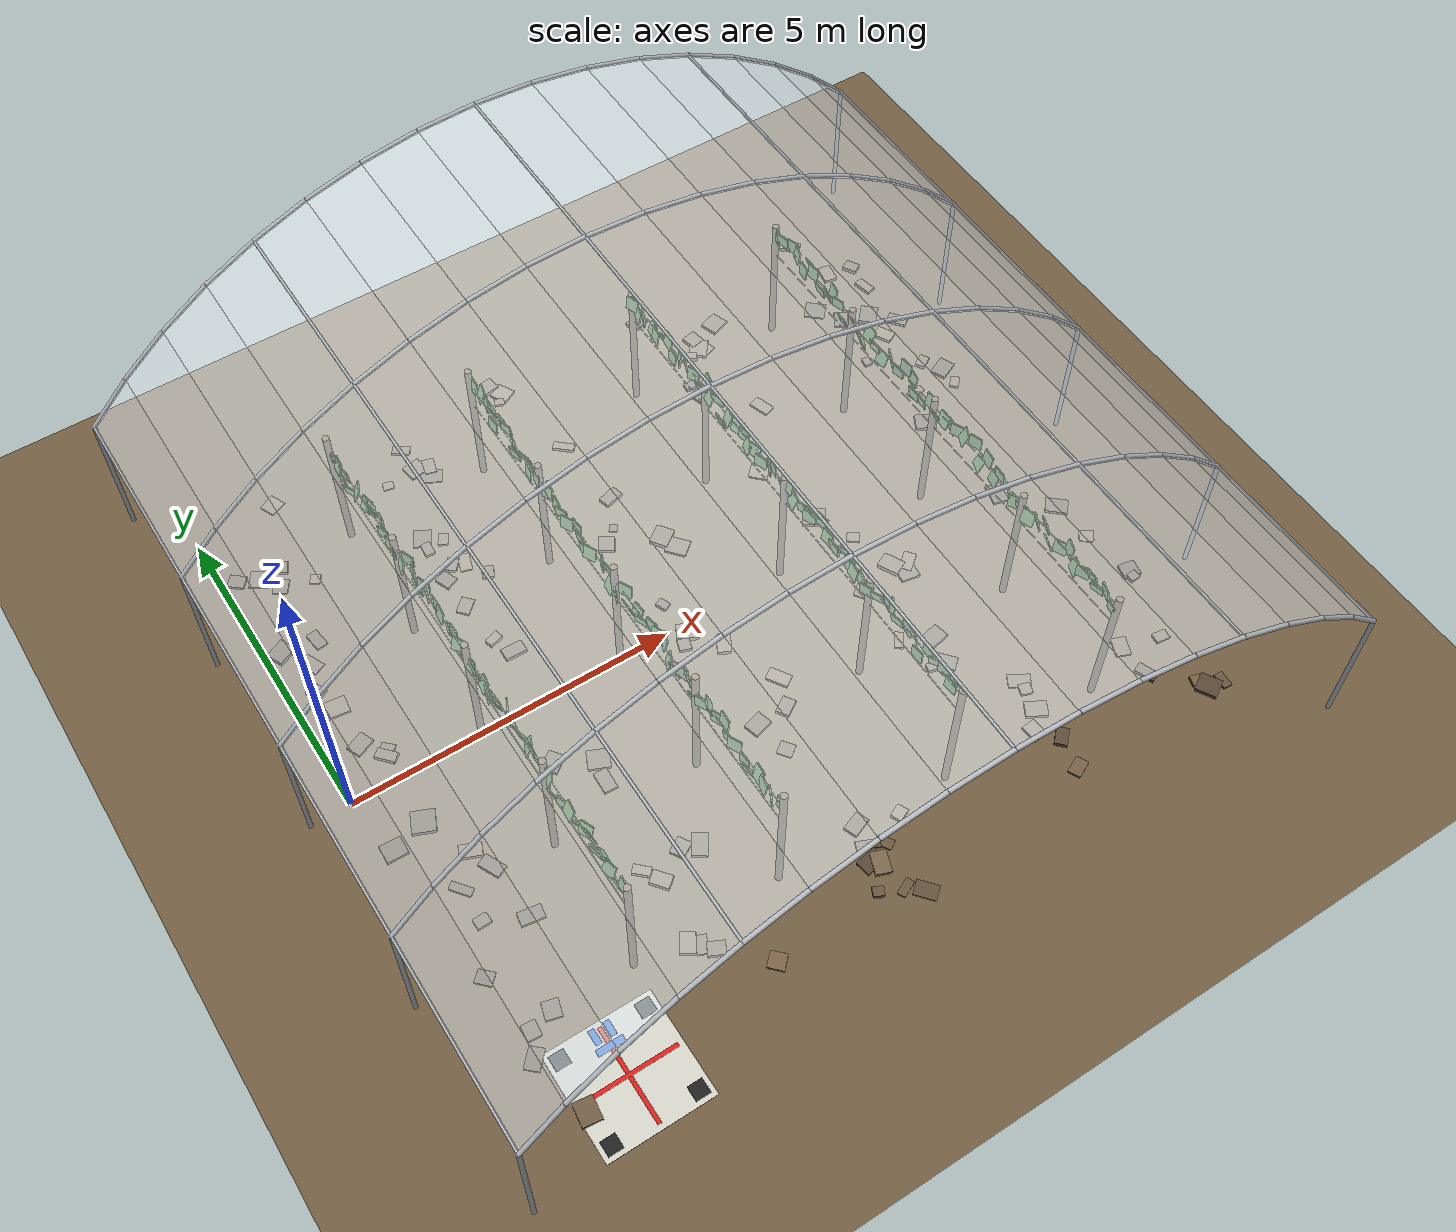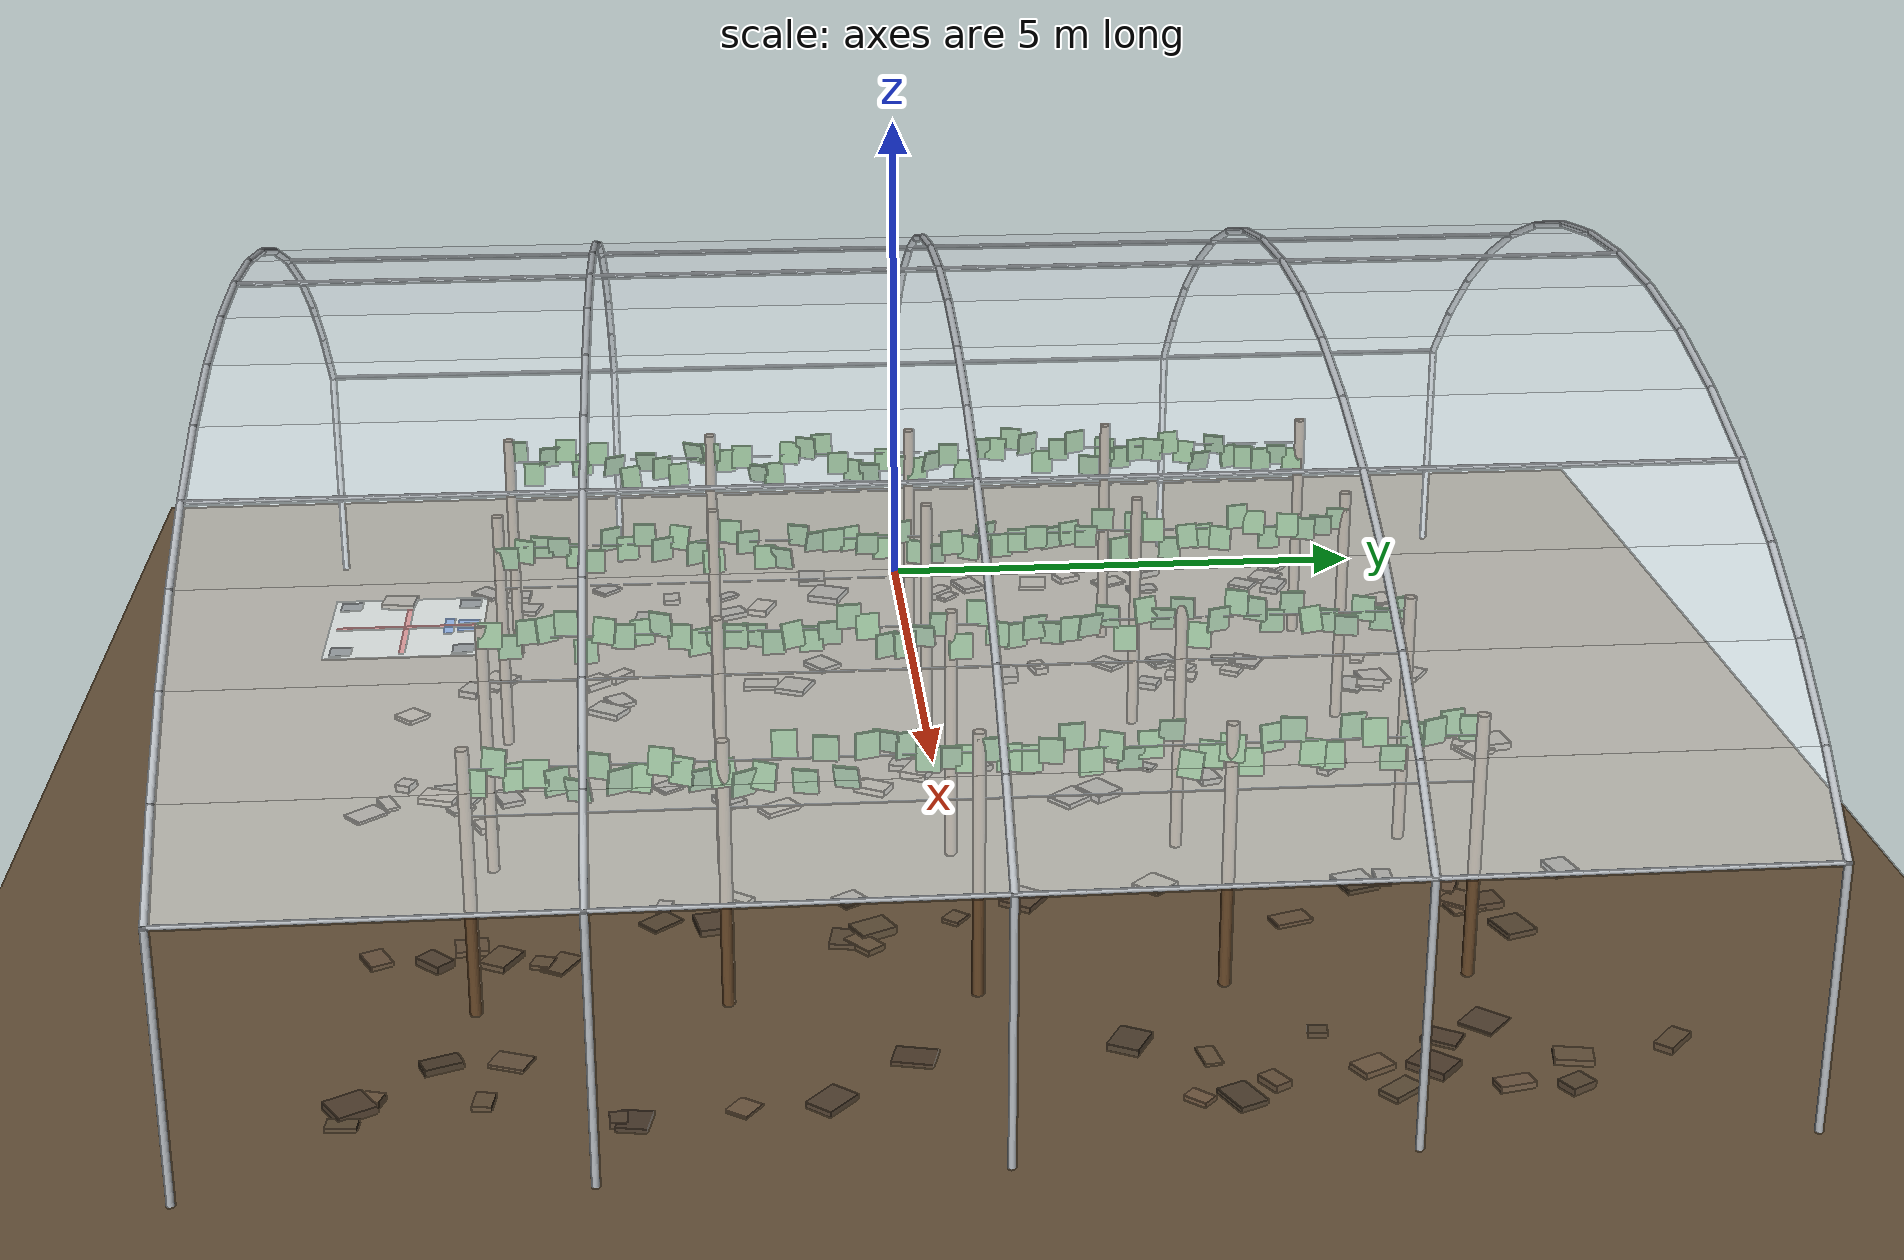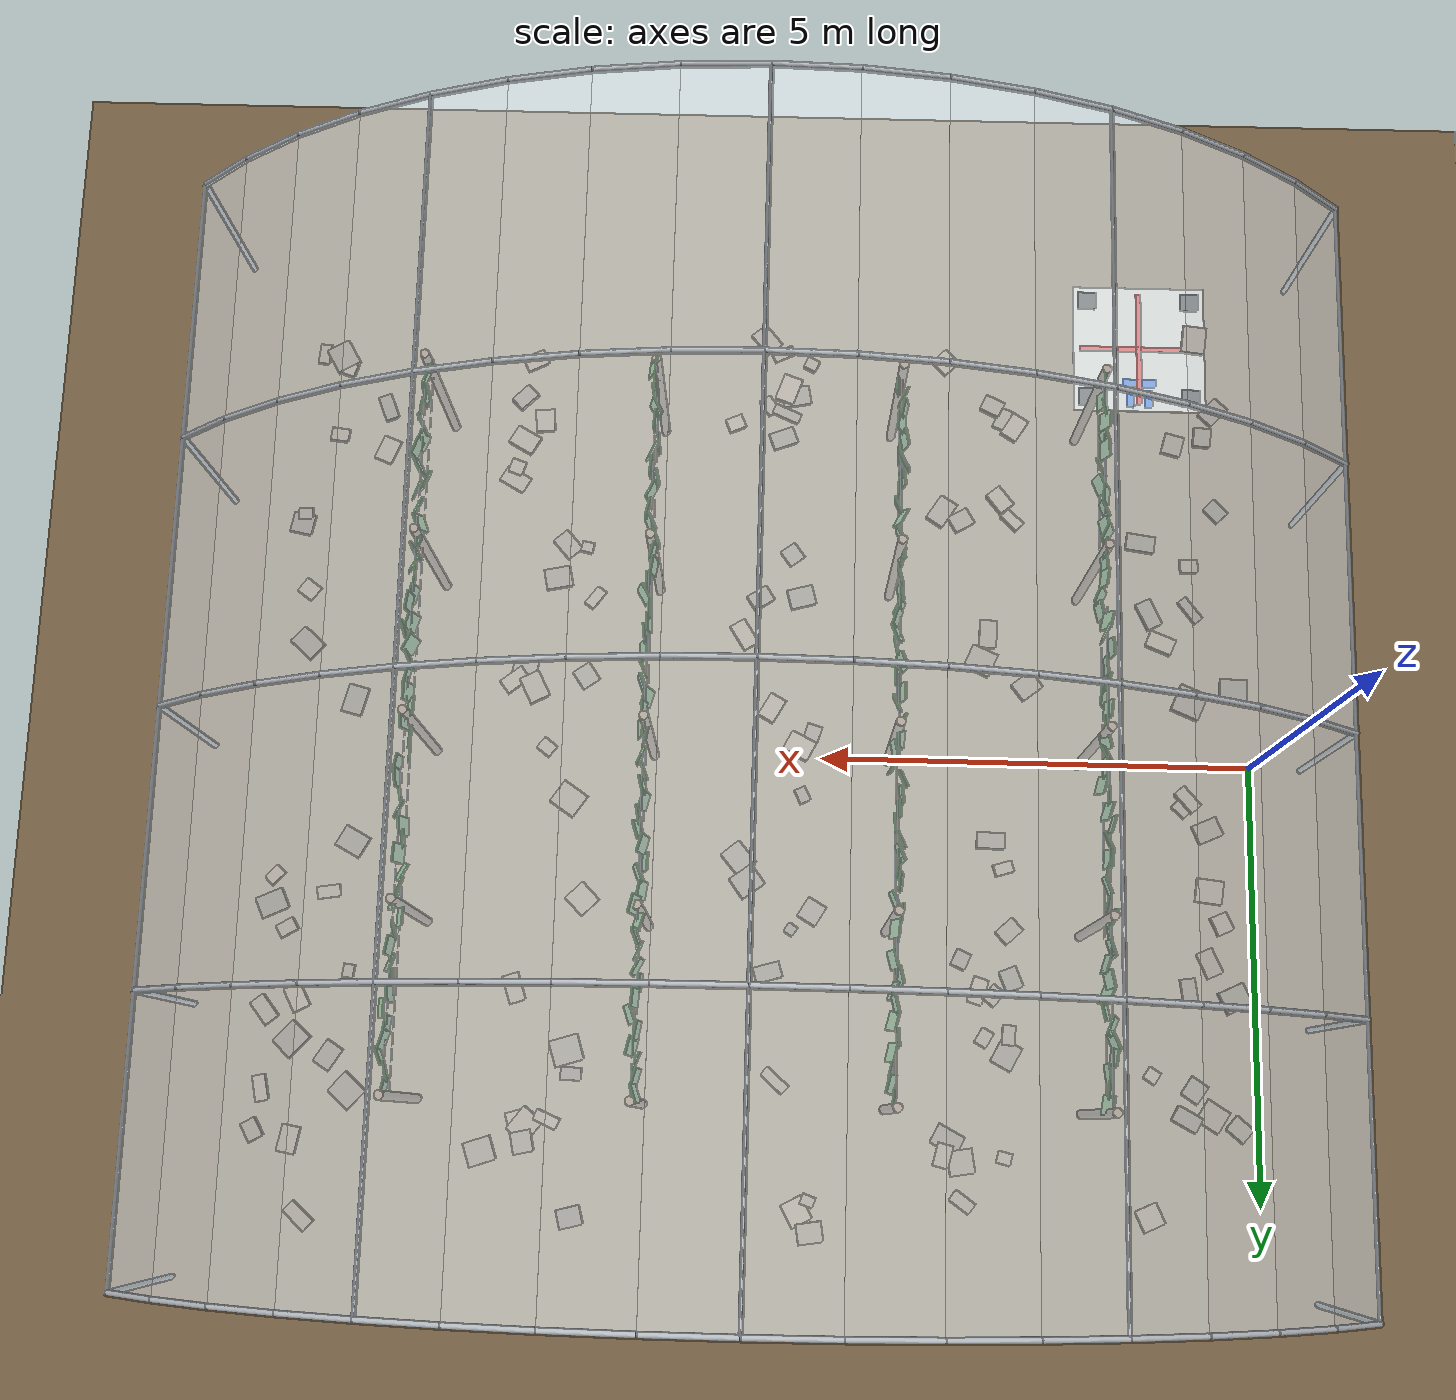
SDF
<?xml version="1.0"?>
<sdf version="1.6">
  <world name="vineyard">

    <include><uri>model://sun</uri></include>

    <model name="ground_plane">
      <static>true</static>
      <link name="link">
        <collision name="collision">
          <geometry><plane><normal>0 0 1</normal><size>120 120</size></plane></geometry>
          <surface><friction><ode><mu>1.1</mu><mu2>1.1</mu2></ode></friction></surface>
        </collision>
        <visual name="visual">
          <geometry><plane><normal>0 0 1</normal><size>120 120</size></plane></geometry>
          <material>
            <ambient>0.22 0.18 0.13 1</ambient>
            <diffuse>0.42 0.34 0.24 1</diffuse>
          </material>
        </visual>
      </link>
    </model>

    <include><uri>model://trellis</uri><pose>0 0 0 0 0 0</pose></include>
    <include><uri>model://dirt_track</uri><pose>0 0 0 0 0 0</pose></include>
    <include><uri>model://polytunnel</uri><pose>0 0 0 0 0 0</pose></include>
    <include><uri>model://start_pad</uri><pose>0 0 0 0 0 0</pose></include>

    <!-- Creates/removes fixed joints between links at runtime. Per cluster the
         demo uses it three times: hang it on the wire, clamp it in the cutter,
         and release it over the crate. -->
    <plugin name="ros_link_attacher_plugin" filename="libgazebo_ros_link_attacher.so"/>

    <model name="harvest_cam">
      <static>true</static>
      <pose>-6.000 0.000 3.400 0.000 0.227 0.000</pose>
      <link name="link">
        <sensor name="cam" type="camera">
          <camera>
            <horizontal_fov>1.15</horizontal_fov>
            <image><width>1280</width><height>720</height><format>R8G8B8</format></image>
            <clip><near>0.05</near><far>120</far></clip>
          </camera>
          <always_on>1</always_on>
          <update_rate>30</update_rate>
          <visualize>false</visualize>
          <plugin name="harvest_cam_plugin" filename="libgazebo_ros_camera.so">
            <cameraName>harvest_cam</cameraName>
            <imageTopicName>image_raw</imageTopicName>
            <cameraInfoTopicName>camera_info</cameraInfoTopicName>
            <frameName>harvest_cam_link</frameName>
            <updateRate>30.0</updateRate>
          </plugin>
        </sensor>
      </link>
    </model>

    <physics type="ode">
      <max_step_size>0.001</max_step_size>
      <real_time_update_rate>1000</real_time_update_rate>
      <ode>
        <solver><type>quick</type><iters>60</iters><sor>1.3</sor></solver>
        <constraints>
          <cfm>0.0</cfm><erp>0.2</erp>
          <contact_max_correcting_vel>100</contact_max_correcting_vel>
          <contact_surface_layer>0.001</contact_surface_layer>
        </constraints>
      </ode>
    </physics>

    <scene>
      <ambient>0.55 0.55 0.55 1</ambient>
      <background>0.62 0.74 0.88 1</background>
      <shadows>true</shadows>
    </scene>

    <gui>
      <camera name="user_camera">
        <pose>-6.000 0.000 3.400 0.000 0.227 0.000</pose>
      </camera>
    </gui>

  </world>
</sdf>

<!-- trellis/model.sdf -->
<sdf version="1.6">
  <model name="trellis">
    <link name="post_r0_0">
      <pose>2.000 -4.000 1.150 0 0 0</pose>
      <inertial><mass>20</mass>
        <inertia><ixx>5</ixx><ixy>0</ixy><ixz>0</ixz><iyy>5</iyy><iyz>0</iyz><izz>0.2</izz></inertia>
      </inertial>
      <visual name="v">
        <geometry><cylinder><radius>0.05</radius><length>2.30</length></cylinder></geometry>
        <material><ambient>0.20 0.13 0.07 1</ambient><diffuse>0.38 0.26 0.14 1</diffuse></material>
      </visual>
      <collision name="c">
        <geometry><cylinder><radius>0.05</radius><length>2.30</length></cylinder></geometry>
      </collision>
    </link>
    <joint name="fix_post_r0_0" type="fixed">
      <parent>world</parent><child>post_r0_0</child>
    </joint>
    <link name="post_r0_1">
      <pose>2.000 -2.000 1.150 0 0 0</pose>
      <inertial><mass>20</mass>
        <inertia><ixx>5</ixx><ixy>0</ixy><ixz>0</ixz><iyy>5</iyy><iyz>0</iyz><izz>0.2</izz></inertia>
      </inertial>
      <visual name="v">
        <geometry><cylinder><radius>0.05</radius><length>2.30</length></cylinder></geometry>
        <material><ambient>0.20 0.13 0.07 1</ambient><diffuse>0.38 0.26 0.14 1</diffuse></material>
      </visual>
      <collision name="c">
        <geometry><cylinder><radius>0.05</radius><length>2.30</length></cylinder></geometry>
      </collision>
    </link>
    <joint name="fix_post_r0_1" type="fixed">
      <parent>world</parent><child>post_r0_1</child>
    </joint>
    <link name="post_r0_2">
      <pose>2.000 0.000 1.150 0 0 0</pose>
      <inertial><mass>20</mass>
        <inertia><ixx>5</ixx><ixy>0</ixy><ixz>0</ixz><iyy>5</iyy><iyz>0</iyz><izz>0.2</izz></inertia>
      </inertial>
      <visual name="v">
        <geometry><cylinder><radius>0.05</radius><length>2.30</length></cylinder></geometry>
        <material><ambient>0.20 0.13 0.07 1</ambient><diffuse>0.38 0.26 0.14 1</diffuse></material>
      </visual>
      <collision name="c">
        <geometry><cylinder><radius>0.05</radius><length>2.30</length></cylinder></geometry>
      </collision>
    </link>
    <joint name="fix_post_r0_2" type="fixed">
      <parent>world</parent><child>post_r0_2</child>
    </joint>
    <link name="post_r0_3">
      <pose>2.000 2.000 1.150 0 0 0</pose>
      <inertial><mass>20</mass>
        <inertia><ixx>5</ixx><ixy>0</ixy><ixz>0</ixz><iyy>5</iyy><iyz>0</iyz><izz>0.2</izz></inertia>
      </inertial>
      <visual name="v">
        <geometry><cylinder><radius>0.05</radius><length>2.30</length></cylinder></geometry>
        <material><ambient>0.20 0.13 0.07 1</ambient><diffuse>0.38 0.26 0.14 1</diffuse></material>
      </visual>
      <collision name="c">
        <geometry><cylinder><radius>0.05</radius><length>2.30</length></cylinder></geometry>
      </collision>
    </link>
    <joint name="fix_post_r0_3" type="fixed">
      <parent>world</parent><child>post_r0_3</child>
    </joint>
    <link name="post_r0_4">
      <pose>2.000 4.000 1.150 0 0 0</pose>
      <inertial><mass>20</mass>
        <inertia><ixx>5</ixx><ixy>0</ixy><ixz>0</ixz><iyy>5</iyy><iyz>0</iyz><izz>0.2</izz></inertia>
      </inertial>
      <visual name="v">
        <geometry><cylinder><radius>0.05</radius><length>2.30</length></cylinder></geometry>
        <material><ambient>0.20 0.13 0.07 1</ambient><diffuse>0.38 0.26 0.14 1</diffuse></material>
      </visual>
      <collision name="c">
        <geometry><cylinder><radius>0.05</radius><length>2.30</length></cylinder></geometry>
      </collision>
    </link>
    <joint name="fix_post_r0_4" type="fixed">
      <parent>world</parent><child>post_r0_4</child>
    </joint>
    <link name="wire_r0_fruit">
      <pose>2.000 0 1.665 1.5708 0 0</pose>
      <inertial><mass>1.0</mass>
        <inertia><ixx>0.2</ixx><ixy>0</ixy><ixz>0</ixz><iyy>0.2</iyy><iyz>0</iyz><izz>0.001</izz></inertia>
      </inertial>
      <visual name="v">
        <geometry><cylinder><radius>0.004</radius><length>8.00</length></cylinder></geometry>
        <material><ambient>0.30 0.30 0.32 1</ambient><diffuse>0.55 0.56 0.58 1</diffuse></material>
      </visual>
      <collision name="c">
        <geometry><cylinder><radius>0.004</radius><length>8.00</length></cylinder></geometry>
      </collision>
    </link>
    <joint name="fix_wire_r0_fruit" type="fixed">
      <parent>world</parent><child>wire_r0_fruit</child>
    </joint>
    <link name="wire_r0_canopy">
      <pose>2.000 0 2.065 1.5708 0 0</pose>
      <inertial><mass>1.0</mass>
        <inertia><ixx>0.2</ixx><ixy>0</ixy><ixz>0</ixz><iyy>0.2</iyy><iyz>0</iyz><izz>0.001</izz></inertia>
      </inertial>
      <visual name="v">
        <geometry><cylinder><radius>0.004</radius><length>8.00</length></cylinder></geometry>
        <material><ambient>0.30 0.30 0.32 1</ambient><diffuse>0.55 0.56 0.58 1</diffuse></material>
      </visual>
      <collision name="c">
        <geometry><cylinder><radius>0.004</radius><length>8.00</length></cylinder></geometry>
      </collision>
    </link>
    <joint name="fix_wire_r0_canopy" type="fixed">
      <parent>world</parent><child>wire_r0_canopy</child>
    </joint>
    <link name="post_r1_0">
      <pose>4.226 -4.000 1.150 0 0 0</pose>
      <inertial><mass>20</mass>
        <inertia><ixx>5</ixx><ixy>0</ixy><ixz>0</ixz><iyy>5</iyy><iyz>0</iyz><izz>0.2</izz></inertia>
      </inertial>
      <visual name="v">
        <geometry><cylinder><radius>0.05</radius><length>2.30</length></cylinder></geometry>
        <material><ambient>0.20 0.13 0.07 1</ambient><diffuse>0.38 0.26 0.14 1</diffuse></material>
      </visual>
      <collision name="c">
        <geometry><cylinder><radius>0.05</radius><length>2.30</length></cylinder></geometry>
      </collision>
    </link>
    <joint name="fix_post_r1_0" type="fixed">
      <parent>world</parent><child>post_r1_0</child>
    </joint>
    <link name="post_r1_1">
      <pose>4.226 -2.000 1.150 0 0 0</pose>
      <inertial><mass>20</mass>
        <inertia><ixx>5</ixx><ixy>0</ixy><ixz>0</ixz><iyy>5</iyy><iyz>0</iyz><izz>0.2</izz></inertia>
      </inertial>
      <visual name="v">
        <geometry><cylinder><radius>0.05</radius><length>2.30</length></cylinder></geometry>
        <material><ambient>0.20 0.13 0.07 1</ambient><diffuse>0.38 0.26 0.14 1</diffuse></material>
      </visual>
      <collision name="c">
        <geometry><cylinder><radius>0.05</radius><length>2.30</length></cylinder></geometry>
      </collision>
    </link>
    <joint name="fix_post_r1_1" type="fixed">
      <parent>world</parent><child>post_r1_1</child>
    </joint>
    <link name="post_r1_2">
      <pose>4.226 0.000 1.150 0 0 0</pose>
      <inertial><mass>20</mass>
        <inertia><ixx>5</ixx><ixy>0</ixy><ixz>0</ixz><iyy>5</iyy><iyz>0</iyz><izz>0.2</izz></inertia>
      </inertial>
      <visual name="v">
        <geometry><cylinder><radius>0.05</radius><length>2.30</length></cylinder></geometry>
        <material><ambient>0.20 0.13 0.07 1</ambient><diffuse>0.38 0.26 0.14 1</diffuse></material>
      </visual>
      <collision name="c">
        <geometry><cylinder><radius>0.05</radius><length>2.30</length></cylinder></geometry>
      </collision>
    </link>
    <joint name="fix_post_r1_2" type="fixed">
      <parent>world</parent><child>post_r1_2</child>
    </joint>
    <link name="post_r1_3">
      <pose>4.226 2.000 1.150 0 0 0</pose>
      <inertial><mass>20</mass>
        <inertia><ixx>5</ixx><ixy>0</ixy><ixz>0</ixz><iyy>5</iyy><iyz>0</iyz><izz>0.2</izz></inertia>
      </inertial>
      <visual name="v">
        <geometry><cylinder><radius>0.05</radius><length>2.30</length></cylinder></geometry>
        <material><ambient>0.20 0.13 0.07 1</ambient><diffuse>0.38 0.26 0.14 1</diffuse></material>
      </visual>
      <collision name="c">
        <geometry><cylinder><radius>0.05</radius><length>2.30</length></cylinder></geometry>
      </collision>
    </link>
    <joint name="fix_post_r1_3" type="fixed">
      <parent>world</parent><child>post_r1_3</child>
    </joint>
    <link name="post_r1_4">
      <pose>4.226 4.000 1.150 0 0 0</pose>
      <inertial><mass>20</mass>
        <inertia><ixx>5</ixx><ixy>0</ixy><ixz>0</ixz><iyy>5</iyy><iyz>0</iyz><izz>0.2</izz></inertia>
      </inertial>
      <visual name="v">
        <geometry><cylinder><radius>0.05</radius><length>2.30</length></cylinder></geometry>
        <material><ambient>0.20 0.13 0.07 1</ambient><diffuse>0.38 0.26 0.14 1</diffuse></material>
      </visual>
      <collision name="c">
        <geometry><cylinder><radius>0.05</radius><length>2.30</length></cylinder></geometry>
      </collision>
    </link>
    <joint name="fix_post_r1_4" type="fixed">
      <parent>world</parent><child>post_r1_4</child>
    </joint>
    <link name="wire_r1_fruit">
      <pose>4.226 0 1.582 1.5708 0 0</pose>
      <inertial><mass>1.0</mass>
        <inertia><ixx>0.2</ixx><ixy>0</ixy><ixz>0</ixz><iyy>0.2</iyy><iyz>0</iyz><izz>0.001</izz></inertia>
      </inertial>
      <visual name="v">
        <geometry><cylinder><radius>0.004</radius><length>8.00</length></cylinder></geometry>
        <material><ambient>0.30 0.30 0.32 1</ambient><diffuse>0.55 0.56 0.58 1</diffuse></material>
      </visual>
      <collision name="c">
        <geometry><cylinder><radius>0.004</radius><length>8.00</length></cylinder></geometry>
      </collision>
    </link>
    <joint name="fix_wire_r1_fruit" type="fixed">
      <parent>world</parent><child>wire_r1_fruit</child>
    </joint>
    <link name="wire_r1_canopy">
      <pose>4.226 0 1.982 1.5708 0 0</pose>
      <inertial><mass>1.0</mass>
        <inertia><ixx>0.2</ixx><ixy>0</ixy><ixz>0</ixz><iyy>0.2</iyy><iyz>0</iyz><izz>0.001</izz></inertia>
      </inertial>
      <visual name="v">
        <geometry><cylinder><radius>0.004</radius><length>8.00</length></cylinder></geometry>
        <material><ambient>0.30 0.30 0.32 1</ambient><diffuse>0.55 0.56 0.58 1</diffuse></material>
      </visual>
      <collision name="c">
        <geometry><cylinder><radius>0.004</radius><length>8.00</length></cylinder></geometry>
      </collision>
    </link>
    <joint name="fix_wire_r1_canopy" type="fixed">
      <parent>world</parent><child>wire_r1_canopy</child>
    </joint>
    <link name="post_r2_0">
      <pose>6.945 -4.000 1.150 0 0 0</pose>
      <inertial><mass>20</mass>
        <inertia><ixx>5</ixx><ixy>0</ixy><ixz>0</ixz><iyy>5</iyy><iyz>0</iyz><izz>0.2</izz></inertia>
      </inertial>
      <visual name="v">
        <geometry><cylinder><radius>0.05</radius><length>2.30</length></cylinder></geometry>
        <material><ambient>0.20 0.13 0.07 1</ambient><diffuse>0.38 0.26 0.14 1</diffuse></material>
      </visual>
      <collision name="c">
        <geometry><cylinder><radius>0.05</radius><length>2.30</length></cylinder></geometry>
      </collision>
    </link>
    <joint name="fix_post_r2_0" type="fixed">
      <parent>world</parent><child>post_r2_0</child>
    </joint>
    <link name="post_r2_1">
      <pose>6.945 -2.000 1.150 0 0 0</pose>
      <inertial><mass>20</mass>
        <inertia><ixx>5</ixx><ixy>0</ixy><ixz>0</ixz><iyy>5</iyy><iyz>0</iyz><izz>0.2</izz></inertia>
      </inertial>
      <visual name="v">
        <geometry><cylinder><radius>0.05</radius><length>2.30</length></cylinder></geometry>
        <material><ambient>0.20 0.13 0.07 1</ambient><diffuse>0.38 0.26 0.14 1</diffuse></material>
      </visual>
      <collision name="c">
        <geometry><cylinder><radius>0.05</radius><length>2.30</length></cylinder></geometry>
      </collision>
    </link>
    <joint name="fix_post_r2_1" type="fixed">
      <parent>world</parent><child>post_r2_1</child>
    </joint>
    <link name="post_r2_2">
      <pose>6.945 0.000 1.150 0 0 0</pose>
      <inertial><mass>20</mass>
        <inertia><ixx>5</ixx><ixy>0</ixy><ixz>0</ixz><iyy>5</iyy><iyz>0</iyz><izz>0.2</izz></inertia>
      </inertial>
      <visual name="v">
        <geometry><cylinder><radius>0.05</radius><length>2.30</length></cylinder></geometry>
        <material><ambient>0.20 0.13 0.07 1</ambient><diffuse>0.38 0.26 0.14 1</diffuse></material>
      </visual>
      <collision name="c">
        <geometry><cylinder><radius>0.05</radius><length>2.30</length></cylinder></geometry>
      </collision>
    </link>
    <joint name="fix_post_r2_2" type="fixed">
      <parent>world</parent><child>post_r2_2</child>
    </joint>
    <link name="post_r2_3">
      <pose>6.945 2.000 1.150 0 0 0</pose>
      <inertial><mass>20</mass>
        <inertia><ixx>5</ixx><ixy>0</ixy><ixz>0</ixz><iyy>5</iyy><iyz>0</iyz><izz>0.2</izz></inertia>
      </inertial>
      <visual name="v">
        <geometry><cylinder><radius>0.05</radius><length>2.30</length></cylinder></geometry>
        <material><ambient>0.20 0.13 0.07 1</ambient><diffuse>0.38 0.26 0.14 1</diffuse></material>
      </visual>
      <collision name="c">
        <geometry><cylinder><radius>0.05</radius><length>2.30</length></cylinder></geometry>
      </collision>
    </link>
    <joint name="fix_post_r2_3" type="fixed">
      <parent>world</parent><child>post_r2_3</child>
    </joint>
    <link name="post_r2_4">
      <pose>6.945 4.000 1.150 0 0 0</pose>
      <inertial><mass>20</mass>
        <inertia><ixx>5</ixx><ixy>0</ixy><ixz>0</ixz><iyy>5</iyy><iyz>0</iyz><izz>0.2</izz></inertia>
      </inertial>
      <visual name="v">
        <geometry><cylinder><radius>0.05</radius><length>2.30</length></cylinder></geometry>
        <material><ambient>0.20 0.13 0.07 1</ambient><diffuse>0.38 0.26 0.14 1</diffuse></material>
      </visual>
      <collision name="c">
        <geometry><cylinder><radius>0.05</radius><length>2.30</length></cylinder></geometry>
      </collision>
    </link>
    <joint name="fix_post_r2_4" type="fixed">
      <parent>world</parent><child>post_r2_4</child>
    </joint>
    <link name="wire_r2_fruit">
      <pose>6.945 0 1.773 1.5708 0 0</pose>
      <inertial><mass>1.0</mass>
        <inertia><ixx>0.2</ixx><ixy>0</ixy><ixz>0</ixz><iyy>0.2</iyy><iyz>0</iyz><izz>0.001</izz></inertia>
      </inertial>
      <visual name="v">
        <geometry><cylinder><radius>0.004</radius><length>8.00</length></cylinder></geometry>
        <material><ambient>0.30 0.30 0.32 1</ambient><diffuse>0.55 0.56 0.58 1</diffuse></material>
      </visual>
      <collision name="c">
        <geometry><cylinder><radius>0.004</radius><length>8.00</length></cylinder></geometry>
      </collision>
    </link>
    <joint name="fix_wire_r2_fruit" type="fixed">
      <parent>world</parent><child>wire_r2_fruit</child>
    </joint>
    <link name="wire_r2_canopy">
      <pose>6.945 0 2.173 1.5708 0 0</pose>
      <inertial><mass>1.0</mass>
        <inertia><ixx>0.2</ixx><ixy>0</ixy><ixz>0</ixz><iyy>0.2</iyy><iyz>0</iyz><izz>0.001</izz></inertia>
      </inertial>
      <visual name="v">
        <geometry><cylinder><radius>0.004</radius><length>8.00</length></cylinder></geometry>
        <material><ambient>0.30 0.30 0.32 1</ambient><diffuse>0.55 0.56 0.58 1</diffuse></material>
      </visual>
      <collision name="c">
        <geometry><cylinder><radius>0.004</radius><length>8.00</length></cylinder></geometry>
      </collision>
    </link>
    <joint name="fix_wire_r2_canopy" type="fixed">
      <parent>world</parent><child>wire_r2_canopy</child>
    </joint>
    <link name="post_r3_0">
      <pose>9.493 -4.000 1.150 0 0 0</pose>
      <inertial><mass>20</mass>
        <inertia><ixx>5</ixx><ixy>0</ixy><ixz>0</ixz><iyy>5</iyy><iyz>0</iyz><izz>0.2</izz></inertia>
      </inertial>
      <visual name="v">
        <geometry><cylinder><radius>0.05</radius><length>2.30</length></cylinder></geometry>
        <material><ambient>0.20 0.13 0.07 1</ambient><diffuse>0.38 0.26 0.14 1</diffuse></material>
      </visual>
      <collision name="c">
        <geometry><cylinder><radius>0.05</radius><length>2.30</length></cylinder></geometry>
      </collision>
    </link>
    <joint name="fix_post_r3_0" type="fixed">
      <parent>world</parent><child>post_r3_0</child>
    </joint>
    <link name="post_r3_1">
      <pose>9.493 -2.000 1.150 0 0 0</pose>
      <inertial><mass>20</mass>
        <inertia><ixx>5</ixx><ixy>0</ixy><ixz>0</ixz><iyy>5</iyy><iyz>0</iyz><izz>0.2</izz></inertia>
      </inertial>
      <visual name="v">
        <geometry><cylinder><radius>0.05</radius><length>2.30</length></cylinder></geometry>
        <material><ambient>0.20 0.13 0.07 1</ambient><diffuse>0.38 0.26 0.14 1</diffuse></material>
      </visual>
      <collision name="c">
        <geometry><cylinder><radius>0.05</radius><length>2.30</length></cylinder></geometry>
      </collision>
    </link>
    <joint name="fix_post_r3_1" type="fixed">
      <parent>world</parent><child>post_r3_1</child>
    </joint>
    <link name="post_r3_2">
      <pose>9.493 0.000 1.150 0 0 0</pose>
      <inertial><mass>20</mass>
        <inertia><ixx>5</ixx><ixy>0</ixy><ixz>0</ixz><iyy>5</iyy><iyz>0</iyz><izz>0.2</izz></inertia>
      </inertial>
      <visual name="v">
        <geometry><cylinder><radius>0.05</radius><length>2.30</length></cylinder></geometry>
        <material><ambient>0.20 0.13 0.07 1</ambient><diffuse>0.38 0.26 0.14 1</diffuse></material>
      </visual>
      <collision name="c">
        <geometry><cylinder><radius>0.05</radius><length>2.30</length></cylinder></geometry>
      </collision>
    </link>
    <joint name="fix_post_r3_2" type="fixed">
      <parent>world</parent><child>post_r3_2</child>
    </joint>
    <link name="post_r3_3">
      <pose>9.493 2.000 1.150 0 0 0</pose>
      <inertial><mass>20</mass>
        <inertia><ixx>5</ixx><ixy>0</ixy><ixz>0</ixz><iyy>5</iyy><iyz>0</iyz><izz>0.2</izz></inertia>
      </inertial>
      <visual name="v">
        <geometry><cylinder><radius>0.05</radius><length>2.30</length></cylinder></geometry>
        <material><ambient>0.20 0.13 0.07 1</ambient><diffuse>0.38 0.26 0.14 1</diffuse></material>
      </visual>
      <collision name="c">
        <geometry><cylinder><radius>0.05</radius><length>2.30</length></cylinder></geometry>
      </collision>
    </link>
    <joint name="fix_post_r3_3" type="fixed">
      <parent>world</parent><child>post_r3_3</child>
    </joint>
    <link name="post_r3_4">
      <pose>9.493 4.000 1.150 0 0 0</pose>
      <inertial><mass>20</mass>
        <inertia><ixx>5</ixx><ixy>0</ixy><ixz>0</ixz><iyy>5</iyy><iyz>0</iyz><izz>0.2</izz></inertia>
      </inertial>
      <visual name="v">
        <geometry><cylinder><radius>0.05</radius><length>2.30</length></cylinder></geometry>
        <material><ambient>0.20 0.13 0.07 1</ambient><diffuse>0.38 0.26 0.14 1</diffuse></material>
      </visual>
      <collision name="c">
        <geometry><cylinder><radius>0.05</radius><length>2.30</length></cylinder></geometry>
      </collision>
    </link>
    <joint name="fix_post_r3_4" type="fixed">
      <parent>world</parent><child>post_r3_4</child>
    </joint>
    <link name="wire_r3_fruit">
      <pose>9.493 0 1.726 1.5708 0 0</pose>
      <inertial><mass>1.0</mass>
        <inertia><ixx>0.2</ixx><ixy>0</ixy><ixz>0</ixz><iyy>0.2</iyy><iyz>0</iyz><izz>0.001</izz></inertia>
      </inertial>
      <visual name="v">
        <geometry><cylinder><radius>0.004</radius><length>8.00</length></cylinder></geometry>
        <material><ambient>0.30 0.30 0.32 1</ambient><diffuse>0.55 0.56 0.58 1</diffuse></material>
      </visual>
      <collision name="c">
        <geometry><cylinder><radius>0.004</radius><length>8.00</length></cylinder></geometry>
      </collision>
    </link>
    <joint name="fix_wire_r3_fruit" type="fixed">
      <parent>world</parent><child>wire_r3_fruit</child>
    </joint>
    <link name="wire_r3_canopy">
      <pose>9.493 0 2.126 1.5708 0 0</pose>
      <inertial><mass>1.0</mass>
        <inertia><ixx>0.2</ixx><ixy>0</ixy><ixz>0</ixz><iyy>0.2</iyy><iyz>0</iyz><izz>0.001</izz></inertia>
      </inertial>
      <visual name="v">
        <geometry><cylinder><radius>0.004</radius><length>8.00</length></cylinder></geometry>
        <material><ambient>0.30 0.30 0.32 1</ambient><diffuse>0.55 0.56 0.58 1</diffuse></material>
      </visual>
      <collision name="c">
        <geometry><cylinder><radius>0.004</radius><length>8.00</length></cylinder></geometry>
      </collision>
    </link>
    <joint name="fix_wire_r3_canopy" type="fixed">
      <parent>world</parent><child>wire_r3_canopy</child>
    </joint>
    <link name="canopy">
      <pose>0 0 0 0 0 0</pose>
      <inertial><mass>2.0</mass>
        <inertia><ixx>1</ixx><ixy>0</ixy><ixz>0</ixz><iyy>1</iyy><iyz>0</iyz><izz>1</izz></inertia>
      </inertial>
      <visual name="leaf_r0_0">
        <pose>1.998 -3.920 2.174 0 0.18 -0.03</pose>
        <geometry><box><size>0.02 0.20 0.22</size></box></geometry>
        <material><ambient>0.08 0.20 0.05 1</ambient><diffuse>0.16 0.42 0.10 1</diffuse></material>
      </visual>
      <visual name="leaf_r0_1">
        <pose>2.002 -3.760 1.936 0 -0.27 -0.05</pose>
        <geometry><box><size>0.02 0.20 0.22</size></box></geometry>
        <material><ambient>0.08 0.20 0.05 1</ambient><diffuse>0.16 0.42 0.10 1</diffuse></material>
      </visual>
      <visual name="leaf_r0_2">
        <pose>1.986 -3.600 2.111 0 0.32 0.22</pose>
        <geometry><box><size>0.02 0.20 0.22</size></box></geometry>
        <material><ambient>0.08 0.20 0.05 1</ambient><diffuse>0.16 0.42 0.10 1</diffuse></material>
      </visual>
      <visual name="leaf_r0_3">
        <pose>2.008 -3.440 2.178 0 -0.38 -0.07</pose>
        <geometry><box><size>0.02 0.20 0.22</size></box></geometry>
        <material><ambient>0.08 0.20 0.05 1</ambient><diffuse>0.16 0.42 0.10 1</diffuse></material>
      </visual>
      <visual name="leaf_r0_4">
        <pose>1.986 -3.280 2.018 0 -0.16 0.25</pose>
        <geometry><box><size>0.02 0.20 0.22</size></box></geometry>
        <material><ambient>0.08 0.20 0.05 1</ambient><diffuse>0.16 0.42 0.10 1</diffuse></material>
      </visual>
      <visual name="leaf_r0_5">
        <pose>2.007 -3.120 2.137 0 -0.30 0.05</pose>
        <geometry><box><size>0.02 0.20 0.22</size></box></geometry>
        <material><ambient>0.08 0.20 0.05 1</ambient><diffuse>0.16 0.42 0.10 1</diffuse></material>
      </visual>
      <visual name="leaf_r0_6">
        <pose>2.036 -2.960 2.017 0 0.32 0.41</pose>
        <geometry><box><size>0.02 0.20 0.22</size></box></geometry>
        <material><ambient>0.08 0.20 0.05 1</ambient><diffuse>0.16 0.42 0.10 1</diffuse></material>
      </visual>
      <visual name="leaf_r0_7">
        <pose>2.026 -2.800 1.880 0 -0.28 0.41</pose>
        <geometry><box><size>0.02 0.20 0.22</size></box></geometry>
        <material><ambient>0.08 0.20 0.05 1</ambient><diffuse>0.16 0.42 0.10 1</diffuse></material>
      </visual>
      <visual name="leaf_r0_8">
        <pose>1.985 -2.640 2.031 0 0.38 -0.09</pose>
        <geometry><box><size>0.02 0.20 0.22</size></box></geometry>
        <material><ambient>0.08 0.20 0.05 1</ambient><diffuse>0.16 0.42 0.10 1</diffuse></material>
      </visual>
      <visual name="leaf_r0_9">
        <pose>1.993 -2.480 1.965 0 -0.01 0.37</pose>
        <geometry><box><size>0.02 0.20 0.22</size></box></geometry>
        <material><ambient>0.08 0.20 0.05 1</ambient><diffuse>0.16 0.42 0.10 1</diffuse></material>
      </visual>
      <visual name="leaf_r0_10">
        <pose>1.976 -2.320 1.885 0 -0.27 0.23</pose>
        <geometry><box><size>0.02 0.20 0.22</size></box></geometry>
        <material><ambient>0.08 0.20 0.05 1</ambient><diffuse>0.16 0.42 0.10 1</diffuse></material>
      </visual>
      <visual name="leaf_r0_11">
        <pose>1.993 -2.160 2.119 0 0.34 -0.48</pose>
        <geometry><box><size>0.02 0.20 0.22</size></box></geometry>
        <material><ambient>0.08 0.20 0.05 1</ambient><diffuse>0.16 0.42 0.10 1</diffuse></material>
      </visual>
      <visual name="leaf_r0_12">
        <pose>2.012 -2.000 2.104 0 0.01 -0.10</pose>
        <geometry><box><size>0.02 0.20 0.22</size></box></geometry>
        <material><ambient>0.08 0.20 0.05 1</ambient><diffuse>0.16 0.42 0.10 1</diffuse></material>
      </visual>
      <visual name="leaf_r0_13">
        <pose>2.012 -1.840 2.031 0 -0.12 0.08</pose>
        <geometry><box><size>0.02 0.20 0.22</size></box></geometry>
        <material><ambient>0.08 0.20 0.05 1</ambient><diffuse>0.16 0.42 0.10 1</diffuse></material>
      </visual>
      <visual name="leaf_r0_14">
        <pose>2.020 -1.680 2.071 0 -0.22 -0.14</pose>
        <geometry><box><size>0.02 0.20 0.22</size></box></geometry>
        <material><ambient>0.08 0.20 0.05 1</ambient><diffuse>0.16 0.42 0.10 1</diffuse></material>
      </visual>
      <visual name="leaf_r0_15">
        <pose>2.041 -1.520 1.899 0 0.40 -0.41</pose>
        <geometry><box><size>0.02 0.20 0.22</size></box></geometry>
        <material><ambient>0.08 0.20 0.05 1</ambient><diffuse>0.16 0.42 0.10 1</diffuse></material>
      </visual>
      <visual name="leaf_r0_16">
        <pose>2.048 -1.360 1.891 0 -0.18 0.22</pose>
        <geometry><box><size>0.02 0.20 0.22</size></box></geometry>
        <material><ambient>0.08 0.20 0.05 1</ambient><diffuse>0.16 0.42 0.10 1</diffuse></material>
      </visual>
      <visual name="leaf_r0_17">
        <pose>1.998 -1.200 2.089 0 -0.35 -0.23</pose>
        <geometry><box><size>0.02 0.20 0.22</size></box></geometry>
        <material><ambient>0.08 0.20 0.05 1</ambient><diffuse>0.16 0.42 0.10 1</diffuse></material>
      </visual>
      <visual name="leaf_r0_18">
        <pose>2.030 -1.040 2.149 0 0.08 -0.46</pose>
        <geometry><box><size>0.02 0.20 0.22</size></box></geometry>
        <material><ambient>0.08 0.20 0.05 1</ambient><diffuse>0.16 0.42 0.10 1</diffuse></material>
      </visual>
      <visual name="leaf_r0_19">
        <pose>1.970 -0.880 2.158 0 -0.10 0.07</pose>
        <geometry><box><size>0.02 0.20 0.22</size></box></geometry>
        <material><ambient>0.08 0.20 0.05 1</ambient><diffuse>0.16 0.42 0.10 1</diffuse></material>
      </visual>
      <visual name="leaf_r0_20">
        <pose>1.998 -0.720 1.970 0 -0.00 0.06</pose>
        <geometry><box><size>0.02 0.20 0.22</size></box></geometry>
        <material><ambient>0.08 0.20 0.05 1</ambient><diffuse>0.16 0.42 0.10 1</diffuse></material>
      </visual>
      <visual name="leaf_r0_21">
        <pose>1.972 -0.560 1.882 0 -0.00 -0.31</pose>
        <geometry><box><size>0.02 0.20 0.22</size></box></geometry>
        <material><ambient>0.08 0.20 0.05 1</ambient><diffuse>0.16 0.42 0.10 1</diffuse></material>
      </visual>
      <visual name="leaf_r0_22">
        <pose>2.015 -0.400 1.869 0 0.37 -0.15</pose>
        <geometry><box><size>0.02 0.20 0.22</size></box></geometry>
        <material><ambient>0.08 0.20 0.05 1</ambient><diffuse>0.16 0.42 0.10 1</diffuse></material>
      </visual>
      <visual name="leaf_r0_23">
        <pose>1.985 -0.240 1.986 0 -0.25 -0.11</pose>
        <geometry><box><size>0.02 0.20 0.22</size></box></geometry>
        <material><ambient>0.08 0.20 0.05 1</ambient><diffuse>0.16 0.42 0.10 1</diffuse></material>
      </visual>
      <visual name="leaf_r0_24">
        <pose>1.995 -0.080 1.925 0 0.28 0.08</pose>
        <geometry><box><size>0.02 0.20 0.22</size></box></geometry>
        <material><ambient>0.08 0.20 0.05 1</ambient><diffuse>0.16 0.42 0.10 1</diffuse></material>
      </visual>
      <visual name="leaf_r0_25">
        <pose>2.001 0.080 1.888 0 -0.30 0.23</pose>
        <geometry><box><size>0.02 0.20 0.22</size></box></geometry>
        <material><ambient>0.08 0.20 0.05 1</ambient><diffuse>0.16 0.42 0.10 1</diffuse></material>
      </visual>
      <visual name="leaf_r0_26">
        <pose>2.002 0.240 1.967 0 0.35 0.46</pose>
        <geometry><box><size>0.02 0.20 0.22</size></box></geometry>
        <material><ambient>0.08 0.20 0.05 1</ambient><diffuse>0.16 0.42 0.10 1</diffuse></material>
      </visual>
      <visual name="leaf_r0_27">
        <pose>2.033 0.400 2.040 0 0.01 -0.01</pose>
        <geometry><box><size>0.02 0.20 0.22</size></box></geometry>
        <material><ambient>0.08 0.20 0.05 1</ambient><diffuse>0.16 0.42 0.10 1</diffuse></material>
      </visual>
      <visual name="leaf_r0_28">
        <pose>2.045 0.560 1.865 0 -0.30 -0.26</pose>
        <geometry><box><size>0.02 0.20 0.22</size></box></geometry>
        <material><ambient>0.08 0.20 0.05 1</ambient><diffuse>0.16 0.42 0.10 1</diffuse></material>
      </visual>
      <visual name="leaf_r0_29">
        <pose>2.005 0.720 2.080 0 0.20 -0.09</pose>
        <geometry><box><size>0.02 0.20 0.22</size></box></geometry>
        <material><ambient>0.08 0.20 0.05 1</ambient><diffuse>0.16 0.42 0.10 1</diffuse></material>
      </visual>
      <visual name="leaf_r0_30">
        <pose>2.023 0.880 2.084 0 -0.24 -0.31</pose>
        <geometry><box><size>0.02 0.20 0.22</size></box></geometry>
        <material><ambient>0.08 0.20 0.05 1</ambient><diffuse>0.16 0.42 0.10 1</diffuse></material>
      </visual>
      <visual name="leaf_r0_31">
        <pose>1.991 1.040 2.175 0 -0.01 -0.29</pose>
        <geometry><box><size>0.02 0.20 0.22</size></box></geometry>
        <material><ambient>0.08 0.20 0.05 1</ambient><diffuse>0.16 0.42 0.10 1</diffuse></material>
      </visual>
      <visual name="leaf_r0_32">
        <pose>2.024 1.200 2.131 0 0.12 0.41</pose>
        <geometry><box><size>0.02 0.20 0.22</size></box></geometry>
        <material><ambient>0.08 0.20 0.05 1</ambient><diffuse>0.16 0.42 0.10 1</diffuse></material>
      </visual>
      <visual name="leaf_r0_33">
        <pose>1.990 1.360 1.920 0 -0.25 -0.08</pose>
        <geometry><box><size>0.02 0.20 0.22</size></box></geometry>
        <material><ambient>0.08 0.20 0.05 1</ambient><diffuse>0.16 0.42 0.10 1</diffuse></material>
      </visual>
      <visual name="leaf_r0_34">
        <pose>2.022 1.520 2.061 0 0.10 -0.23</pose>
        <geometry><box><size>0.02 0.20 0.22</size></box></geometry>
        <material><ambient>0.08 0.20 0.05 1</ambient><diffuse>0.16 0.42 0.10 1</diffuse></material>
      </visual>
      <visual name="leaf_r0_35">
        <pose>2.046 1.680 2.145 0 0.01 0.36</pose>
        <geometry><box><size>0.02 0.20 0.22</size></box></geometry>
        <material><ambient>0.08 0.20 0.05 1</ambient><diffuse>0.16 0.42 0.10 1</diffuse></material>
      </visual>
      <visual name="leaf_r0_36">
        <pose>1.988 1.840 1.872 0 0.23 -0.24</pose>
        <geometry><box><size>0.02 0.20 0.22</size></box></geometry>
        <material><ambient>0.08 0.20 0.05 1</ambient><diffuse>0.16 0.42 0.10 1</diffuse></material>
      </visual>
      <visual name="leaf_r0_37">
        <pose>1.979 2.000 2.040 0 -0.11 -0.39</pose>
        <geometry><box><size>0.02 0.20 0.22</size></box></geometry>
        <material><ambient>0.08 0.20 0.05 1</ambient><diffuse>0.16 0.42 0.10 1</diffuse></material>
      </visual>
      <visual name="leaf_r0_38">
        <pose>1.997 2.160 1.950 0 0.06 0.12</pose>
        <geometry><box><size>0.02 0.20 0.22</size></box></geometry>
        <material><ambient>0.08 0.20 0.05 1</ambient><diffuse>0.16 0.42 0.10 1</diffuse></material>
      </visual>
      <visual name="leaf_r0_39">
        <pose>1.992 2.320 2.026 0 -0.05 0.31</pose>
        <geometry><box><size>0.02 0.20 0.22</size></box></geometry>
        <material><ambient>0.08 0.20 0.05 1</ambient><diffuse>0.16 0.42 0.10 1</diffuse></material>
      </visual>
      <visual name="leaf_r0_40">
        <pose>2.049 2.480 2.040 0 -0.11 -0.30</pose>
        <geometry><box><size>0.02 0.20 0.22</size></box></geometry>
        <material><ambient>0.08 0.20 0.05 1</ambient><diffuse>0.16 0.42 0.10 1</diffuse></material>
      </visual>
      <visual name="leaf_r0_41">
        <pose>2.033 2.640 2.103 0 -0.26 0.21</pose>
        <geometry><box><size>0.02 0.20 0.22</size></box></geometry>
        <material><ambient>0.08 0.20 0.05 1</ambient><diffuse>0.16 0.42 0.10 1</diffuse></material>
      </visual>
      <visual name="leaf_r0_42">
        <pose>2.043 2.800 2.006 0 -0.37 -0.40</pose>
        <geometry><box><size>0.02 0.20 0.22</size></box></geometry>
        <material><ambient>0.08 0.20 0.05 1</ambient><diffuse>0.16 0.42 0.10 1</diffuse></material>
      </visual>
      <visual name="leaf_r0_43">
        <pose>2.041 2.960 1.906 0 0.36 0.22</pose>
        <geometry><box><size>0.02 0.20 0.22</size></box></geometry>
        <material><ambient>0.08 0.20 0.05 1</ambient><diffuse>0.16 0.42 0.10 1</diffuse></material>
      </visual>
      <visual name="leaf_r0_44">
        <pose>1.997 3.120 2.064 0 0.36 -0.38</pose>
        <geometry><box><size>0.02 0.20 0.22</size></box></geometry>
        <material><ambient>0.08 0.20 0.05 1</ambient><diffuse>0.16 0.42 0.10 1</diffuse></material>
      </visual>
      <visual name="leaf_r0_45">
        <pose>1.959 3.280 1.918 0 -0.19 0.43</pose>
        <geometry><box><size>0.02 0.20 0.22</size></box></geometry>
        <material><ambient>0.08 0.20 0.05 1</ambient><diffuse>0.16 0.42 0.10 1</diffuse></material>
      </visual>
      <visual name="leaf_r0_46">
        <pose>1.958 3.440 1.903 0 -0.16 -0.14</pose>
        <geometry><box><size>0.02 0.20 0.22</size></box></geometry>
        <material><ambient>0.08 0.20 0.05 1</ambient><diffuse>0.16 0.42 0.10 1</diffuse></material>
      </visual>
      <visual name="leaf_r0_47">
        <pose>2.023 3.600 1.901 0 -0.07 0.12</pose>
        <geometry><box><size>0.02 0.20 0.22</size></box></geometry>
        <material><ambient>0.08 0.20 0.05 1</ambient><diffuse>0.16 0.42 0.10 1</diffuse></material>
      </visual>
      <visual name="leaf_r0_48">
        <pose>2.006 3.760 1.936 0 0.28 -0.10</pose>
        <geometry><box><size>0.02 0.20 0.22</size></box></geometry>
        <material><ambient>0.08 0.20 0.05 1</ambient><diffuse>0.16 0.42 0.10 1</diffuse></material>
      </visual>
      <visual name="leaf_r0_49">
        <pose>2.023 3.920 1.897 0 -0.38 -0.16</pose>
        <geometry><box><size>0.02 0.20 0.22</size></box></geometry>
        <material><ambient>0.08 0.20 0.05 1</ambient><diffuse>0.16 0.42 0.10 1</diffuse></material>
      </visual>
      <visual name="leaf_r1_0">
        <pose>4.260 -3.920 1.886 0 0.12 -0.04</pose>
        <geometry><box><size>0.02 0.20 0.22</size></box></geometry>
        <material><ambient>0.08 0.20 0.05 1</ambient><diffuse>0.16 0.42 0.10 1</diffuse></material>
      </visual>
      <visual name="leaf_r1_1">
        <pose>4.205 -3.760 1.932 0 -0.07 -0.47</pose>
        <geometry><box><size>0.02 0.20 0.22</size></box></geometry>
        <material><ambient>0.08 0.20 0.05 1</ambient><diffuse>0.16 0.42 0.10 1</diffuse></material>
      </visual>
      <visual name="leaf_r1_2">
        <pose>4.193 -3.600 1.970 0 0.18 -0.21</pose>
        <geometry><box><size>0.02 0.20 0.22</size></box></geometry>
        <material><ambient>0.08 0.20 0.05 1</ambient><diffuse>0.16 0.42 0.10 1</diffuse></material>
      </visual>
      <visual name="leaf_r1_3">
        <pose>4.229 -3.440 1.979 0 0.38 -0.07</pose>
        <geometry><box><size>0.02 0.20 0.22</size></box></geometry>
        <material><ambient>0.08 0.20 0.05 1</ambient><diffuse>0.16 0.42 0.10 1</diffuse></material>
      </visual>
      <visual name="leaf_r1_4">
        <pose>4.185 -3.280 1.873 0 -0.23 0.20</pose>
        <geometry><box><size>0.02 0.20 0.22</size></box></geometry>
        <material><ambient>0.08 0.20 0.05 1</ambient><diffuse>0.16 0.42 0.10 1</diffuse></material>
      </visual>
      <visual name="leaf_r1_5">
        <pose>4.237 -3.120 1.828 0 -0.01 0.05</pose>
        <geometry><box><size>0.02 0.20 0.22</size></box></geometry>
        <material><ambient>0.08 0.20 0.05 1</ambient><diffuse>0.16 0.42 0.10 1</diffuse></material>
      </visual>
      <visual name="leaf_r1_6">
        <pose>4.192 -2.960 2.031 0 0.13 0.46</pose>
        <geometry><box><size>0.02 0.20 0.22</size></box></geometry>
        <material><ambient>0.08 0.20 0.05 1</ambient><diffuse>0.16 0.42 0.10 1</diffuse></material>
      </visual>
      <visual name="leaf_r1_7">
        <pose>4.208 -2.800 1.939 0 -0.14 0.13</pose>
        <geometry><box><size>0.02 0.20 0.22</size></box></geometry>
        <material><ambient>0.08 0.20 0.05 1</ambient><diffuse>0.16 0.42 0.10 1</diffuse></material>
      </visual>
      <visual name="leaf_r1_8">
        <pose>4.255 -2.640 2.087 0 0.11 -0.06</pose>
        <geometry><box><size>0.02 0.20 0.22</size></box></geometry>
        <material><ambient>0.08 0.20 0.05 1</ambient><diffuse>0.16 0.42 0.10 1</diffuse></material>
      </visual>
      <visual name="leaf_r1_9">
        <pose>4.249 -2.480 1.936 0 0.06 0.40</pose>
        <geometry><box><size>0.02 0.20 0.22</size></box></geometry>
        <material><ambient>0.08 0.20 0.05 1</ambient><diffuse>0.16 0.42 0.10 1</diffuse></material>
      </visual>
      <visual name="leaf_r1_10">
        <pose>4.225 -2.320 2.040 0 -0.32 -0.49</pose>
        <geometry><box><size>0.02 0.20 0.22</size></box></geometry>
        <material><ambient>0.08 0.20 0.05 1</ambient><diffuse>0.16 0.42 0.10 1</diffuse></material>
      </visual>
      <visual name="leaf_r1_11">
        <pose>4.220 -2.160 1.881 0 -0.00 0.46</pose>
        <geometry><box><size>0.02 0.20 0.22</size></box></geometry>
        <material><ambient>0.08 0.20 0.05 1</ambient><diffuse>0.16 0.42 0.10 1</diffuse></material>
      </visual>
      <visual name="leaf_r1_12">
        <pose>4.208 -2.000 1.783 0 -0.24 0.19</pose>
        <geometry><box><size>0.02 0.20 0.22</size></box></geometry>
        <material><ambient>0.08 0.20 0.05 1</ambient><diffuse>0.16 0.42 0.10 1</diffuse></material>
      </visual>
      <visual name="leaf_r1_13">
        <pose>4.212 -1.840 2.076 0 -0.06 -0.22</pose>
        <geometry><box><size>0.02 0.20 0.22</size></box></geometry>
        <material><ambient>0.08 0.20 0.05 1</ambient><diffuse>0.16 0.42 0.10 1</diffuse></material>
      </visual>
      <visual name="leaf_r1_14">
        <pose>4.224 -1.680 1.973 0 0.09 0.24</pose>
        <geometry><box><size>0.02 0.20 0.22</size></box></geometry>
        <material><ambient>0.08 0.20 0.05 1</ambient><diffuse>0.16 0.42 0.10 1</diffuse></material>
      </visual>
      <visual name="leaf_r1_15">
        <pose>4.211 -1.520 1.814 0 -0.14 0.12</pose>
        <geometry><box><size>0.02 0.20 0.22</size></box></geometry>
        <material><ambient>0.08 0.20 0.05 1</ambient><diffuse>0.16 0.42 0.10 1</diffuse></material>
      </visual>
      <visual name="leaf_r1_16">
        <pose>4.225 -1.360 1.805 0 0.27 -0.42</pose>
        <geometry><box><size>0.02 0.20 0.22</size></box></geometry>
        <material><ambient>0.08 0.20 0.05 1</ambient><diffuse>0.16 0.42 0.10 1</diffuse></material>
      </visual>
      <visual name="leaf_r1_17">
        <pose>4.257 -1.200 2.041 0 0.24 -0.32</pose>
        <geometry><box><size>0.02 0.20 0.22</size></box></geometry>
        <material><ambient>0.08 0.20 0.05 1</ambient><diffuse>0.16 0.42 0.10 1</diffuse></material>
      </visual>
      <visual name="leaf_r1_18">
        <pose>4.252 -1.040 1.975 0 0.36 0.36</pose>
        <geometry><box><size>0.02 0.20 0.22</size></box></geometry>
        <material><ambient>0.08 0.20 0.05 1</ambient><diffuse>0.16 0.42 0.10 1</diffuse></material>
      </visual>
      <visual name="leaf_r1_19">
        <pose>4.262 -0.880 1.984 0 0.09 0.19</pose>
        <geometry><box><size>0.02 0.20 0.22</size></box></geometry>
        <material><ambient>0.08 0.20 0.05 1</ambient><diffuse>0.16 0.42 0.10 1</diffuse></material>
      </visual>
      <visual name="leaf_r1_20">
        <pose>4.193 -0.720 1.969 0 -0.22 0.38</pose>
        <geometry><box><size>0.02 0.20 0.22</size></box></geometry>
        <material><ambient>0.08 0.20 0.05 1</ambient><diffuse>0.16 0.42 0.10 1</diffuse></material>
      </visual>
      <visual name="leaf_r1_21">
        <pose>4.243 -0.560 1.928 0 0.27 0.06</pose>
        <geometry><box><size>0.02 0.20 0.22</size></box></geometry>
        <material><ambient>0.08 0.20 0.05 1</ambient><diffuse>0.16 0.42 0.10 1</diffuse></material>
      </visual>
      <visual name="leaf_r1_22">
        <pose>4.189 -0.400 1.874 0 -0.28 0.02</pose>
        <geometry><box><size>0.02 0.20 0.22</size></box></geometry>
        <material><ambient>0.08 0.20 0.05 1</ambient><diffuse>0.16 0.42 0.10 1</diffuse></material>
      </visual>
      <visual name="leaf_r1_23">
        <pose>4.252 -0.240 2.036 0 0.11 0.43</pose>
        <geometry><box><size>0.02 0.20 0.22</size></box></geometry>
        <material><ambient>0.08 0.20 0.05 1</ambient><diffuse>0.16 0.42 0.10 1</diffuse></material>
      </visual>
      <visual name="leaf_r1_24">
        <pose>4.186 -0.080 1.810 0 -0.09 -0.42</pose>
        <geometry><box><size>0.02 0.20 0.22</size></box></geometry>
        <material><ambient>0.08 0.20 0.05 1</ambient><diffuse>0.16 0.42 0.10 1</diffuse></material>
      </visual>
      <visual name="leaf_r1_25">
        <pose>4.196 0.080 1.792 0 0.37 -0.10</pose>
        <geometry><box><size>0.02 0.20 0.22</size></box></geometry>
        <material><ambient>0.08 0.20 0.05 1</ambient><diffuse>0.16 0.42 0.10 1</diffuse></material>
      </visual>
      <visual name="leaf_r1_26">
        <pose>4.267 0.240 1.924 0 -0.15 0.18</pose>
        <geometry><box><size>0.02 0.20 0.22</size></box></geometry>
        <material><ambient>0.08 0.20 0.05 1</ambient><diffuse>0.16 0.42 0.10 1</diffuse></material>
      </visual>
      <visual name="leaf_r1_27">
        <pose>4.270 0.400 1.870 0 -0.12 -0.49</pose>
        <geometry><box><size>0.02 0.20 0.22</size></box></geometry>
        <material><ambient>0.08 0.20 0.05 1</ambient><diffuse>0.16 0.42 0.10 1</diffuse></material>
      </visual>
      <visual name="leaf_r1_28">
        <pose>4.177 0.560 1.977 0 0.24 0.43</pose>
        <geometry><box><size>0.02 0.20 0.22</size></box></geometry>
        <material><ambient>0.08 0.20 0.05 1</ambient><diffuse>0.16 0.42 0.10 1</diffuse></material>
      </visual>
      <visual name="leaf_r1_29">
        <pose>4.183 0.720 1.854 0 -0.06 0.12</pose>
        <geometry><box><size>0.02 0.20 0.22</size></box></geometry>
        <material><ambient>0.08 0.20 0.05 1</ambient><diffuse>0.16 0.42 0.10 1</diffuse></material>
      </visual>
      <visual name="leaf_r1_30">
        <pose>4.213 0.880 1.907 0 -0.10 0.00</pose>
        <geometry><box><size>0.02 0.20 0.22</size></box></geometry>
        <material><ambient>0.08 0.20 0.05 1</ambient><diffuse>0.16 0.42 0.10 1</diffuse></material>
      </visual>
      <visual name="leaf_r1_31">
        <pose>4.253 1.040 1.949 0 0.05 0.06</pose>
        <geometry><box><size>0.02 0.20 0.22</size></box></geometry>
        <material><ambient>0.08 0.20 0.05 1</ambient><diffuse>0.16 0.42 0.10 1</diffuse></material>
      </visual>
      <visual name="leaf_r1_32">
        <pose>4.186 1.200 1.919 0 0.16 0.44</pose>
        <geometry><box><size>0.02 0.20 0.22</size></box></geometry>
        <material><ambient>0.08 0.20 0.05 1</ambient><diffuse>0.16 0.42 0.10 1</diffuse></material>
      </visual>
      <visual name="leaf_r1_33">
        <pose>4.198 1.360 1.959 0 -0.12 0.38</pose>
        <geometry><box><size>0.02 0.20 0.22</size></box></geometry>
        <material><ambient>0.08 0.20 0.05 1</ambient><diffuse>0.16 0.42 0.10 1</diffuse></material>
      </visual>
      <visual name="leaf_r1_34">
        <pose>4.213 1.520 1.929 0 0.13 -0.14</pose>
        <geometry><box><size>0.02 0.20 0.22</size></box></geometry>
        <material><ambient>0.08 0.20 0.05 1</ambient><diffuse>0.16 0.42 0.10 1</diffuse></material>
      </visual>
      <visual name="leaf_r1_35">
        <pose>4.201 1.680 2.090 0 0.16 -0.10</pose>
        <geometry><box><size>0.02 0.20 0.22</size></box></geometry>
        <material><ambient>0.08 0.20 0.05 1</ambient><diffuse>0.16 0.42 0.10 1</diffuse></material>
      </visual>
      <visual name="leaf_r1_36">
        <pose>4.243 1.840 1.801 0 -0.13 0.39</pose>
        <geometry><box><size>0.02 0.20 0.22</size></box></geometry>
        <material><ambient>0.08 0.20 0.05 1</ambient><diffuse>0.16 0.42 0.10 1</diffuse></material>
      </visual>
      <visual name="leaf_r1_37">
        <pose>4.180 2.000 2.035 0 0.09 -0.14</pose>
        <geometry><box><size>0.02 0.20 0.22</size></box></geometry>
        <material><ambient>0.08 0.20 0.05 1</ambient><diffuse>0.16 0.42 0.10 1</diffuse></material>
      </visual>
      <visual name="leaf_r1_38">
        <pose>4.247 2.160 1.983 0 -0.39 -0.09</pose>
        <geometry><box><size>0.02 0.20 0.22</size></box></geometry>
        <material><ambient>0.08 0.20 0.05 1</ambient><diffuse>0.16 0.42 0.10 1</diffuse></material>
      </visual>
      <visual name="leaf_r1_39">
        <pose>4.221 2.320 1.791 0 0.10 -0.18</pose>
        <geometry><box><size>0.02 0.20 0.22</size></box></geometry>
        <material><ambient>0.08 0.20 0.05 1</ambient><diffuse>0.16 0.42 0.10 1</diffuse></material>
      </visual>
      <visual name="leaf_r1_40">
        <pose>4.264 2.480 1.921 0 -0.30 0.25</pose>
        <geometry><box><size>0.02 0.20 0.22</size></box></geometry>
        <material><ambient>0.08 0.20 0.05 1</ambient><diffuse>0.16 0.42 0.10 1</diffuse></material>
      </visual>
      <visual name="leaf_r1_41">
        <pose>4.189 2.640 1.893 0 -0.17 0.23</pose>
        <geometry><box><size>0.02 0.20 0.22</size></box></geometry>
        <material><ambient>0.08 0.20 0.05 1</ambient><diffuse>0.16 0.42 0.10 1</diffuse></material>
      </visual>
      <visual name="leaf_r1_42">
        <pose>4.255 2.800 1.889 0 -0.20 -0.35</pose>
        <geometry><box><size>0.02 0.20 0.22</size></box></geometry>
        <material><ambient>0.08 0.20 0.05 1</ambient><diffuse>0.16 0.42 0.10 1</diffuse></material>
      </visual>
      <visual name="leaf_r1_43">
        <pose>4.243 2.960 2.097 0 -0.13 0.23</pose>
        <geometry><box><size>0.02 0.20 0.22</size></box></geometry>
        <material><ambient>0.08 0.20 0.05 1</ambient><diffuse>0.16 0.42 0.10 1</diffuse></material>
      </visual>
      <visual name="leaf_r1_44">
        <pose>4.267 3.120 2.039 0 -0.39 -0.25</pose>
        <geometry><box><size>0.02 0.20 0.22</size></box></geometry>
        <material><ambient>0.08 0.20 0.05 1</ambient><diffuse>0.16 0.42 0.10 1</diffuse></material>
      </visual>
      <visual name="leaf_r1_45">
        <pose>4.193 3.280 1.863 0 0.05 0.08</pose>
        <geometry><box><size>0.02 0.20 0.22</size></box></geometry>
        <material><ambient>0.08 0.20 0.05 1</ambient><diffuse>0.16 0.42 0.10 1</diffuse></material>
      </visual>
      <visual name="leaf_r1_46">
        <pose>4.275 3.440 2.004 0 -0.34 -0.23</pose>
        <geometry><box><size>0.02 0.20 0.22</size></box></geometry>
        <material><ambient>0.08 0.20 0.05 1</ambient><diffuse>0.16 0.42 0.10 1</diffuse></material>
      </visual>
      <visual name="leaf_r1_47">
        <pose>4.273 3.600 1.967 0 0.11 -0.24</pose>
        <geometry><box><size>0.02 0.20 0.22</size></box></geometry>
        <material><ambient>0.08 0.20 0.05 1</ambient><diffuse>0.16 0.42 0.10 1</diffuse></material>
      </visual>
      <visual name="leaf_r1_48">
        <pose>4.276 3.760 1.997 0 0.35 -0.24</pose>
        <geometry><box><size>0.02 0.20 0.22</size></box></geometry>
        <material><ambient>0.08 0.20 0.05 1</ambient><diffuse>0.16 0.42 0.10 1</diffuse></material>
      </visual>
      <visual name="leaf_r1_49">
        <pose>4.246 3.920 2.046 0 0.16 -0.05</pose>
        <geometry><box><size>0.02 0.20 0.22</size></box></geometry>
        <material><ambient>0.08 0.20 0.05 1</ambient><diffuse>0.16 0.42 0.10 1</diffuse></material>
      </visual>
      <visual name="leaf_r2_0">
        <pose>6.984 -3.920 2.221 0 -0.33 -0.10</pose>
        <geometry><box><size>0.02 0.20 0.22</size></box></geometry>
        <material><ambient>0.08 0.20 0.05 1</ambient><diffuse>0.16 0.42 0.10 1</diffuse></material>
      </visual>
      <visual name="leaf_r2_1">
        <pose>6.952 -3.760 2.098 0 0.07 0.08</pose>
        <geometry><box><size>0.02 0.20 0.22</size></box></geometry>
        <material><ambient>0.08 0.20 0.05 1</ambient><diffuse>0.16 0.42 0.10 1</diffuse></material>
      </visual>
      <visual name="leaf_r2_2">
        <pose>6.958 -3.600 2.233 0 -0.00 0.20</pose>
        <geometry><box><size>0.02 0.20 0.22</size></box></geometry>
        <material><ambient>0.08 0.20 0.05 1</ambient><diffuse>0.16 0.42 0.10 1</diffuse></material>
      </visual>
      <visual name="leaf_r2_3">
        <pose>6.932 -3.440 2.241 0 -0.23 0.49</pose>
        <geometry><box><size>0.02 0.20 0.22</size></box></geometry>
        <material><ambient>0.08 0.20 0.05 1</ambient><diffuse>0.16 0.42 0.10 1</diffuse></material>
      </visual>
      <visual name="leaf_r2_4">
        <pose>6.934 -3.280 2.289 0 0.04 -0.09</pose>
        <geometry><box><size>0.02 0.20 0.22</size></box></geometry>
        <material><ambient>0.08 0.20 0.05 1</ambient><diffuse>0.16 0.42 0.10 1</diffuse></material>
      </visual>
      <visual name="leaf_r2_5">
        <pose>6.905 -3.120 2.018 0 -0.00 0.06</pose>
        <geometry><box><size>0.02 0.20 0.22</size></box></geometry>
        <material><ambient>0.08 0.20 0.05 1</ambient><diffuse>0.16 0.42 0.10 1</diffuse></material>
      </visual>
      <visual name="leaf_r2_6">
        <pose>6.961 -2.960 2.223 0 -0.25 -0.41</pose>
        <geometry><box><size>0.02 0.20 0.22</size></box></geometry>
        <material><ambient>0.08 0.20 0.05 1</ambient><diffuse>0.16 0.42 0.10 1</diffuse></material>
      </visual>
      <visual name="leaf_r2_7">
        <pose>6.967 -2.800 2.172 0 0.01 -0.13</pose>
        <geometry><box><size>0.02 0.20 0.22</size></box></geometry>
        <material><ambient>0.08 0.20 0.05 1</ambient><diffuse>0.16 0.42 0.10 1</diffuse></material>
      </visual>
      <visual name="leaf_r2_8">
        <pose>6.915 -2.640 2.181 0 -0.24 0.21</pose>
        <geometry><box><size>0.02 0.20 0.22</size></box></geometry>
        <material><ambient>0.08 0.20 0.05 1</ambient><diffuse>0.16 0.42 0.10 1</diffuse></material>
      </visual>
      <visual name="leaf_r2_9">
        <pose>6.949 -2.480 2.261 0 0.13 -0.45</pose>
        <geometry><box><size>0.02 0.20 0.22</size></box></geometry>
        <material><ambient>0.08 0.20 0.05 1</ambient><diffuse>0.16 0.42 0.10 1</diffuse></material>
      </visual>
      <visual name="leaf_r2_10">
        <pose>6.989 -2.320 2.161 0 -0.05 -0.23</pose>
        <geometry><box><size>0.02 0.20 0.22</size></box></geometry>
        <material><ambient>0.08 0.20 0.05 1</ambient><diffuse>0.16 0.42 0.10 1</diffuse></material>
      </visual>
      <visual name="leaf_r2_11">
        <pose>6.956 -2.160 2.092 0 -0.23 0.42</pose>
        <geometry><box><size>0.02 0.20 0.22</size></box></geometry>
        <material><ambient>0.08 0.20 0.05 1</ambient><diffuse>0.16 0.42 0.10 1</diffuse></material>
      </visual>
      <visual name="leaf_r2_12">
        <pose>6.897 -2.000 2.098 0 -0.06 0.37</pose>
        <geometry><box><size>0.02 0.20 0.22</size></box></geometry>
        <material><ambient>0.08 0.20 0.05 1</ambient><diffuse>0.16 0.42 0.10 1</diffuse></material>
      </visual>
      <visual name="leaf_r2_13">
        <pose>6.922 -1.840 2.122 0 0.07 -0.24</pose>
        <geometry><box><size>0.02 0.20 0.22</size></box></geometry>
        <material><ambient>0.08 0.20 0.05 1</ambient><diffuse>0.16 0.42 0.10 1</diffuse></material>
      </visual>
      <visual name="leaf_r2_14">
        <pose>6.906 -1.680 2.120 0 0.19 -0.14</pose>
        <geometry><box><size>0.02 0.20 0.22</size></box></geometry>
        <material><ambient>0.08 0.20 0.05 1</ambient><diffuse>0.16 0.42 0.10 1</diffuse></material>
      </visual>
      <visual name="leaf_r2_15">
        <pose>6.961 -1.520 2.067 0 0.14 0.01</pose>
        <geometry><box><size>0.02 0.20 0.22</size></box></geometry>
        <material><ambient>0.08 0.20 0.05 1</ambient><diffuse>0.16 0.42 0.10 1</diffuse></material>
      </visual>
      <visual name="leaf_r2_16">
        <pose>6.995 -1.360 2.146 0 -0.29 0.49</pose>
        <geometry><box><size>0.02 0.20 0.22</size></box></geometry>
        <material><ambient>0.08 0.20 0.05 1</ambient><diffuse>0.16 0.42 0.10 1</diffuse></material>
      </visual>
      <visual name="leaf_r2_17">
        <pose>6.933 -1.200 2.081 0 -0.11 0.03</pose>
        <geometry><box><size>0.02 0.20 0.22</size></box></geometry>
        <material><ambient>0.08 0.20 0.05 1</ambient><diffuse>0.16 0.42 0.10 1</diffuse></material>
      </visual>
      <visual name="leaf_r2_18">
        <pose>6.936 -1.040 2.131 0 0.17 0.06</pose>
        <geometry><box><size>0.02 0.20 0.22</size></box></geometry>
        <material><ambient>0.08 0.20 0.05 1</ambient><diffuse>0.16 0.42 0.10 1</diffuse></material>
      </visual>
      <visual name="leaf_r2_19">
        <pose>6.961 -0.880 2.288 0 0.07 0.11</pose>
        <geometry><box><size>0.02 0.20 0.22</size></box></geometry>
        <material><ambient>0.08 0.20 0.05 1</ambient><diffuse>0.16 0.42 0.10 1</diffuse></material>
      </visual>
      <visual name="leaf_r2_20">
        <pose>6.974 -0.720 2.193 0 -0.34 0.13</pose>
        <geometry><box><size>0.02 0.20 0.22</size></box></geometry>
        <material><ambient>0.08 0.20 0.05 1</ambient><diffuse>0.16 0.42 0.10 1</diffuse></material>
      </visual>
      <visual name="leaf_r2_21">
        <pose>6.978 -0.560 2.017 0 0.05 0.43</pose>
        <geometry><box><size>0.02 0.20 0.22</size></box></geometry>
        <material><ambient>0.08 0.20 0.05 1</ambient><diffuse>0.16 0.42 0.10 1</diffuse></material>
      </visual>
      <visual name="leaf_r2_22">
        <pose>6.990 -0.400 2.021 0 -0.14 0.36</pose>
        <geometry><box><size>0.02 0.20 0.22</size></box></geometry>
        <material><ambient>0.08 0.20 0.05 1</ambient><diffuse>0.16 0.42 0.10 1</diffuse></material>
      </visual>
      <visual name="leaf_r2_23">
        <pose>6.925 -0.240 2.069 0 0.35 -0.26</pose>
        <geometry><box><size>0.02 0.20 0.22</size></box></geometry>
        <material><ambient>0.08 0.20 0.05 1</ambient><diffuse>0.16 0.42 0.10 1</diffuse></material>
      </visual>
      <visual name="leaf_r2_24">
        <pose>6.954 -0.080 2.184 0 0.15 -0.05</pose>
        <geometry><box><size>0.02 0.20 0.22</size></box></geometry>
        <material><ambient>0.08 0.20 0.05 1</ambient><diffuse>0.16 0.42 0.10 1</diffuse></material>
      </visual>
      <visual name="leaf_r2_25">
        <pose>6.993 0.080 1.990 0 -0.23 0.00</pose>
        <geometry><box><size>0.02 0.20 0.22</size></box></geometry>
        <material><ambient>0.08 0.20 0.05 1</ambient><diffuse>0.16 0.42 0.10 1</diffuse></material>
      </visual>
      <visual name="leaf_r2_26">
        <pose>6.923 0.240 2.267 0 -0.09 -0.23</pose>
        <geometry><box><size>0.02 0.20 0.22</size></box></geometry>
        <material><ambient>0.08 0.20 0.05 1</ambient><diffuse>0.16 0.42 0.10 1</diffuse></material>
      </visual>
      <visual name="leaf_r2_27">
        <pose>6.969 0.400 2.087 0 -0.03 -0.41</pose>
        <geometry><box><size>0.02 0.20 0.22</size></box></geometry>
        <material><ambient>0.08 0.20 0.05 1</ambient><diffuse>0.16 0.42 0.10 1</diffuse></material>
      </visual>
      <visual name="leaf_r2_28">
        <pose>6.935 0.560 2.053 0 0.02 0.33</pose>
        <geometry><box><size>0.02 0.20 0.22</size></box></geometry>
        <material><ambient>0.08 0.20 0.05 1</ambient><diffuse>0.16 0.42 0.10 1</diffuse></material>
      </visual>
      <visual name="leaf_r2_29">
        <pose>6.939 0.720 2.122 0 0.16 0.24</pose>
        <geometry><box><size>0.02 0.20 0.22</size></box></geometry>
        <material><ambient>0.08 0.20 0.05 1</ambient><diffuse>0.16 0.42 0.10 1</diffuse></material>
      </visual>
      <visual name="leaf_r2_30">
        <pose>6.923 0.880 2.062 0 0.27 -0.25</pose>
        <geometry><box><size>0.02 0.20 0.22</size></box></geometry>
        <material><ambient>0.08 0.20 0.05 1</ambient><diffuse>0.16 0.42 0.10 1</diffuse></material>
      </visual>
      <visual name="leaf_r2_31">
        <pose>6.975 1.040 2.114 0 0.04 0.18</pose>
        <geometry><box><size>0.02 0.20 0.22</size></box></geometry>
        <material><ambient>0.08 0.20 0.05 1</ambient><diffuse>0.16 0.42 0.10 1</diffuse></material>
      </visual>
      <visual name="leaf_r2_32">
        <pose>6.968 1.200 2.138 0 0.29 0.30</pose>
        <geometry><box><size>0.02 0.20 0.22</size></box></geometry>
        <material><ambient>0.08 0.20 0.05 1</ambient><diffuse>0.16 0.42 0.10 1</diffuse></material>
      </visual>
      <visual name="leaf_r2_33">
        <pose>6.912 1.360 2.195 0 0.30 -0.28</pose>
        <geometry><box><size>0.02 0.20 0.22</size></box></geometry>
        <material><ambient>0.08 0.20 0.05 1</ambient><diffuse>0.16 0.42 0.10 1</diffuse></material>
      </visual>
      <visual name="leaf_r2_34">
        <pose>6.895 1.520 1.975 0 -0.26 -0.04</pose>
        <geometry><box><size>0.02 0.20 0.22</size></box></geometry>
        <material><ambient>0.08 0.20 0.05 1</ambient><diffuse>0.16 0.42 0.10 1</diffuse></material>
      </visual>
      <visual name="leaf_r2_35">
        <pose>6.944 1.680 2.252 0 -0.21 0.38</pose>
        <geometry><box><size>0.02 0.20 0.22</size></box></geometry>
        <material><ambient>0.08 0.20 0.05 1</ambient><diffuse>0.16 0.42 0.10 1</diffuse></material>
      </visual>
      <visual name="leaf_r2_36">
        <pose>6.910 1.840 2.157 0 0.33 -0.16</pose>
        <geometry><box><size>0.02 0.20 0.22</size></box></geometry>
        <material><ambient>0.08 0.20 0.05 1</ambient><diffuse>0.16 0.42 0.10 1</diffuse></material>
      </visual>
      <visual name="leaf_r2_37">
        <pose>6.974 2.000 2.275 0 0.33 -0.24</pose>
        <geometry><box><size>0.02 0.20 0.22</size></box></geometry>
        <material><ambient>0.08 0.20 0.05 1</ambient><diffuse>0.16 0.42 0.10 1</diffuse></material>
      </visual>
      <visual name="leaf_r2_38">
        <pose>6.944 2.160 2.004 0 -0.40 -0.27</pose>
        <geometry><box><size>0.02 0.20 0.22</size></box></geometry>
        <material><ambient>0.08 0.20 0.05 1</ambient><diffuse>0.16 0.42 0.10 1</diffuse></material>
      </visual>
      <visual name="leaf_r2_39">
        <pose>6.951 2.320 2.150 0 0.12 0.34</pose>
        <geometry><box><size>0.02 0.20 0.22</size></box></geometry>
        <material><ambient>0.08 0.20 0.05 1</ambient><diffuse>0.16 0.42 0.10 1</diffuse></material>
      </visual>
      <visual name="leaf_r2_40">
        <pose>6.912 2.480 2.285 0 -0.12 -0.38</pose>
        <geometry><box><size>0.02 0.20 0.22</size></box></geometry>
        <material><ambient>0.08 0.20 0.05 1</ambient><diffuse>0.16 0.42 0.10 1</diffuse></material>
      </visual>
      <visual name="leaf_r2_41">
        <pose>6.921 2.640 2.227 0 0.13 -0.49</pose>
        <geometry><box><size>0.02 0.20 0.22</size></box></geometry>
        <material><ambient>0.08 0.20 0.05 1</ambient><diffuse>0.16 0.42 0.10 1</diffuse></material>
      </visual>
      <visual name="leaf_r2_42">
        <pose>6.898 2.800 2.102 0 0.08 -0.10</pose>
        <geometry><box><size>0.02 0.20 0.22</size></box></geometry>
        <material><ambient>0.08 0.20 0.05 1</ambient><diffuse>0.16 0.42 0.10 1</diffuse></material>
      </visual>
      <visual name="leaf_r2_43">
        <pose>6.935 2.960 2.278 0 0.24 -0.07</pose>
        <geometry><box><size>0.02 0.20 0.22</size></box></geometry>
        <material><ambient>0.08 0.20 0.05 1</ambient><diffuse>0.16 0.42 0.10 1</diffuse></material>
      </visual>
      <visual name="leaf_r2_44">
        <pose>6.988 3.120 2.136 0 -0.34 0.33</pose>
        <geometry><box><size>0.02 0.20 0.22</size></box></geometry>
        <material><ambient>0.08 0.20 0.05 1</ambient><diffuse>0.16 0.42 0.10 1</diffuse></material>
      </visual>
      <visual name="leaf_r2_45">
        <pose>6.910 3.280 2.094 0 0.15 -0.18</pose>
        <geometry><box><size>0.02 0.20 0.22</size></box></geometry>
        <material><ambient>0.08 0.20 0.05 1</ambient><diffuse>0.16 0.42 0.10 1</diffuse></material>
      </visual>
      <visual name="leaf_r2_46">
        <pose>6.960 3.440 2.062 0 0.37 -0.23</pose>
        <geometry><box><size>0.02 0.20 0.22</size></box></geometry>
        <material><ambient>0.08 0.20 0.05 1</ambient><diffuse>0.16 0.42 0.10 1</diffuse></material>
      </visual>
      <visual name="leaf_r2_47">
        <pose>6.901 3.600 2.189 0 -0.01 -0.38</pose>
        <geometry><box><size>0.02 0.20 0.22</size></box></geometry>
        <material><ambient>0.08 0.20 0.05 1</ambient><diffuse>0.16 0.42 0.10 1</diffuse></material>
      </visual>
      <visual name="leaf_r2_48">
        <pose>6.908 3.760 2.089 0 0.19 -0.27</pose>
        <geometry><box><size>0.02 0.20 0.22</size></box></geometry>
        <material><ambient>0.08 0.20 0.05 1</ambient><diffuse>0.16 0.42 0.10 1</diffuse></material>
      </visual>
      <visual name="leaf_r2_49">
        <pose>6.904 3.920 2.181 0 0.18 0.33</pose>
        <geometry><box><size>0.02 0.20 0.22</size></box></geometry>
        <material><ambient>0.08 0.20 0.05 1</ambient><diffuse>0.16 0.42 0.10 1</diffuse></material>
      </visual>
      <visual name="leaf_r3_0">
        <pose>9.479 -3.920 2.001 0 -0.16 -0.22</pose>
        <geometry><box><size>0.02 0.20 0.22</size></box></geometry>
        <material><ambient>0.08 0.20 0.05 1</ambient><diffuse>0.16 0.42 0.10 1</diffuse></material>
      </visual>
      <visual name="leaf_r3_1">
        <pose>9.482 -3.760 2.174 0 -0.15 -0.37</pose>
        <geometry><box><size>0.02 0.20 0.22</size></box></geometry>
        <material><ambient>0.08 0.20 0.05 1</ambient><diffuse>0.16 0.42 0.10 1</diffuse></material>
      </visual>
      <visual name="leaf_r3_2">
        <pose>9.485 -3.600 2.047 0 -0.32 0.25</pose>
        <geometry><box><size>0.02 0.20 0.22</size></box></geometry>
        <material><ambient>0.08 0.20 0.05 1</ambient><diffuse>0.16 0.42 0.10 1</diffuse></material>
      </visual>
      <visual name="leaf_r3_3">
        <pose>9.535 -3.440 2.091 0 -0.27 -0.07</pose>
        <geometry><box><size>0.02 0.20 0.22</size></box></geometry>
        <material><ambient>0.08 0.20 0.05 1</ambient><diffuse>0.16 0.42 0.10 1</diffuse></material>
      </visual>
      <visual name="leaf_r3_4">
        <pose>9.521 -3.280 2.012 0 -0.01 0.46</pose>
        <geometry><box><size>0.02 0.20 0.22</size></box></geometry>
        <material><ambient>0.08 0.20 0.05 1</ambient><diffuse>0.16 0.42 0.10 1</diffuse></material>
      </visual>
      <visual name="leaf_r3_5">
        <pose>9.525 -3.120 1.934 0 0.29 -0.36</pose>
        <geometry><box><size>0.02 0.20 0.22</size></box></geometry>
        <material><ambient>0.08 0.20 0.05 1</ambient><diffuse>0.16 0.42 0.10 1</diffuse></material>
      </visual>
      <visual name="leaf_r3_6">
        <pose>9.540 -2.960 2.142 0 0.10 -0.35</pose>
        <geometry><box><size>0.02 0.20 0.22</size></box></geometry>
        <material><ambient>0.08 0.20 0.05 1</ambient><diffuse>0.16 0.42 0.10 1</diffuse></material>
      </visual>
      <visual name="leaf_r3_7">
        <pose>9.530 -2.800 2.005 0 0.16 0.45</pose>
        <geometry><box><size>0.02 0.20 0.22</size></box></geometry>
        <material><ambient>0.08 0.20 0.05 1</ambient><diffuse>0.16 0.42 0.10 1</diffuse></material>
      </visual>
      <visual name="leaf_r3_8">
        <pose>9.450 -2.640 1.985 0 -0.37 -0.34</pose>
        <geometry><box><size>0.02 0.20 0.22</size></box></geometry>
        <material><ambient>0.08 0.20 0.05 1</ambient><diffuse>0.16 0.42 0.10 1</diffuse></material>
      </visual>
      <visual name="leaf_r3_9">
        <pose>9.513 -2.480 2.150 0 -0.26 -0.34</pose>
        <geometry><box><size>0.02 0.20 0.22</size></box></geometry>
        <material><ambient>0.08 0.20 0.05 1</ambient><diffuse>0.16 0.42 0.10 1</diffuse></material>
      </visual>
      <visual name="leaf_r3_10">
        <pose>9.505 -2.320 2.059 0 -0.23 -0.45</pose>
        <geometry><box><size>0.02 0.20 0.22</size></box></geometry>
        <material><ambient>0.08 0.20 0.05 1</ambient><diffuse>0.16 0.42 0.10 1</diffuse></material>
      </visual>
      <visual name="leaf_r3_11">
        <pose>9.489 -2.160 1.973 0 0.37 0.34</pose>
        <geometry><box><size>0.02 0.20 0.22</size></box></geometry>
        <material><ambient>0.08 0.20 0.05 1</ambient><diffuse>0.16 0.42 0.10 1</diffuse></material>
      </visual>
      <visual name="leaf_r3_12">
        <pose>9.503 -2.000 2.026 0 -0.35 0.28</pose>
        <geometry><box><size>0.02 0.20 0.22</size></box></geometry>
        <material><ambient>0.08 0.20 0.05 1</ambient><diffuse>0.16 0.42 0.10 1</diffuse></material>
      </visual>
      <visual name="leaf_r3_13">
        <pose>9.522 -1.840 1.942 0 0.11 0.48</pose>
        <geometry><box><size>0.02 0.20 0.22</size></box></geometry>
        <material><ambient>0.08 0.20 0.05 1</ambient><diffuse>0.16 0.42 0.10 1</diffuse></material>
      </visual>
      <visual name="leaf_r3_14">
        <pose>9.523 -1.680 1.998 0 -0.24 -0.48</pose>
        <geometry><box><size>0.02 0.20 0.22</size></box></geometry>
        <material><ambient>0.08 0.20 0.05 1</ambient><diffuse>0.16 0.42 0.10 1</diffuse></material>
      </visual>
      <visual name="leaf_r3_15">
        <pose>9.463 -1.520 2.241 0 -0.17 -0.03</pose>
        <geometry><box><size>0.02 0.20 0.22</size></box></geometry>
        <material><ambient>0.08 0.20 0.05 1</ambient><diffuse>0.16 0.42 0.10 1</diffuse></material>
      </visual>
      <visual name="leaf_r3_16">
        <pose>9.523 -1.360 1.941 0 0.20 -0.24</pose>
        <geometry><box><size>0.02 0.20 0.22</size></box></geometry>
        <material><ambient>0.08 0.20 0.05 1</ambient><diffuse>0.16 0.42 0.10 1</diffuse></material>
      </visual>
      <visual name="leaf_r3_17">
        <pose>9.512 -1.200 2.212 0 0.11 -0.14</pose>
        <geometry><box><size>0.02 0.20 0.22</size></box></geometry>
        <material><ambient>0.08 0.20 0.05 1</ambient><diffuse>0.16 0.42 0.10 1</diffuse></material>
      </visual>
      <visual name="leaf_r3_18">
        <pose>9.515 -1.040 1.961 0 0.38 -0.31</pose>
        <geometry><box><size>0.02 0.20 0.22</size></box></geometry>
        <material><ambient>0.08 0.20 0.05 1</ambient><diffuse>0.16 0.42 0.10 1</diffuse></material>
      </visual>
      <visual name="leaf_r3_19">
        <pose>9.536 -0.880 2.237 0 0.01 0.31</pose>
        <geometry><box><size>0.02 0.20 0.22</size></box></geometry>
        <material><ambient>0.08 0.20 0.05 1</ambient><diffuse>0.16 0.42 0.10 1</diffuse></material>
      </visual>
      <visual name="leaf_r3_20">
        <pose>9.459 -0.720 2.230 0 0.37 -0.45</pose>
        <geometry><box><size>0.02 0.20 0.22</size></box></geometry>
        <material><ambient>0.08 0.20 0.05 1</ambient><diffuse>0.16 0.42 0.10 1</diffuse></material>
      </visual>
      <visual name="leaf_r3_21">
        <pose>9.468 -0.560 2.198 0 0.02 0.41</pose>
        <geometry><box><size>0.02 0.20 0.22</size></box></geometry>
        <material><ambient>0.08 0.20 0.05 1</ambient><diffuse>0.16 0.42 0.10 1</diffuse></material>
      </visual>
      <visual name="leaf_r3_22">
        <pose>9.509 -0.400 2.092 0 -0.02 -0.24</pose>
        <geometry><box><size>0.02 0.20 0.22</size></box></geometry>
        <material><ambient>0.08 0.20 0.05 1</ambient><diffuse>0.16 0.42 0.10 1</diffuse></material>
      </visual>
      <visual name="leaf_r3_23">
        <pose>9.490 -0.240 2.087 0 0.31 -0.02</pose>
        <geometry><box><size>0.02 0.20 0.22</size></box></geometry>
        <material><ambient>0.08 0.20 0.05 1</ambient><diffuse>0.16 0.42 0.10 1</diffuse></material>
      </visual>
      <visual name="leaf_r3_24">
        <pose>9.453 -0.080 2.052 0 -0.38 -0.04</pose>
        <geometry><box><size>0.02 0.20 0.22</size></box></geometry>
        <material><ambient>0.08 0.20 0.05 1</ambient><diffuse>0.16 0.42 0.10 1</diffuse></material>
      </visual>
      <visual name="leaf_r3_25">
        <pose>9.504 0.080 2.148 0 0.19 0.09</pose>
        <geometry><box><size>0.02 0.20 0.22</size></box></geometry>
        <material><ambient>0.08 0.20 0.05 1</ambient><diffuse>0.16 0.42 0.10 1</diffuse></material>
      </visual>
      <visual name="leaf_r3_26">
        <pose>9.445 0.240 2.049 0 -0.23 -0.06</pose>
        <geometry><box><size>0.02 0.20 0.22</size></box></geometry>
        <material><ambient>0.08 0.20 0.05 1</ambient><diffuse>0.16 0.42 0.10 1</diffuse></material>
      </visual>
      <visual name="leaf_r3_27">
        <pose>9.443 0.400 2.031 0 -0.18 0.03</pose>
        <geometry><box><size>0.02 0.20 0.22</size></box></geometry>
        <material><ambient>0.08 0.20 0.05 1</ambient><diffuse>0.16 0.42 0.10 1</diffuse></material>
      </visual>
      <visual name="leaf_r3_28">
        <pose>9.540 0.560 2.138 0 0.11 -0.18</pose>
        <geometry><box><size>0.02 0.20 0.22</size></box></geometry>
        <material><ambient>0.08 0.20 0.05 1</ambient><diffuse>0.16 0.42 0.10 1</diffuse></material>
      </visual>
      <visual name="leaf_r3_29">
        <pose>9.522 0.720 2.246 0 0.05 0.11</pose>
        <geometry><box><size>0.02 0.20 0.22</size></box></geometry>
        <material><ambient>0.08 0.20 0.05 1</ambient><diffuse>0.16 0.42 0.10 1</diffuse></material>
      </visual>
      <visual name="leaf_r3_30">
        <pose>9.516 0.880 2.020 0 -0.13 0.20</pose>
        <geometry><box><size>0.02 0.20 0.22</size></box></geometry>
        <material><ambient>0.08 0.20 0.05 1</ambient><diffuse>0.16 0.42 0.10 1</diffuse></material>
      </visual>
      <visual name="leaf_r3_31">
        <pose>9.496 1.040 2.145 0 -0.16 -0.44</pose>
        <geometry><box><size>0.02 0.20 0.22</size></box></geometry>
        <material><ambient>0.08 0.20 0.05 1</ambient><diffuse>0.16 0.42 0.10 1</diffuse></material>
      </visual>
      <visual name="leaf_r3_32">
        <pose>9.464 1.200 2.019 0 0.31 0.09</pose>
        <geometry><box><size>0.02 0.20 0.22</size></box></geometry>
        <material><ambient>0.08 0.20 0.05 1</ambient><diffuse>0.16 0.42 0.10 1</diffuse></material>
      </visual>
      <visual name="leaf_r3_33">
        <pose>9.443 1.360 2.119 0 -0.22 0.06</pose>
        <geometry><box><size>0.02 0.20 0.22</size></box></geometry>
        <material><ambient>0.08 0.20 0.05 1</ambient><diffuse>0.16 0.42 0.10 1</diffuse></material>
      </visual>
      <visual name="leaf_r3_34">
        <pose>9.456 1.520 2.239 0 0.37 -0.05</pose>
        <geometry><box><size>0.02 0.20 0.22</size></box></geometry>
        <material><ambient>0.08 0.20 0.05 1</ambient><diffuse>0.16 0.42 0.10 1</diffuse></material>
      </visual>
      <visual name="leaf_r3_35">
        <pose>9.459 1.680 1.938 0 -0.39 -0.49</pose>
        <geometry><box><size>0.02 0.20 0.22</size></box></geometry>
        <material><ambient>0.08 0.20 0.05 1</ambient><diffuse>0.16 0.42 0.10 1</diffuse></material>
      </visual>
      <visual name="leaf_r3_36">
        <pose>9.464 1.840 2.024 0 -0.26 -0.30</pose>
        <geometry><box><size>0.02 0.20 0.22</size></box></geometry>
        <material><ambient>0.08 0.20 0.05 1</ambient><diffuse>0.16 0.42 0.10 1</diffuse></material>
      </visual>
      <visual name="leaf_r3_37">
        <pose>9.499 2.000 2.088 0 -0.39 -0.31</pose>
        <geometry><box><size>0.02 0.20 0.22</size></box></geometry>
        <material><ambient>0.08 0.20 0.05 1</ambient><diffuse>0.16 0.42 0.10 1</diffuse></material>
      </visual>
      <visual name="leaf_r3_38">
        <pose>9.451 2.160 1.940 0 -0.38 -0.04</pose>
        <geometry><box><size>0.02 0.20 0.22</size></box></geometry>
        <material><ambient>0.08 0.20 0.05 1</ambient><diffuse>0.16 0.42 0.10 1</diffuse></material>
      </visual>
      <visual name="leaf_r3_39">
        <pose>9.466 2.320 2.154 0 -0.20 0.32</pose>
        <geometry><box><size>0.02 0.20 0.22</size></box></geometry>
        <material><ambient>0.08 0.20 0.05 1</ambient><diffuse>0.16 0.42 0.10 1</diffuse></material>
      </visual>
      <visual name="leaf_r3_40">
        <pose>9.491 2.480 2.228 0 0.14 -0.17</pose>
        <geometry><box><size>0.02 0.20 0.22</size></box></geometry>
        <material><ambient>0.08 0.20 0.05 1</ambient><diffuse>0.16 0.42 0.10 1</diffuse></material>
      </visual>
      <visual name="leaf_r3_41">
        <pose>9.507 2.640 2.029 0 -0.36 -0.35</pose>
        <geometry><box><size>0.02 0.20 0.22</size></box></geometry>
        <material><ambient>0.08 0.20 0.05 1</ambient><diffuse>0.16 0.42 0.10 1</diffuse></material>
      </visual>
      <visual name="leaf_r3_42">
        <pose>9.489 2.800 1.990 0 -0.25 0.01</pose>
        <geometry><box><size>0.02 0.20 0.22</size></box></geometry>
        <material><ambient>0.08 0.20 0.05 1</ambient><diffuse>0.16 0.42 0.10 1</diffuse></material>
      </visual>
      <visual name="leaf_r3_43">
        <pose>9.462 2.960 2.228 0 0.11 0.12</pose>
        <geometry><box><size>0.02 0.20 0.22</size></box></geometry>
        <material><ambient>0.08 0.20 0.05 1</ambient><diffuse>0.16 0.42 0.10 1</diffuse></material>
      </visual>
      <visual name="leaf_r3_44">
        <pose>9.540 3.120 2.200 0 -0.37 -0.01</pose>
        <geometry><box><size>0.02 0.20 0.22</size></box></geometry>
        <material><ambient>0.08 0.20 0.05 1</ambient><diffuse>0.16 0.42 0.10 1</diffuse></material>
      </visual>
      <visual name="leaf_r3_45">
        <pose>9.516 3.280 1.967 0 0.08 -0.14</pose>
        <geometry><box><size>0.02 0.20 0.22</size></box></geometry>
        <material><ambient>0.08 0.20 0.05 1</ambient><diffuse>0.16 0.42 0.10 1</diffuse></material>
      </visual>
      <visual name="leaf_r3_46">
        <pose>9.506 3.440 2.156 0 0.13 -0.28</pose>
        <geometry><box><size>0.02 0.20 0.22</size></box></geometry>
        <material><ambient>0.08 0.20 0.05 1</ambient><diffuse>0.16 0.42 0.10 1</diffuse></material>
      </visual>
      <visual name="leaf_r3_47">
        <pose>9.531 3.600 2.187 0 0.03 0.37</pose>
        <geometry><box><size>0.02 0.20 0.22</size></box></geometry>
        <material><ambient>0.08 0.20 0.05 1</ambient><diffuse>0.16 0.42 0.10 1</diffuse></material>
      </visual>
      <visual name="leaf_r3_48">
        <pose>9.455 3.760 2.215 0 -0.13 0.26</pose>
        <geometry><box><size>0.02 0.20 0.22</size></box></geometry>
        <material><ambient>0.08 0.20 0.05 1</ambient><diffuse>0.16 0.42 0.10 1</diffuse></material>
      </visual>
      <visual name="leaf_r3_49">
        <pose>9.468 3.920 2.175 0 0.04 -0.23</pose>
        <geometry><box><size>0.02 0.20 0.22</size></box></geometry>
        <material><ambient>0.08 0.20 0.05 1</ambient><diffuse>0.16 0.42 0.10 1</diffuse></material>
      </visual>
    </link>
    <joint name="fix_canopy" type="fixed">
      <parent>world</parent><child>canopy</child>
    </joint>
  </model>
</sdf>

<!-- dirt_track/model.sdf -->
<sdf version="1.6">
  <model name="dirt_track">
    <static>true</static>
    <link name="link">
      <visual name="clod_0"><pose>1.144 -1.835 0.0264 0 0 0.448</pose>
        <geometry><box><size>0.191 0.339 0.053</size></box></geometry>
        <material><ambient>0.23 0.18 0.13 1</ambient><diffuse>0.33 0.27 0.19 1</diffuse></material>
      </visual>
      <collision name="clod_0_c"><pose>1.144 -1.835 0.0264 0 0 1.658</pose>
        <geometry><box><size>0.191 0.339 0.053</size></box></geometry>
        <surface><friction><ode><mu>1.1</mu><mu2>1.1</mu2></ode></friction></surface>
      </collision>
      <visual name="clod_1"><pose>0.237 2.668 0.0349 0 0 0.444</pose>
        <geometry><box><size>0.312 0.262 0.070</size></box></geometry>
        <material><ambient>0.23 0.18 0.13 1</ambient><diffuse>0.33 0.27 0.19 1</diffuse></material>
      </visual>
      <collision name="clod_1_c"><pose>0.237 2.668 0.0349 0 0 1.989</pose>
        <geometry><box><size>0.312 0.262 0.070</size></box></geometry>
        <surface><friction><ode><mu>1.1</mu><mu2>1.1</mu2></ode></friction></surface>
      </collision>
      <visual name="clod_2"><pose>0.755 2.601 0.0152 0 0 0.138</pose>
        <geometry><box><size>0.172 0.301 0.030</size></box></geometry>
        <material><ambient>0.22 0.17 0.12 1</ambient><diffuse>0.31 0.25 0.18 1</diffuse></material>
      </visual>
      <collision name="clod_2_c"><pose>0.755 2.601 0.0152 0 0 2.645</pose>
        <geometry><box><size>0.172 0.301 0.030</size></box></geometry>
        <surface><friction><ode><mu>1.1</mu><mu2>1.1</mu2></ode></friction></surface>
      </collision>
      <visual name="clod_3"><pose>0.716 3.706 0.0177 0 0 2.548</pose>
        <geometry><box><size>0.221 0.242 0.035</size></box></geometry>
        <material><ambient>0.23 0.18 0.13 1</ambient><diffuse>0.33 0.27 0.19 1</diffuse></material>
      </visual>
      <collision name="clod_3_c"><pose>0.716 3.706 0.0177 0 0 0.981</pose>
        <geometry><box><size>0.221 0.242 0.035</size></box></geometry>
        <surface><friction><ode><mu>1.1</mu><mu2>1.1</mu2></ode></friction></surface>
      </collision>
      <visual name="clod_4"><pose>1.009 -1.490 0.0306 0 0 2.755</pose>
        <geometry><box><size>0.317 0.198 0.061</size></box></geometry>
        <material><ambient>0.31 0.25 0.18 1</ambient><diffuse>0.45 0.36 0.26 1</diffuse></material>
      </visual>
      <collision name="clod_4_c"><pose>1.009 -1.490 0.0306 0 0 2.374</pose>
        <geometry><box><size>0.317 0.198 0.061</size></box></geometry>
        <surface><friction><ode><mu>1.1</mu><mu2>1.1</mu2></ode></friction></surface>
      </collision>
      <visual name="clod_5"><pose>0.366 1.819 0.0296 0 0 0.425</pose>
        <geometry><box><size>0.200 0.223 0.059</size></box></geometry>
        <material><ambient>0.30 0.23 0.17 1</ambient><diffuse>0.43 0.34 0.25 1</diffuse></material>
      </visual>
      <collision name="clod_5_c"><pose>0.366 1.819 0.0296 0 0 2.729</pose>
        <geometry><box><size>0.200 0.223 0.059</size></box></geometry>
        <surface><friction><ode><mu>1.1</mu><mu2>1.1</mu2></ode></friction></surface>
      </collision>
      <visual name="clod_6"><pose>0.534 -5.323 0.0274 0 0 3.025</pose>
        <geometry><box><size>0.280 0.339 0.055</size></box></geometry>
        <material><ambient>0.30 0.23 0.17 1</ambient><diffuse>0.42 0.34 0.25 1</diffuse></material>
      </visual>
      <collision name="clod_6_c"><pose>0.534 -5.323 0.0274 0 0 2.872</pose>
        <geometry><box><size>0.280 0.339 0.055</size></box></geometry>
        <surface><friction><ode><mu>1.1</mu><mu2>1.1</mu2></ode></friction></surface>
      </collision>
      <visual name="clod_7"><pose>0.817 -3.964 0.0213 0 0 2.880</pose>
        <geometry><box><size>0.230 0.255 0.043</size></box></geometry>
        <material><ambient>0.25 0.19 0.14 1</ambient><diffuse>0.35 0.28 0.20 1</diffuse></material>
      </visual>
      <collision name="clod_7_c"><pose>0.817 -3.964 0.0213 0 0 1.857</pose>
        <geometry><box><size>0.230 0.255 0.043</size></box></geometry>
        <surface><friction><ode><mu>1.1</mu><mu2>1.1</mu2></ode></friction></surface>
      </collision>
      <visual name="clod_8"><pose>0.514 3.991 0.0163 0 0 1.013</pose>
        <geometry><box><size>0.280 0.289 0.033</size></box></geometry>
        <material><ambient>0.28 0.22 0.16 1</ambient><diffuse>0.40 0.32 0.23 1</diffuse></material>
      </visual>
      <collision name="clod_8_c"><pose>0.514 3.991 0.0163 0 0 2.051</pose>
        <geometry><box><size>0.280 0.289 0.033</size></box></geometry>
        <surface><friction><ode><mu>1.1</mu><mu2>1.1</mu2></ode></friction></surface>
      </collision>
      <visual name="clod_9"><pose>1.194 3.553 0.0195 0 0 2.572</pose>
        <geometry><box><size>0.150 0.153 0.039</size></box></geometry>
        <material><ambient>0.32 0.25 0.18 1</ambient><diffuse>0.46 0.37 0.27 1</diffuse></material>
      </visual>
      <collision name="clod_9_c"><pose>1.194 3.553 0.0195 0 0 0.543</pose>
        <geometry><box><size>0.150 0.153 0.039</size></box></geometry>
        <surface><friction><ode><mu>1.1</mu><mu2>1.1</mu2></ode></friction></surface>
      </collision>
      <visual name="clod_10"><pose>0.319 -4.395 0.0146 0 0 0.820</pose>
        <geometry><box><size>0.308 0.212 0.029</size></box></geometry>
        <material><ambient>0.24 0.19 0.13 1</ambient><diffuse>0.34 0.27 0.20 1</diffuse></material>
      </visual>
      <collision name="clod_10_c"><pose>0.319 -4.395 0.0146 0 0 2.777</pose>
        <geometry><box><size>0.308 0.212 0.029</size></box></geometry>
        <surface><friction><ode><mu>1.1</mu><mu2>1.1</mu2></ode></friction></surface>
      </collision>
      <visual name="clod_11"><pose>0.792 0.486 0.0160 0 0 0.794</pose>
        <geometry><box><size>0.157 0.200 0.032</size></box></geometry>
        <material><ambient>0.27 0.21 0.15 1</ambient><diffuse>0.38 0.30 0.22 1</diffuse></material>
      </visual>
      <collision name="clod_11_c"><pose>0.792 0.486 0.0160 0 0 2.351</pose>
        <geometry><box><size>0.157 0.200 0.032</size></box></geometry>
        <surface><friction><ode><mu>1.1</mu><mu2>1.1</mu2></ode></friction></surface>
      </collision>
      <visual name="clod_12"><pose>0.647 -1.900 0.0157 0 0 2.226</pose>
        <geometry><box><size>0.327 0.124 0.031</size></box></geometry>
        <material><ambient>0.22 0.17 0.13 1</ambient><diffuse>0.32 0.25 0.18 1</diffuse></material>
      </visual>
      <collision name="clod_12_c"><pose>0.647 -1.900 0.0157 0 0 2.475</pose>
        <geometry><box><size>0.327 0.124 0.031</size></box></geometry>
        <surface><friction><ode><mu>1.1</mu><mu2>1.1</mu2></ode></friction></surface>
      </collision>
      <visual name="clod_13"><pose>1.228 -2.719 0.0229 0 0 1.423</pose>
        <geometry><box><size>0.203 0.339 0.046</size></box></geometry>
        <material><ambient>0.22 0.18 0.13 1</ambient><diffuse>0.32 0.26 0.19 1</diffuse></material>
      </visual>
      <collision name="clod_13_c"><pose>1.228 -2.719 0.0229 0 0 3.030</pose>
        <geometry><box><size>0.203 0.339 0.046</size></box></geometry>
        <surface><friction><ode><mu>1.1</mu><mu2>1.1</mu2></ode></friction></surface>
      </collision>
      <visual name="clod_14"><pose>0.683 -0.778 0.0321 0 0 2.742</pose>
        <geometry><box><size>0.338 0.333 0.064</size></box></geometry>
        <material><ambient>0.22 0.17 0.13 1</ambient><diffuse>0.32 0.25 0.18 1</diffuse></material>
      </visual>
      <collision name="clod_14_c"><pose>0.683 -0.778 0.0321 0 0 1.160</pose>
        <geometry><box><size>0.338 0.333 0.064</size></box></geometry>
        <surface><friction><ode><mu>1.1</mu><mu2>1.1</mu2></ode></friction></surface>
      </collision>
      <visual name="clod_15"><pose>0.163 -0.930 0.0250 0 0 1.530</pose>
        <geometry><box><size>0.278 0.314 0.050</size></box></geometry>
        <material><ambient>0.22 0.18 0.13 1</ambient><diffuse>0.32 0.26 0.19 1</diffuse></material>
      </visual>
      <collision name="clod_15_c"><pose>0.163 -0.930 0.0250 0 0 0.546</pose>
        <geometry><box><size>0.278 0.314 0.050</size></box></geometry>
        <surface><friction><ode><mu>1.1</mu><mu2>1.1</mu2></ode></friction></surface>
      </collision>
      <visual name="clod_16"><pose>1.244 5.112 0.0127 0 0 0.428</pose>
        <geometry><box><size>0.263 0.254 0.025</size></box></geometry>
        <material><ambient>0.31 0.25 0.18 1</ambient><diffuse>0.45 0.36 0.26 1</diffuse></material>
      </visual>
      <collision name="clod_16_c"><pose>1.244 5.112 0.0127 0 0 1.125</pose>
        <geometry><box><size>0.263 0.254 0.025</size></box></geometry>
        <surface><friction><ode><mu>1.1</mu><mu2>1.1</mu2></ode></friction></surface>
      </collision>
      <visual name="clod_17"><pose>0.463 -4.067 0.0260 0 0 1.486</pose>
        <geometry><box><size>0.235 0.205 0.052</size></box></geometry>
        <material><ambient>0.24 0.19 0.14 1</ambient><diffuse>0.35 0.28 0.20 1</diffuse></material>
      </visual>
      <collision name="clod_17_c"><pose>0.463 -4.067 0.0260 0 0 2.152</pose>
        <geometry><box><size>0.235 0.205 0.052</size></box></geometry>
        <surface><friction><ode><mu>1.1</mu><mu2>1.1</mu2></ode></friction></surface>
      </collision>
      <visual name="clod_18"><pose>0.316 -3.137 0.0157 0 0 0.771</pose>
        <geometry><box><size>0.196 0.239 0.031</size></box></geometry>
        <material><ambient>0.23 0.18 0.13 1</ambient><diffuse>0.33 0.26 0.19 1</diffuse></material>
      </visual>
      <collision name="clod_18_c"><pose>0.316 -3.137 0.0157 0 0 2.664</pose>
        <geometry><box><size>0.196 0.239 0.031</size></box></geometry>
        <surface><friction><ode><mu>1.1</mu><mu2>1.1</mu2></ode></friction></surface>
      </collision>
      <visual name="clod_19"><pose>0.729 0.385 0.0339 0 0 0.721</pose>
        <geometry><box><size>0.153 0.303 0.068</size></box></geometry>
        <material><ambient>0.28 0.22 0.16 1</ambient><diffuse>0.40 0.32 0.23 1</diffuse></material>
      </visual>
      <collision name="clod_19_c"><pose>0.729 0.385 0.0339 0 0 3.089</pose>
        <geometry><box><size>0.153 0.303 0.068</size></box></geometry>
        <surface><friction><ode><mu>1.1</mu><mu2>1.1</mu2></ode></friction></surface>
      </collision>
      <visual name="clod_20"><pose>0.656 -2.446 0.0244 0 0 1.610</pose>
        <geometry><box><size>0.162 0.208 0.049</size></box></geometry>
        <material><ambient>0.27 0.21 0.15 1</ambient><diffuse>0.38 0.30 0.22 1</diffuse></material>
      </visual>
      <collision name="clod_20_c"><pose>0.656 -2.446 0.0244 0 0 2.455</pose>
        <geometry><box><size>0.162 0.208 0.049</size></box></geometry>
        <surface><friction><ode><mu>1.1</mu><mu2>1.1</mu2></ode></friction></surface>
      </collision>
      <visual name="clod_21"><pose>0.216 4.128 0.0204 0 0 2.442</pose>
        <geometry><box><size>0.247 0.205 0.041</size></box></geometry>
        <material><ambient>0.26 0.20 0.15 1</ambient><diffuse>0.37 0.30 0.22 1</diffuse></material>
      </visual>
      <collision name="clod_21_c"><pose>0.216 4.128 0.0204 0 0 1.482</pose>
        <geometry><box><size>0.247 0.205 0.041</size></box></geometry>
        <surface><friction><ode><mu>1.1</mu><mu2>1.1</mu2></ode></friction></surface>
      </collision>
      <visual name="clod_22"><pose>0.500 1.445 0.0186 0 0 1.453</pose>
        <geometry><box><size>0.274 0.310 0.037</size></box></geometry>
        <material><ambient>0.30 0.24 0.17 1</ambient><diffuse>0.43 0.35 0.25 1</diffuse></material>
      </visual>
      <collision name="clod_22_c"><pose>0.500 1.445 0.0186 0 0 1.131</pose>
        <geometry><box><size>0.274 0.310 0.037</size></box></geometry>
        <surface><friction><ode><mu>1.1</mu><mu2>1.1</mu2></ode></friction></surface>
      </collision>
      <visual name="clod_23"><pose>0.507 0.740 0.0233 0 0 1.986</pose>
        <geometry><box><size>0.229 0.303 0.047</size></box></geometry>
        <material><ambient>0.24 0.19 0.14 1</ambient><diffuse>0.35 0.28 0.20 1</diffuse></material>
      </visual>
      <collision name="clod_23_c"><pose>0.507 0.740 0.0233 0 0 0.822</pose>
        <geometry><box><size>0.229 0.303 0.047</size></box></geometry>
        <surface><friction><ode><mu>1.1</mu><mu2>1.1</mu2></ode></friction></surface>
      </collision>
      <visual name="clod_24"><pose>0.811 4.028 0.0304 0 0 2.640</pose>
        <geometry><box><size>0.308 0.189 0.061</size></box></geometry>
        <material><ambient>0.22 0.17 0.12 1</ambient><diffuse>0.31 0.25 0.18 1</diffuse></material>
      </visual>
      <collision name="clod_24_c"><pose>0.811 4.028 0.0304 0 0 3.041</pose>
        <geometry><box><size>0.308 0.189 0.061</size></box></geometry>
        <surface><friction><ode><mu>1.1</mu><mu2>1.1</mu2></ode></friction></surface>
      </collision>
      <visual name="clod_25"><pose>0.514 2.272 0.0127 0 0 2.000</pose>
        <geometry><box><size>0.310 0.199 0.025</size></box></geometry>
        <material><ambient>0.27 0.21 0.15 1</ambient><diffuse>0.39 0.31 0.22 1</diffuse></material>
      </visual>
      <collision name="clod_25_c"><pose>0.514 2.272 0.0127 0 0 0.157</pose>
        <geometry><box><size>0.310 0.199 0.025</size></box></geometry>
        <surface><friction><ode><mu>1.1</mu><mu2>1.1</mu2></ode></friction></surface>
      </collision>
      <visual name="clod_26"><pose>3.362 2.296 0.0306 0 0 1.139</pose>
        <geometry><box><size>0.196 0.175 0.061</size></box></geometry>
        <material><ambient>0.22 0.18 0.13 1</ambient><diffuse>0.32 0.26 0.19 1</diffuse></material>
      </visual>
      <collision name="clod_26_c"><pose>3.362 2.296 0.0306 0 0 1.828</pose>
        <geometry><box><size>0.196 0.175 0.061</size></box></geometry>
        <surface><friction><ode><mu>1.1</mu><mu2>1.1</mu2></ode></friction></surface>
      </collision>
      <visual name="clod_27"><pose>3.561 -4.962 0.0182 0 0 0.768</pose>
        <geometry><box><size>0.242 0.240 0.036</size></box></geometry>
        <material><ambient>0.32 0.25 0.18 1</ambient><diffuse>0.46 0.36 0.26 1</diffuse></material>
      </visual>
      <collision name="clod_27_c"><pose>3.561 -4.962 0.0182 0 0 0.176</pose>
        <geometry><box><size>0.242 0.240 0.036</size></box></geometry>
        <surface><friction><ode><mu>1.1</mu><mu2>1.1</mu2></ode></friction></surface>
      </collision>
      <visual name="clod_28"><pose>3.167 2.645 0.0152 0 0 1.267</pose>
        <geometry><box><size>0.300 0.175 0.030</size></box></geometry>
        <material><ambient>0.32 0.25 0.18 1</ambient><diffuse>0.45 0.36 0.26 1</diffuse></material>
      </visual>
      <collision name="clod_28_c"><pose>3.167 2.645 0.0152 0 0 0.889</pose>
        <geometry><box><size>0.300 0.175 0.030</size></box></geometry>
        <surface><friction><ode><mu>1.1</mu><mu2>1.1</mu2></ode></friction></surface>
      </collision>
      <visual name="clod_29"><pose>3.603 -3.058 0.0265 0 0 0.988</pose>
        <geometry><box><size>0.338 0.230 0.053</size></box></geometry>
        <material><ambient>0.25 0.20 0.15 1</ambient><diffuse>0.36 0.29 0.21 1</diffuse></material>
      </visual>
      <collision name="clod_29_c"><pose>3.603 -3.058 0.0265 0 0 0.448</pose>
        <geometry><box><size>0.338 0.230 0.053</size></box></geometry>
        <surface><friction><ode><mu>1.1</mu><mu2>1.1</mu2></ode></friction></surface>
      </collision>
      <visual name="clod_30"><pose>3.371 -2.953 0.0218 0 0 2.096</pose>
        <geometry><box><size>0.214 0.258 0.044</size></box></geometry>
        <material><ambient>0.26 0.21 0.15 1</ambient><diffuse>0.37 0.30 0.22 1</diffuse></material>
      </visual>
      <collision name="clod_30_c"><pose>3.371 -2.953 0.0218 0 0 0.812</pose>
        <geometry><box><size>0.214 0.258 0.044</size></box></geometry>
        <surface><friction><ode><mu>1.1</mu><mu2>1.1</mu2></ode></friction></surface>
      </collision>
      <visual name="clod_31"><pose>2.726 -4.140 0.0260 0 0 1.005</pose>
        <geometry><box><size>0.303 0.210 0.052</size></box></geometry>
        <material><ambient>0.31 0.25 0.18 1</ambient><diffuse>0.45 0.36 0.26 1</diffuse></material>
      </visual>
      <collision name="clod_31_c"><pose>2.726 -4.140 0.0260 0 0 1.901</pose>
        <geometry><box><size>0.303 0.210 0.052</size></box></geometry>
        <surface><friction><ode><mu>1.1</mu><mu2>1.1</mu2></ode></friction></surface>
      </collision>
      <visual name="clod_32"><pose>2.759 -2.963 0.0321 0 0 0.796</pose>
        <geometry><box><size>0.135 0.255 0.064</size></box></geometry>
        <material><ambient>0.31 0.25 0.18 1</ambient><diffuse>0.45 0.36 0.26 1</diffuse></material>
      </visual>
      <collision name="clod_32_c"><pose>2.759 -2.963 0.0321 0 0 1.873</pose>
        <geometry><box><size>0.135 0.255 0.064</size></box></geometry>
        <surface><friction><ode><mu>1.1</mu><mu2>1.1</mu2></ode></friction></surface>
      </collision>
      <visual name="clod_33"><pose>3.357 4.558 0.0186 0 0 0.158</pose>
        <geometry><box><size>0.285 0.276 0.037</size></box></geometry>
        <material><ambient>0.26 0.21 0.15 1</ambient><diffuse>0.38 0.30 0.22 1</diffuse></material>
      </visual>
      <collision name="clod_33_c"><pose>3.357 4.558 0.0186 0 0 0.723</pose>
        <geometry><box><size>0.285 0.276 0.037</size></box></geometry>
        <surface><friction><ode><mu>1.1</mu><mu2>1.1</mu2></ode></friction></surface>
      </collision>
      <visual name="clod_34"><pose>2.842 3.358 0.0142 0 0 1.079</pose>
        <geometry><box><size>0.297 0.259 0.028</size></box></geometry>
        <material><ambient>0.23 0.18 0.13 1</ambient><diffuse>0.33 0.26 0.19 1</diffuse></material>
      </visual>
      <collision name="clod_34_c"><pose>2.842 3.358 0.0142 0 0 0.371</pose>
        <geometry><box><size>0.297 0.259 0.028</size></box></geometry>
        <surface><friction><ode><mu>1.1</mu><mu2>1.1</mu2></ode></friction></surface>
      </collision>
      <visual name="clod_35"><pose>3.506 4.316 0.0102 0 0 2.652</pose>
        <geometry><box><size>0.331 0.238 0.020</size></box></geometry>
        <material><ambient>0.21 0.17 0.12 1</ambient><diffuse>0.31 0.25 0.18 1</diffuse></material>
      </visual>
      <collision name="clod_35_c"><pose>3.506 4.316 0.0102 0 0 0.982</pose>
        <geometry><box><size>0.331 0.238 0.020</size></box></geometry>
        <surface><friction><ode><mu>1.1</mu><mu2>1.1</mu2></ode></friction></surface>
      </collision>
      <visual name="clod_36"><pose>2.869 -4.252 0.0146 0 0 2.775</pose>
        <geometry><box><size>0.167 0.266 0.029</size></box></geometry>
        <material><ambient>0.26 0.21 0.15 1</ambient><diffuse>0.38 0.30 0.22 1</diffuse></material>
      </visual>
      <collision name="clod_36_c"><pose>2.869 -4.252 0.0146 0 0 1.047</pose>
        <geometry><box><size>0.167 0.266 0.029</size></box></geometry>
        <surface><friction><ode><mu>1.1</mu><mu2>1.1</mu2></ode></friction></surface>
      </collision>
      <visual name="clod_37"><pose>2.873 1.237 0.0308 0 0 1.854</pose>
        <geometry><box><size>0.134 0.220 0.062</size></box></geometry>
        <material><ambient>0.30 0.24 0.17 1</ambient><diffuse>0.43 0.34 0.25 1</diffuse></material>
      </visual>
      <collision name="clod_37_c"><pose>2.873 1.237 0.0308 0 0 0.528</pose>
        <geometry><box><size>0.134 0.220 0.062</size></box></geometry>
        <surface><friction><ode><mu>1.1</mu><mu2>1.1</mu2></ode></friction></surface>
      </collision>
      <visual name="clod_38"><pose>3.019 0.914 0.0329 0 0 3.114</pose>
        <geometry><box><size>0.325 0.187 0.066</size></box></geometry>
        <material><ambient>0.24 0.19 0.13 1</ambient><diffuse>0.34 0.27 0.20 1</diffuse></material>
      </visual>
      <collision name="clod_38_c"><pose>3.019 0.914 0.0329 0 0 2.188</pose>
        <geometry><box><size>0.325 0.187 0.066</size></box></geometry>
        <surface><friction><ode><mu>1.1</mu><mu2>1.1</mu2></ode></friction></surface>
      </collision>
      <visual name="clod_39"><pose>2.867 4.502 0.0144 0 0 1.323</pose>
        <geometry><box><size>0.137 0.163 0.029</size></box></geometry>
        <material><ambient>0.30 0.23 0.17 1</ambient><diffuse>0.43 0.34 0.25 1</diffuse></material>
      </visual>
      <collision name="clod_39_c"><pose>2.867 4.502 0.0144 0 0 1.558</pose>
        <geometry><box><size>0.137 0.163 0.029</size></box></geometry>
        <surface><friction><ode><mu>1.1</mu><mu2>1.1</mu2></ode></friction></surface>
      </collision>
      <visual name="clod_40"><pose>3.556 4.490 0.0200 0 0 1.322</pose>
        <geometry><box><size>0.264 0.179 0.040</size></box></geometry>
        <material><ambient>0.28 0.22 0.16 1</ambient><diffuse>0.40 0.32 0.23 1</diffuse></material>
      </visual>
      <collision name="clod_40_c"><pose>3.556 4.490 0.0200 0 0 1.476</pose>
        <geometry><box><size>0.264 0.179 0.040</size></box></geometry>
        <surface><friction><ode><mu>1.1</mu><mu2>1.1</mu2></ode></friction></surface>
      </collision>
      <visual name="clod_41"><pose>3.048 -1.559 0.0168 0 0 3.093</pose>
        <geometry><box><size>0.203 0.336 0.034</size></box></geometry>
        <material><ambient>0.24 0.19 0.14 1</ambient><diffuse>0.35 0.28 0.20 1</diffuse></material>
      </visual>
      <collision name="clod_41_c"><pose>3.048 -1.559 0.0168 0 0 2.734</pose>
        <geometry><box><size>0.203 0.336 0.034</size></box></geometry>
        <surface><friction><ode><mu>1.1</mu><mu2>1.1</mu2></ode></friction></surface>
      </collision>
      <visual name="clod_42"><pose>3.133 -1.228 0.0231 0 0 1.157</pose>
        <geometry><box><size>0.295 0.321 0.046</size></box></geometry>
        <material><ambient>0.25 0.19 0.14 1</ambient><diffuse>0.35 0.28 0.20 1</diffuse></material>
      </visual>
      <collision name="clod_42_c"><pose>3.133 -1.228 0.0231 0 0 1.044</pose>
        <geometry><box><size>0.295 0.321 0.046</size></box></geometry>
        <surface><friction><ode><mu>1.1</mu><mu2>1.1</mu2></ode></friction></surface>
      </collision>
      <visual name="clod_43"><pose>2.986 2.697 0.0260 0 0 0.897</pose>
        <geometry><box><size>0.212 0.166 0.052</size></box></geometry>
        <material><ambient>0.28 0.22 0.16 1</ambient><diffuse>0.39 0.32 0.23 1</diffuse></material>
      </visual>
      <collision name="clod_43_c"><pose>2.986 2.697 0.0260 0 0 0.992</pose>
        <geometry><box><size>0.212 0.166 0.052</size></box></geometry>
        <surface><friction><ode><mu>1.1</mu><mu2>1.1</mu2></ode></friction></surface>
      </collision>
      <visual name="clod_44"><pose>2.789 2.507 0.0226 0 0 0.380</pose>
        <geometry><box><size>0.208 0.252 0.045</size></box></geometry>
        <material><ambient>0.21 0.17 0.12 1</ambient><diffuse>0.31 0.25 0.18 1</diffuse></material>
      </visual>
      <collision name="clod_44_c"><pose>2.789 2.507 0.0226 0 0 1.185</pose>
        <geometry><box><size>0.208 0.252 0.045</size></box></geometry>
        <surface><friction><ode><mu>1.1</mu><mu2>1.1</mu2></ode></friction></surface>
      </collision>
      <visual name="clod_45"><pose>2.590 -0.931 0.0226 0 0 0.655</pose>
        <geometry><box><size>0.295 0.240 0.045</size></box></geometry>
        <material><ambient>0.25 0.20 0.14 1</ambient><diffuse>0.36 0.29 0.21 1</diffuse></material>
      </visual>
      <collision name="clod_45_c"><pose>2.590 -0.931 0.0226 0 0 2.815</pose>
        <geometry><box><size>0.295 0.240 0.045</size></box></geometry>
        <surface><friction><ode><mu>1.1</mu><mu2>1.1</mu2></ode></friction></surface>
      </collision>
      <visual name="clod_46"><pose>2.807 1.960 0.0203 0 0 0.739</pose>
        <geometry><box><size>0.264 0.197 0.041</size></box></geometry>
        <material><ambient>0.25 0.20 0.14 1</ambient><diffuse>0.36 0.29 0.21 1</diffuse></material>
      </visual>
      <collision name="clod_46_c"><pose>2.807 1.960 0.0203 0 0 2.680</pose>
        <geometry><box><size>0.264 0.197 0.041</size></box></geometry>
        <surface><friction><ode><mu>1.1</mu><mu2>1.1</mu2></ode></friction></surface>
      </collision>
      <visual name="clod_47"><pose>2.818 3.136 0.0228 0 0 3.066</pose>
        <geometry><box><size>0.146 0.225 0.046</size></box></geometry>
        <material><ambient>0.25 0.20 0.15 1</ambient><diffuse>0.36 0.29 0.21 1</diffuse></material>
      </visual>
      <collision name="clod_47_c"><pose>2.818 3.136 0.0228 0 0 2.917</pose>
        <geometry><box><size>0.146 0.225 0.046</size></box></geometry>
        <surface><friction><ode><mu>1.1</mu><mu2>1.1</mu2></ode></friction></surface>
      </collision>
      <visual name="clod_48"><pose>2.994 -4.406 0.0312 0 0 2.690</pose>
        <geometry><box><size>0.246 0.197 0.062</size></box></geometry>
        <material><ambient>0.26 0.20 0.15 1</ambient><diffuse>0.37 0.29 0.21 1</diffuse></material>
      </visual>
      <collision name="clod_48_c"><pose>2.994 -4.406 0.0312 0 0 2.375</pose>
        <geometry><box><size>0.246 0.197 0.062</size></box></geometry>
        <surface><friction><ode><mu>1.1</mu><mu2>1.1</mu2></ode></friction></surface>
      </collision>
      <visual name="clod_49"><pose>2.907 -3.213 0.0339 0 0 2.239</pose>
        <geometry><box><size>0.284 0.201 0.068</size></box></geometry>
        <material><ambient>0.30 0.24 0.17 1</ambient><diffuse>0.43 0.35 0.25 1</diffuse></material>
      </visual>
      <collision name="clod_49_c"><pose>2.907 -3.213 0.0339 0 0 0.886</pose>
        <geometry><box><size>0.284 0.201 0.068</size></box></geometry>
        <surface><friction><ode><mu>1.1</mu><mu2>1.1</mu2></ode></friction></surface>
      </collision>
      <visual name="clod_50"><pose>3.095 3.174 0.0231 0 0 2.610</pose>
        <geometry><box><size>0.150 0.194 0.046</size></box></geometry>
        <material><ambient>0.28 0.22 0.16 1</ambient><diffuse>0.40 0.32 0.23 1</diffuse></material>
      </visual>
      <collision name="clod_50_c"><pose>3.095 3.174 0.0231 0 0 2.762</pose>
        <geometry><box><size>0.150 0.194 0.046</size></box></geometry>
        <surface><friction><ode><mu>1.1</mu><mu2>1.1</mu2></ode></friction></surface>
      </collision>
      <visual name="clod_51"><pose>3.339 4.992 0.0207 0 0 0.951</pose>
        <geometry><box><size>0.144 0.271 0.041</size></box></geometry>
        <material><ambient>0.27 0.22 0.16 1</ambient><diffuse>0.39 0.31 0.23 1</diffuse></material>
      </visual>
      <collision name="clod_51_c"><pose>3.339 4.992 0.0207 0 0 2.284</pose>
        <geometry><box><size>0.144 0.271 0.041</size></box></geometry>
        <surface><friction><ode><mu>1.1</mu><mu2>1.1</mu2></ode></friction></surface>
      </collision>
      <visual name="clod_52"><pose>5.208 0.434 0.0275 0 0 2.008</pose>
        <geometry><box><size>0.177 0.132 0.055</size></box></geometry>
        <material><ambient>0.22 0.18 0.13 1</ambient><diffuse>0.32 0.25 0.18 1</diffuse></material>
      </visual>
      <collision name="clod_52_c"><pose>5.208 0.434 0.0275 0 0 2.543</pose>
        <geometry><box><size>0.177 0.132 0.055</size></box></geometry>
        <surface><friction><ode><mu>1.1</mu><mu2>1.1</mu2></ode></friction></surface>
      </collision>
      <visual name="clod_53"><pose>5.314 1.996 0.0145 0 0 2.536</pose>
        <geometry><box><size>0.122 0.126 0.029</size></box></geometry>
        <material><ambient>0.21 0.17 0.12 1</ambient><diffuse>0.30 0.24 0.17 1</diffuse></material>
      </visual>
      <collision name="clod_53_c"><pose>5.314 1.996 0.0145 0 0 0.693</pose>
        <geometry><box><size>0.122 0.126 0.029</size></box></geometry>
        <surface><friction><ode><mu>1.1</mu><mu2>1.1</mu2></ode></friction></surface>
      </collision>
      <visual name="clod_54"><pose>5.041 5.365 0.0330 0 0 1.726</pose>
        <geometry><box><size>0.227 0.285 0.066</size></box></geometry>
        <material><ambient>0.26 0.20 0.15 1</ambient><diffuse>0.37 0.30 0.21 1</diffuse></material>
      </visual>
      <collision name="clod_54_c"><pose>5.041 5.365 0.0330 0 0 1.103</pose>
        <geometry><box><size>0.227 0.285 0.066</size></box></geometry>
        <surface><friction><ode><mu>1.1</mu><mu2>1.1</mu2></ode></friction></surface>
      </collision>
      <visual name="clod_55"><pose>5.540 -5.029 0.0130 0 0 2.009</pose>
        <geometry><box><size>0.125 0.266 0.026</size></box></geometry>
        <material><ambient>0.28 0.22 0.16 1</ambient><diffuse>0.40 0.32 0.23 1</diffuse></material>
      </visual>
      <collision name="clod_55_c"><pose>5.540 -5.029 0.0130 0 0 0.125</pose>
        <geometry><box><size>0.125 0.266 0.026</size></box></geometry>
        <surface><friction><ode><mu>1.1</mu><mu2>1.1</mu2></ode></friction></surface>
      </collision>
      <visual name="clod_56"><pose>5.466 -4.567 0.0264 0 0 2.797</pose>
        <geometry><box><size>0.232 0.335 0.053</size></box></geometry>
        <material><ambient>0.32 0.25 0.18 1</ambient><diffuse>0.46 0.37 0.27 1</diffuse></material>
      </visual>
      <collision name="clod_56_c"><pose>5.466 -4.567 0.0264 0 0 1.797</pose>
        <geometry><box><size>0.232 0.335 0.053</size></box></geometry>
        <surface><friction><ode><mu>1.1</mu><mu2>1.1</mu2></ode></friction></surface>
      </collision>
      <visual name="clod_57"><pose>5.375 -4.482 0.0171 0 0 0.175</pose>
        <geometry><box><size>0.334 0.235 0.034</size></box></geometry>
        <material><ambient>0.23 0.18 0.13 1</ambient><diffuse>0.32 0.26 0.19 1</diffuse></material>
      </visual>
      <collision name="clod_57_c"><pose>5.375 -4.482 0.0171 0 0 2.263</pose>
        <geometry><box><size>0.334 0.235 0.034</size></box></geometry>
        <surface><friction><ode><mu>1.1</mu><mu2>1.1</mu2></ode></friction></surface>
      </collision>
      <visual name="clod_58"><pose>5.746 -5.205 0.0115 0 0 2.265</pose>
        <geometry><box><size>0.324 0.229 0.023</size></box></geometry>
        <material><ambient>0.26 0.20 0.15 1</ambient><diffuse>0.37 0.29 0.21 1</diffuse></material>
      </visual>
      <collision name="clod_58_c"><pose>5.746 -5.205 0.0115 0 0 0.264</pose>
        <geometry><box><size>0.324 0.229 0.023</size></box></geometry>
        <surface><friction><ode><mu>1.1</mu><mu2>1.1</mu2></ode></friction></surface>
      </collision>
      <visual name="clod_59"><pose>5.194 -4.891 0.0325 0 0 1.126</pose>
        <geometry><box><size>0.142 0.153 0.065</size></box></geometry>
        <material><ambient>0.27 0.22 0.16 1</ambient><diffuse>0.39 0.31 0.23 1</diffuse></material>
      </visual>
      <collision name="clod_59_c"><pose>5.194 -4.891 0.0325 0 0 3.138</pose>
        <geometry><box><size>0.142 0.153 0.065</size></box></geometry>
        <surface><friction><ode><mu>1.1</mu><mu2>1.1</mu2></ode></friction></surface>
      </collision>
      <visual name="clod_60"><pose>5.190 5.142 0.0193 0 0 0.492</pose>
        <geometry><box><size>0.258 0.284 0.039</size></box></geometry>
        <material><ambient>0.31 0.25 0.18 1</ambient><diffuse>0.45 0.36 0.26 1</diffuse></material>
      </visual>
      <collision name="clod_60_c"><pose>5.190 5.142 0.0193 0 0 1.279</pose>
        <geometry><box><size>0.258 0.284 0.039</size></box></geometry>
        <surface><friction><ode><mu>1.1</mu><mu2>1.1</mu2></ode></friction></surface>
      </collision>
      <visual name="clod_61"><pose>6.101 -4.113 0.0268 0 0 1.967</pose>
        <geometry><box><size>0.168 0.205 0.054</size></box></geometry>
        <material><ambient>0.32 0.25 0.18 1</ambient><diffuse>0.45 0.36 0.26 1</diffuse></material>
      </visual>
      <collision name="clod_61_c"><pose>6.101 -4.113 0.0268 0 0 0.913</pose>
        <geometry><box><size>0.168 0.205 0.054</size></box></geometry>
        <surface><friction><ode><mu>1.1</mu><mu2>1.1</mu2></ode></friction></surface>
      </collision>
      <visual name="clod_62"><pose>5.571 2.494 0.0281 0 0 0.278</pose>
        <geometry><box><size>0.309 0.186 0.056</size></box></geometry>
        <material><ambient>0.22 0.18 0.13 1</ambient><diffuse>0.32 0.26 0.19 1</diffuse></material>
      </visual>
      <collision name="clod_62_c"><pose>5.571 2.494 0.0281 0 0 1.670</pose>
        <geometry><box><size>0.309 0.186 0.056</size></box></geometry>
        <surface><friction><ode><mu>1.1</mu><mu2>1.1</mu2></ode></friction></surface>
      </collision>
      <visual name="clod_63"><pose>5.747 -1.927 0.0281 0 0 2.141</pose>
        <geometry><box><size>0.200 0.269 0.056</size></box></geometry>
        <material><ambient>0.24 0.19 0.14 1</ambient><diffuse>0.34 0.28 0.20 1</diffuse></material>
      </visual>
      <collision name="clod_63_c"><pose>5.747 -1.927 0.0281 0 0 1.952</pose>
        <geometry><box><size>0.200 0.269 0.056</size></box></geometry>
        <surface><friction><ode><mu>1.1</mu><mu2>1.1</mu2></ode></friction></surface>
      </collision>
      <visual name="clod_64"><pose>5.252 -0.149 0.0345 0 0 2.660</pose>
        <geometry><box><size>0.318 0.247 0.069</size></box></geometry>
        <material><ambient>0.31 0.24 0.18 1</ambient><diffuse>0.45 0.36 0.26 1</diffuse></material>
      </visual>
      <collision name="clod_64_c"><pose>5.252 -0.149 0.0345 0 0 1.065</pose>
        <geometry><box><size>0.318 0.247 0.069</size></box></geometry>
        <surface><friction><ode><mu>1.1</mu><mu2>1.1</mu2></ode></friction></surface>
      </collision>
      <visual name="clod_65"><pose>5.934 1.191 0.0212 0 0 0.698</pose>
        <geometry><box><size>0.272 0.327 0.042</size></box></geometry>
        <material><ambient>0.25 0.20 0.14 1</ambient><diffuse>0.36 0.29 0.21 1</diffuse></material>
      </visual>
      <collision name="clod_65_c"><pose>5.934 1.191 0.0212 0 0 1.374</pose>
        <geometry><box><size>0.272 0.327 0.042</size></box></geometry>
        <surface><friction><ode><mu>1.1</mu><mu2>1.1</mu2></ode></friction></surface>
      </collision>
      <visual name="clod_66"><pose>5.584 -0.597 0.0295 0 0 1.052</pose>
        <geometry><box><size>0.305 0.204 0.059</size></box></geometry>
        <material><ambient>0.31 0.24 0.17 1</ambient><diffuse>0.44 0.35 0.25 1</diffuse></material>
      </visual>
      <collision name="clod_66_c"><pose>5.584 -0.597 0.0295 0 0 2.237</pose>
        <geometry><box><size>0.305 0.204 0.059</size></box></geometry>
        <surface><friction><ode><mu>1.1</mu><mu2>1.1</mu2></ode></friction></surface>
      </collision>
      <visual name="clod_67"><pose>5.830 1.460 0.0330 0 0 2.199</pose>
        <geometry><box><size>0.282 0.317 0.066</size></box></geometry>
        <material><ambient>0.24 0.19 0.14 1</ambient><diffuse>0.34 0.27 0.20 1</diffuse></material>
      </visual>
      <collision name="clod_67_c"><pose>5.830 1.460 0.0330 0 0 1.625</pose>
        <geometry><box><size>0.282 0.317 0.066</size></box></geometry>
        <surface><friction><ode><mu>1.1</mu><mu2>1.1</mu2></ode></friction></surface>
      </collision>
      <visual name="clod_68"><pose>5.696 -4.358 0.0136 0 0 2.167</pose>
        <geometry><box><size>0.222 0.152 0.027</size></box></geometry>
        <material><ambient>0.28 0.22 0.16 1</ambient><diffuse>0.40 0.32 0.23 1</diffuse></material>
      </visual>
      <collision name="clod_68_c"><pose>5.696 -4.358 0.0136 0 0 2.826</pose>
        <geometry><box><size>0.222 0.152 0.027</size></box></geometry>
        <surface><friction><ode><mu>1.1</mu><mu2>1.1</mu2></ode></friction></surface>
      </collision>
      <visual name="clod_69"><pose>5.264 -1.953 0.0227 0 0 1.831</pose>
        <geometry><box><size>0.239 0.304 0.045</size></box></geometry>
        <material><ambient>0.23 0.18 0.13 1</ambient><diffuse>0.32 0.26 0.19 1</diffuse></material>
      </visual>
      <collision name="clod_69_c"><pose>5.264 -1.953 0.0227 0 0 0.970</pose>
        <geometry><box><size>0.239 0.304 0.045</size></box></geometry>
        <surface><friction><ode><mu>1.1</mu><mu2>1.1</mu2></ode></friction></surface>
      </collision>
      <visual name="clod_70"><pose>5.065 5.017 0.0206 0 0 1.202</pose>
        <geometry><box><size>0.121 0.152 0.041</size></box></geometry>
        <material><ambient>0.27 0.21 0.15 1</ambient><diffuse>0.39 0.31 0.22 1</diffuse></material>
      </visual>
      <collision name="clod_70_c"><pose>5.065 5.017 0.0206 0 0 2.704</pose>
        <geometry><box><size>0.121 0.152 0.041</size></box></geometry>
        <surface><friction><ode><mu>1.1</mu><mu2>1.1</mu2></ode></friction></surface>
      </collision>
      <visual name="clod_71"><pose>5.483 -4.259 0.0163 0 0 1.154</pose>
        <geometry><box><size>0.128 0.338 0.033</size></box></geometry>
        <material><ambient>0.24 0.18 0.13 1</ambient><diffuse>0.34 0.27 0.19 1</diffuse></material>
      </visual>
      <collision name="clod_71_c"><pose>5.483 -4.259 0.0163 0 0 0.186</pose>
        <geometry><box><size>0.128 0.338 0.033</size></box></geometry>
        <surface><friction><ode><mu>1.1</mu><mu2>1.1</mu2></ode></friction></surface>
      </collision>
      <visual name="clod_72"><pose>5.075 1.788 0.0273 0 0 1.031</pose>
        <geometry><box><size>0.258 0.241 0.055</size></box></geometry>
        <material><ambient>0.24 0.19 0.14 1</ambient><diffuse>0.35 0.28 0.20 1</diffuse></material>
      </visual>
      <collision name="clod_72_c"><pose>5.075 1.788 0.0273 0 0 1.873</pose>
        <geometry><box><size>0.258 0.241 0.055</size></box></geometry>
        <surface><friction><ode><mu>1.1</mu><mu2>1.1</mu2></ode></friction></surface>
      </collision>
      <visual name="clod_73"><pose>5.379 -2.481 0.0115 0 0 0.637</pose>
        <geometry><box><size>0.209 0.220 0.023</size></box></geometry>
        <material><ambient>0.25 0.20 0.14 1</ambient><diffuse>0.35 0.28 0.21 1</diffuse></material>
      </visual>
      <collision name="clod_73_c"><pose>5.379 -2.481 0.0115 0 0 0.814</pose>
        <geometry><box><size>0.209 0.220 0.023</size></box></geometry>
        <surface><friction><ode><mu>1.1</mu><mu2>1.1</mu2></ode></friction></surface>
      </collision>
      <visual name="clod_74"><pose>5.932 -1.479 0.0205 0 0 0.559</pose>
        <geometry><box><size>0.197 0.336 0.041</size></box></geometry>
        <material><ambient>0.31 0.24 0.17 1</ambient><diffuse>0.44 0.35 0.25 1</diffuse></material>
      </visual>
      <collision name="clod_74_c"><pose>5.932 -1.479 0.0205 0 0 0.724</pose>
        <geometry><box><size>0.197 0.336 0.041</size></box></geometry>
        <surface><friction><ode><mu>1.1</mu><mu2>1.1</mu2></ode></friction></surface>
      </collision>
      <visual name="clod_75"><pose>5.519 -3.938 0.0229 0 0 1.930</pose>
        <geometry><box><size>0.206 0.302 0.046</size></box></geometry>
        <material><ambient>0.23 0.18 0.13 1</ambient><diffuse>0.33 0.26 0.19 1</diffuse></material>
      </visual>
      <collision name="clod_75_c"><pose>5.519 -3.938 0.0229 0 0 1.197</pose>
        <geometry><box><size>0.206 0.302 0.046</size></box></geometry>
        <surface><friction><ode><mu>1.1</mu><mu2>1.1</mu2></ode></friction></surface>
      </collision>
      <visual name="clod_76"><pose>5.104 -0.301 0.0282 0 0 1.260</pose>
        <geometry><box><size>0.209 0.176 0.056</size></box></geometry>
        <material><ambient>0.25 0.20 0.14 1</ambient><diffuse>0.36 0.28 0.21 1</diffuse></material>
      </visual>
      <collision name="clod_76_c"><pose>5.104 -0.301 0.0282 0 0 1.854</pose>
        <geometry><box><size>0.209 0.176 0.056</size></box></geometry>
        <surface><friction><ode><mu>1.1</mu><mu2>1.1</mu2></ode></friction></surface>
      </collision>
      <visual name="clod_77"><pose>5.463 3.707 0.0275 0 0 0.835</pose>
        <geometry><box><size>0.127 0.327 0.055</size></box></geometry>
        <material><ambient>0.28 0.22 0.16 1</ambient><diffuse>0.40 0.32 0.23 1</diffuse></material>
      </visual>
      <collision name="clod_77_c"><pose>5.463 3.707 0.0275 0 0 1.310</pose>
        <geometry><box><size>0.127 0.327 0.055</size></box></geometry>
        <surface><friction><ode><mu>1.1</mu><mu2>1.1</mu2></ode></friction></surface>
      </collision>
      <visual name="clod_78"><pose>8.758 4.567 0.0246 0 0 0.328</pose>
        <geometry><box><size>0.313 0.276 0.049</size></box></geometry>
        <material><ambient>0.25 0.20 0.14 1</ambient><diffuse>0.36 0.29 0.21 1</diffuse></material>
      </visual>
      <collision name="clod_78_c"><pose>8.758 4.567 0.0246 0 0 2.494</pose>
        <geometry><box><size>0.313 0.276 0.049</size></box></geometry>
        <surface><friction><ode><mu>1.1</mu><mu2>1.1</mu2></ode></friction></surface>
      </collision>
      <visual name="clod_79"><pose>7.709 -1.891 0.0212 0 0 2.505</pose>
        <geometry><box><size>0.128 0.258 0.042</size></box></geometry>
        <material><ambient>0.29 0.23 0.17 1</ambient><diffuse>0.42 0.34 0.24 1</diffuse></material>
      </visual>
      <collision name="clod_79_c"><pose>7.709 -1.891 0.0212 0 0 2.939</pose>
        <geometry><box><size>0.128 0.258 0.042</size></box></geometry>
        <surface><friction><ode><mu>1.1</mu><mu2>1.1</mu2></ode></friction></surface>
      </collision>
      <visual name="clod_80"><pose>8.019 4.195 0.0335 0 0 2.732</pose>
        <geometry><box><size>0.280 0.131 0.067</size></box></geometry>
        <material><ambient>0.31 0.24 0.18 1</ambient><diffuse>0.44 0.35 0.26 1</diffuse></material>
      </visual>
      <collision name="clod_80_c"><pose>8.019 4.195 0.0335 0 0 0.024</pose>
        <geometry><box><size>0.280 0.131 0.067</size></box></geometry>
        <surface><friction><ode><mu>1.1</mu><mu2>1.1</mu2></ode></friction></surface>
      </collision>
      <visual name="clod_81"><pose>7.768 3.683 0.0245 0 0 3.101</pose>
        <geometry><box><size>0.233 0.144 0.049</size></box></geometry>
        <material><ambient>0.21 0.17 0.12 1</ambient><diffuse>0.31 0.24 0.18 1</diffuse></material>
      </visual>
      <collision name="clod_81_c"><pose>7.768 3.683 0.0245 0 0 1.742</pose>
        <geometry><box><size>0.233 0.144 0.049</size></box></geometry>
        <surface><friction><ode><mu>1.1</mu><mu2>1.1</mu2></ode></friction></surface>
      </collision>
      <visual name="clod_82"><pose>8.459 2.739 0.0167 0 0 1.890</pose>
        <geometry><box><size>0.328 0.189 0.033</size></box></geometry>
        <material><ambient>0.29 0.23 0.17 1</ambient><diffuse>0.42 0.33 0.24 1</diffuse></material>
      </visual>
      <collision name="clod_82_c"><pose>8.459 2.739 0.0167 0 0 0.591</pose>
        <geometry><box><size>0.328 0.189 0.033</size></box></geometry>
        <surface><friction><ode><mu>1.1</mu><mu2>1.1</mu2></ode></friction></surface>
      </collision>
      <visual name="clod_83"><pose>7.831 -2.511 0.0295 0 0 1.356</pose>
        <geometry><box><size>0.124 0.141 0.059</size></box></geometry>
        <material><ambient>0.26 0.21 0.15 1</ambient><diffuse>0.38 0.30 0.22 1</diffuse></material>
      </visual>
      <collision name="clod_83_c"><pose>7.831 -2.511 0.0295 0 0 0.373</pose>
        <geometry><box><size>0.124 0.141 0.059</size></box></geometry>
        <surface><friction><ode><mu>1.1</mu><mu2>1.1</mu2></ode></friction></surface>
      </collision>
      <visual name="clod_84"><pose>7.719 5.258 0.0273 0 0 1.830</pose>
        <geometry><box><size>0.216 0.267 0.055</size></box></geometry>
        <material><ambient>0.21 0.17 0.12 1</ambient><diffuse>0.30 0.24 0.18 1</diffuse></material>
      </visual>
      <collision name="clod_84_c"><pose>7.719 5.258 0.0273 0 0 1.347</pose>
        <geometry><box><size>0.216 0.267 0.055</size></box></geometry>
        <surface><friction><ode><mu>1.1</mu><mu2>1.1</mu2></ode></friction></surface>
      </collision>
      <visual name="clod_85"><pose>8.663 -4.382 0.0340 0 0 2.346</pose>
        <geometry><box><size>0.182 0.272 0.068</size></box></geometry>
        <material><ambient>0.24 0.19 0.14 1</ambient><diffuse>0.34 0.27 0.20 1</diffuse></material>
      </visual>
      <collision name="clod_85_c"><pose>8.663 -4.382 0.0340 0 0 1.548</pose>
        <geometry><box><size>0.182 0.272 0.068</size></box></geometry>
        <surface><friction><ode><mu>1.1</mu><mu2>1.1</mu2></ode></friction></surface>
      </collision>
      <visual name="clod_86"><pose>8.558 -4.866 0.0196 0 0 0.446</pose>
        <geometry><box><size>0.270 0.191 0.039</size></box></geometry>
        <material><ambient>0.30 0.23 0.17 1</ambient><diffuse>0.43 0.34 0.25 1</diffuse></material>
      </visual>
      <collision name="clod_86_c"><pose>8.558 -4.866 0.0196 0 0 1.984</pose>
        <geometry><box><size>0.270 0.191 0.039</size></box></geometry>
        <surface><friction><ode><mu>1.1</mu><mu2>1.1</mu2></ode></friction></surface>
      </collision>
      <visual name="clod_87"><pose>8.206 -0.070 0.0161 0 0 0.908</pose>
        <geometry><box><size>0.161 0.187 0.032</size></box></geometry>
        <material><ambient>0.29 0.23 0.17 1</ambient><diffuse>0.41 0.33 0.24 1</diffuse></material>
      </visual>
      <collision name="clod_87_c"><pose>8.206 -0.070 0.0161 0 0 1.449</pose>
        <geometry><box><size>0.161 0.187 0.032</size></box></geometry>
        <surface><friction><ode><mu>1.1</mu><mu2>1.1</mu2></ode></friction></surface>
      </collision>
      <visual name="clod_88"><pose>8.262 4.265 0.0241 0 0 0.913</pose>
        <geometry><box><size>0.324 0.281 0.048</size></box></geometry>
        <material><ambient>0.29 0.23 0.17 1</ambient><diffuse>0.42 0.33 0.24 1</diffuse></material>
      </visual>
      <collision name="clod_88_c"><pose>8.262 4.265 0.0241 0 0 2.621</pose>
        <geometry><box><size>0.324 0.281 0.048</size></box></geometry>
        <surface><friction><ode><mu>1.1</mu><mu2>1.1</mu2></ode></friction></surface>
      </collision>
      <visual name="clod_89"><pose>8.411 -4.099 0.0229 0 0 1.659</pose>
        <geometry><box><size>0.271 0.224 0.046</size></box></geometry>
        <material><ambient>0.30 0.23 0.17 1</ambient><diffuse>0.42 0.34 0.25 1</diffuse></material>
      </visual>
      <collision name="clod_89_c"><pose>8.411 -4.099 0.0229 0 0 2.973</pose>
        <geometry><box><size>0.271 0.224 0.046</size></box></geometry>
        <surface><friction><ode><mu>1.1</mu><mu2>1.1</mu2></ode></friction></surface>
      </collision>
      <visual name="clod_90"><pose>7.721 1.702 0.0152 0 0 0.770</pose>
        <geometry><box><size>0.277 0.289 0.030</size></box></geometry>
        <material><ambient>0.29 0.23 0.17 1</ambient><diffuse>0.42 0.34 0.24 1</diffuse></material>
      </visual>
      <collision name="clod_90_c"><pose>7.721 1.702 0.0152 0 0 0.207</pose>
        <geometry><box><size>0.277 0.289 0.030</size></box></geometry>
        <surface><friction><ode><mu>1.1</mu><mu2>1.1</mu2></ode></friction></surface>
      </collision>
      <visual name="clod_91"><pose>8.641 -3.842 0.0254 0 0 2.625</pose>
        <geometry><box><size>0.318 0.239 0.051</size></box></geometry>
        <material><ambient>0.28 0.22 0.16 1</ambient><diffuse>0.40 0.32 0.23 1</diffuse></material>
      </visual>
      <collision name="clod_91_c"><pose>8.641 -3.842 0.0254 0 0 1.159</pose>
        <geometry><box><size>0.318 0.239 0.051</size></box></geometry>
        <surface><friction><ode><mu>1.1</mu><mu2>1.1</mu2></ode></friction></surface>
      </collision>
      <visual name="clod_92"><pose>8.287 4.452 0.0284 0 0 0.210</pose>
        <geometry><box><size>0.231 0.244 0.057</size></box></geometry>
        <material><ambient>0.26 0.20 0.15 1</ambient><diffuse>0.37 0.29 0.21 1</diffuse></material>
      </visual>
      <collision name="clod_92_c"><pose>8.287 4.452 0.0284 0 0 1.866</pose>
        <geometry><box><size>0.231 0.244 0.057</size></box></geometry>
        <surface><friction><ode><mu>1.1</mu><mu2>1.1</mu2></ode></friction></surface>
      </collision>
      <visual name="clod_93"><pose>8.722 -3.503 0.0177 0 0 1.244</pose>
        <geometry><box><size>0.174 0.174 0.035</size></box></geometry>
        <material><ambient>0.28 0.22 0.16 1</ambient><diffuse>0.40 0.32 0.23 1</diffuse></material>
      </visual>
      <collision name="clod_93_c"><pose>8.722 -3.503 0.0177 0 0 0.761</pose>
        <geometry><box><size>0.174 0.174 0.035</size></box></geometry>
        <surface><friction><ode><mu>1.1</mu><mu2>1.1</mu2></ode></friction></surface>
      </collision>
      <visual name="clod_94"><pose>8.067 -2.543 0.0118 0 0 2.286</pose>
        <geometry><box><size>0.301 0.220 0.024</size></box></geometry>
        <material><ambient>0.26 0.20 0.15 1</ambient><diffuse>0.36 0.29 0.21 1</diffuse></material>
      </visual>
      <collision name="clod_94_c"><pose>8.067 -2.543 0.0118 0 0 0.332</pose>
        <geometry><box><size>0.301 0.220 0.024</size></box></geometry>
        <surface><friction><ode><mu>1.1</mu><mu2>1.1</mu2></ode></friction></surface>
      </collision>
      <visual name="clod_95"><pose>8.383 -0.780 0.0346 0 0 2.035</pose>
        <geometry><box><size>0.328 0.246 0.069</size></box></geometry>
        <material><ambient>0.28 0.22 0.16 1</ambient><diffuse>0.39 0.32 0.23 1</diffuse></material>
      </visual>
      <collision name="clod_95_c"><pose>8.383 -0.780 0.0346 0 0 1.845</pose>
        <geometry><box><size>0.328 0.246 0.069</size></box></geometry>
        <surface><friction><ode><mu>1.1</mu><mu2>1.1</mu2></ode></friction></surface>
      </collision>
      <visual name="clod_96"><pose>8.736 -3.348 0.0117 0 0 2.619</pose>
        <geometry><box><size>0.329 0.207 0.023</size></box></geometry>
        <material><ambient>0.28 0.22 0.16 1</ambient><diffuse>0.40 0.32 0.23 1</diffuse></material>
      </visual>
      <collision name="clod_96_c"><pose>8.736 -3.348 0.0117 0 0 1.025</pose>
        <geometry><box><size>0.329 0.207 0.023</size></box></geometry>
        <surface><friction><ode><mu>1.1</mu><mu2>1.1</mu2></ode></friction></surface>
      </collision>
      <visual name="clod_97"><pose>8.505 -1.022 0.0203 0 0 2.965</pose>
        <geometry><box><size>0.286 0.232 0.041</size></box></geometry>
        <material><ambient>0.26 0.20 0.15 1</ambient><diffuse>0.37 0.30 0.22 1</diffuse></material>
      </visual>
      <collision name="clod_97_c"><pose>8.505 -1.022 0.0203 0 0 2.642</pose>
        <geometry><box><size>0.286 0.232 0.041</size></box></geometry>
        <surface><friction><ode><mu>1.1</mu><mu2>1.1</mu2></ode></friction></surface>
      </collision>
      <visual name="clod_98"><pose>7.831 3.427 0.0202 0 0 1.871</pose>
        <geometry><box><size>0.302 0.338 0.040</size></box></geometry>
        <material><ambient>0.24 0.19 0.14 1</ambient><diffuse>0.34 0.28 0.20 1</diffuse></material>
      </visual>
      <collision name="clod_98_c"><pose>7.831 3.427 0.0202 0 0 2.454</pose>
        <geometry><box><size>0.302 0.338 0.040</size></box></geometry>
        <surface><friction><ode><mu>1.1</mu><mu2>1.1</mu2></ode></friction></surface>
      </collision>
      <visual name="clod_99"><pose>8.163 -2.123 0.0275 0 0 1.768</pose>
        <geometry><box><size>0.248 0.312 0.055</size></box></geometry>
        <material><ambient>0.24 0.19 0.14 1</ambient><diffuse>0.34 0.27 0.20 1</diffuse></material>
      </visual>
      <collision name="clod_99_c"><pose>8.163 -2.123 0.0275 0 0 1.961</pose>
        <geometry><box><size>0.248 0.312 0.055</size></box></geometry>
        <surface><friction><ode><mu>1.1</mu><mu2>1.1</mu2></ode></friction></surface>
      </collision>
      <visual name="clod_100"><pose>7.782 -0.936 0.0104 0 0 0.601</pose>
        <geometry><box><size>0.232 0.248 0.021</size></box></geometry>
        <material><ambient>0.26 0.20 0.15 1</ambient><diffuse>0.36 0.29 0.21 1</diffuse></material>
      </visual>
      <collision name="clod_100_c"><pose>7.782 -0.936 0.0104 0 0 1.498</pose>
        <geometry><box><size>0.232 0.248 0.021</size></box></geometry>
        <surface><friction><ode><mu>1.1</mu><mu2>1.1</mu2></ode></friction></surface>
      </collision>
      <visual name="clod_101"><pose>7.924 0.540 0.0244 0 0 2.541</pose>
        <geometry><box><size>0.331 0.301 0.049</size></box></geometry>
        <material><ambient>0.26 0.21 0.15 1</ambient><diffuse>0.38 0.30 0.22 1</diffuse></material>
      </visual>
      <collision name="clod_101_c"><pose>7.924 0.540 0.0244 0 0 1.983</pose>
        <geometry><box><size>0.331 0.301 0.049</size></box></geometry>
        <surface><friction><ode><mu>1.1</mu><mu2>1.1</mu2></ode></friction></surface>
      </collision>
      <visual name="clod_102"><pose>8.620 -0.864 0.0241 0 0 2.231</pose>
        <geometry><box><size>0.185 0.310 0.048</size></box></geometry>
        <material><ambient>0.30 0.24 0.17 1</ambient><diffuse>0.43 0.35 0.25 1</diffuse></material>
      </visual>
      <collision name="clod_102_c"><pose>8.620 -0.864 0.0241 0 0 1.743</pose>
        <geometry><box><size>0.185 0.310 0.048</size></box></geometry>
        <surface><friction><ode><mu>1.1</mu><mu2>1.1</mu2></ode></friction></surface>
      </collision>
      <visual name="clod_103"><pose>8.357 4.256 0.0109 0 0 0.285</pose>
        <geometry><box><size>0.199 0.297 0.022</size></box></geometry>
        <material><ambient>0.31 0.25 0.18 1</ambient><diffuse>0.45 0.36 0.26 1</diffuse></material>
      </visual>
      <collision name="clod_103_c"><pose>8.357 4.256 0.0109 0 0 0.102</pose>
        <geometry><box><size>0.199 0.297 0.022</size></box></geometry>
        <surface><friction><ode><mu>1.1</mu><mu2>1.1</mu2></ode></friction></surface>
      </collision>
      <visual name="clod_104"><pose>10.885 -3.862 0.0203 0 0 3.015</pose>
        <geometry><box><size>0.215 0.156 0.041</size></box></geometry>
        <material><ambient>0.28 0.22 0.16 1</ambient><diffuse>0.40 0.32 0.23 1</diffuse></material>
      </visual>
      <collision name="clod_104_c"><pose>10.885 -3.862 0.0203 0 0 1.431</pose>
        <geometry><box><size>0.215 0.156 0.041</size></box></geometry>
        <surface><friction><ode><mu>1.1</mu><mu2>1.1</mu2></ode></friction></surface>
      </collision>
      <visual name="clod_105"><pose>11.273 1.508 0.0197 0 0 0.827</pose>
        <geometry><box><size>0.201 0.140 0.039</size></box></geometry>
        <material><ambient>0.32 0.25 0.18 1</ambient><diffuse>0.46 0.36 0.26 1</diffuse></material>
      </visual>
      <collision name="clod_105_c"><pose>11.273 1.508 0.0197 0 0 0.601</pose>
        <geometry><box><size>0.201 0.140 0.039</size></box></geometry>
        <surface><friction><ode><mu>1.1</mu><mu2>1.1</mu2></ode></friction></surface>
      </collision>
      <visual name="clod_106"><pose>11.284 3.048 0.0230 0 0 2.239</pose>
        <geometry><box><size>0.313 0.184 0.046</size></box></geometry>
        <material><ambient>0.28 0.22 0.16 1</ambient><diffuse>0.39 0.32 0.23 1</diffuse></material>
      </visual>
      <collision name="clod_106_c"><pose>11.284 3.048 0.0230 0 0 0.217</pose>
        <geometry><box><size>0.313 0.184 0.046</size></box></geometry>
        <surface><friction><ode><mu>1.1</mu><mu2>1.1</mu2></ode></friction></surface>
      </collision>
      <visual name="clod_107"><pose>11.265 3.925 0.0258 0 0 0.210</pose>
        <geometry><box><size>0.147 0.293 0.052</size></box></geometry>
        <material><ambient>0.31 0.24 0.18 1</ambient><diffuse>0.44 0.35 0.26 1</diffuse></material>
      </visual>
      <collision name="clod_107_c"><pose>11.265 3.925 0.0258 0 0 1.780</pose>
        <geometry><box><size>0.147 0.293 0.052</size></box></geometry>
        <surface><friction><ode><mu>1.1</mu><mu2>1.1</mu2></ode></friction></surface>
      </collision>
      <visual name="clod_108"><pose>11.284 1.834 0.0217 0 0 0.428</pose>
        <geometry><box><size>0.326 0.249 0.043</size></box></geometry>
        <material><ambient>0.23 0.18 0.13 1</ambient><diffuse>0.32 0.26 0.19 1</diffuse></material>
      </visual>
      <collision name="clod_108_c"><pose>11.284 1.834 0.0217 0 0 1.575</pose>
        <geometry><box><size>0.326 0.249 0.043</size></box></geometry>
        <surface><friction><ode><mu>1.1</mu><mu2>1.1</mu2></ode></friction></surface>
      </collision>
      <visual name="clod_109"><pose>11.090 2.113 0.0295 0 0 2.108</pose>
        <geometry><box><size>0.155 0.217 0.059</size></box></geometry>
        <material><ambient>0.29 0.23 0.17 1</ambient><diffuse>0.42 0.33 0.24 1</diffuse></material>
      </visual>
      <collision name="clod_109_c"><pose>11.090 2.113 0.0295 0 0 0.177</pose>
        <geometry><box><size>0.155 0.217 0.059</size></box></geometry>
        <surface><friction><ode><mu>1.1</mu><mu2>1.1</mu2></ode></friction></surface>
      </collision>
      <visual name="clod_110"><pose>10.814 -4.697 0.0313 0 0 1.261</pose>
        <geometry><box><size>0.158 0.149 0.063</size></box></geometry>
        <material><ambient>0.31 0.24 0.17 1</ambient><diffuse>0.44 0.35 0.25 1</diffuse></material>
      </visual>
      <collision name="clod_110_c"><pose>10.814 -4.697 0.0313 0 0 2.061</pose>
        <geometry><box><size>0.158 0.149 0.063</size></box></geometry>
        <surface><friction><ode><mu>1.1</mu><mu2>1.1</mu2></ode></friction></surface>
      </collision>
      <visual name="clod_111"><pose>10.947 3.374 0.0312 0 0 2.400</pose>
        <geometry><box><size>0.276 0.330 0.062</size></box></geometry>
        <material><ambient>0.23 0.18 0.13 1</ambient><diffuse>0.33 0.26 0.19 1</diffuse></material>
      </visual>
      <collision name="clod_111_c"><pose>10.947 3.374 0.0312 0 0 1.112</pose>
        <geometry><box><size>0.276 0.330 0.062</size></box></geometry>
        <surface><friction><ode><mu>1.1</mu><mu2>1.1</mu2></ode></friction></surface>
      </collision>
      <visual name="clod_112"><pose>11.121 -1.916 0.0103 0 0 0.944</pose>
        <geometry><box><size>0.196 0.217 0.021</size></box></geometry>
        <material><ambient>0.31 0.25 0.18 1</ambient><diffuse>0.45 0.36 0.26 1</diffuse></material>
      </visual>
      <collision name="clod_112_c"><pose>11.121 -1.916 0.0103 0 0 2.732</pose>
        <geometry><box><size>0.196 0.217 0.021</size></box></geometry>
        <surface><friction><ode><mu>1.1</mu><mu2>1.1</mu2></ode></friction></surface>
      </collision>
      <visual name="clod_113"><pose>10.527 3.543 0.0172 0 0 2.577</pose>
        <geometry><box><size>0.217 0.291 0.034</size></box></geometry>
        <material><ambient>0.23 0.18 0.13 1</ambient><diffuse>0.33 0.26 0.19 1</diffuse></material>
      </visual>
      <collision name="clod_113_c"><pose>10.527 3.543 0.0172 0 0 1.791</pose>
        <geometry><box><size>0.217 0.291 0.034</size></box></geometry>
        <surface><friction><ode><mu>1.1</mu><mu2>1.1</mu2></ode></friction></surface>
      </collision>
      <visual name="clod_114"><pose>10.488 -0.584 0.0172 0 0 1.319</pose>
        <geometry><box><size>0.336 0.243 0.034</size></box></geometry>
        <material><ambient>0.22 0.17 0.13 1</ambient><diffuse>0.32 0.25 0.18 1</diffuse></material>
      </visual>
      <collision name="clod_114_c"><pose>10.488 -0.584 0.0172 0 0 0.644</pose>
        <geometry><box><size>0.336 0.243 0.034</size></box></geometry>
        <surface><friction><ode><mu>1.1</mu><mu2>1.1</mu2></ode></friction></surface>
      </collision>
      <visual name="clod_115"><pose>10.905 -4.856 0.0322 0 0 2.100</pose>
        <geometry><box><size>0.322 0.296 0.064</size></box></geometry>
        <material><ambient>0.23 0.18 0.13 1</ambient><diffuse>0.33 0.26 0.19 1</diffuse></material>
      </visual>
      <collision name="clod_115_c"><pose>10.905 -4.856 0.0322 0 0 0.842</pose>
        <geometry><box><size>0.322 0.296 0.064</size></box></geometry>
        <surface><friction><ode><mu>1.1</mu><mu2>1.1</mu2></ode></friction></surface>
      </collision>
      <visual name="clod_116"><pose>10.357 2.587 0.0231 0 0 1.441</pose>
        <geometry><box><size>0.152 0.125 0.046</size></box></geometry>
        <material><ambient>0.25 0.20 0.15 1</ambient><diffuse>0.36 0.29 0.21 1</diffuse></material>
      </visual>
      <collision name="clod_116_c"><pose>10.357 2.587 0.0231 0 0 0.256</pose>
        <geometry><box><size>0.152 0.125 0.046</size></box></geometry>
        <surface><friction><ode><mu>1.1</mu><mu2>1.1</mu2></ode></friction></surface>
      </collision>
      <visual name="clod_117"><pose>11.139 -4.893 0.0196 0 0 1.481</pose>
        <geometry><box><size>0.243 0.136 0.039</size></box></geometry>
        <material><ambient>0.27 0.21 0.15 1</ambient><diffuse>0.38 0.31 0.22 1</diffuse></material>
      </visual>
      <collision name="clod_117_c"><pose>11.139 -4.893 0.0196 0 0 2.230</pose>
        <geometry><box><size>0.243 0.136 0.039</size></box></geometry>
        <surface><friction><ode><mu>1.1</mu><mu2>1.1</mu2></ode></friction></surface>
      </collision>
      <visual name="clod_118"><pose>10.400 1.100 0.0290 0 0 1.069</pose>
        <geometry><box><size>0.264 0.318 0.058</size></box></geometry>
        <material><ambient>0.22 0.18 0.13 1</ambient><diffuse>0.32 0.26 0.19 1</diffuse></material>
      </visual>
      <collision name="clod_118_c"><pose>10.400 1.100 0.0290 0 0 0.587</pose>
        <geometry><box><size>0.264 0.318 0.058</size></box></geometry>
        <surface><friction><ode><mu>1.1</mu><mu2>1.1</mu2></ode></friction></surface>
      </collision>
      <visual name="clod_119"><pose>11.257 -2.732 0.0188 0 0 1.382</pose>
        <geometry><box><size>0.247 0.260 0.038</size></box></geometry>
        <material><ambient>0.21 0.17 0.12 1</ambient><diffuse>0.30 0.24 0.18 1</diffuse></material>
      </visual>
      <collision name="clod_119_c"><pose>11.257 -2.732 0.0188 0 0 0.797</pose>
        <geometry><box><size>0.247 0.260 0.038</size></box></geometry>
        <surface><friction><ode><mu>1.1</mu><mu2>1.1</mu2></ode></friction></surface>
      </collision>
      <visual name="clod_120"><pose>10.647 1.683 0.0106 0 0 1.722</pose>
        <geometry><box><size>0.141 0.266 0.021</size></box></geometry>
        <material><ambient>0.29 0.23 0.17 1</ambient><diffuse>0.42 0.34 0.24 1</diffuse></material>
      </visual>
      <collision name="clod_120_c"><pose>10.647 1.683 0.0106 0 0 2.275</pose>
        <geometry><box><size>0.141 0.266 0.021</size></box></geometry>
        <surface><friction><ode><mu>1.1</mu><mu2>1.1</mu2></ode></friction></surface>
      </collision>
      <visual name="clod_121"><pose>10.318 -4.218 0.0282 0 0 0.374</pose>
        <geometry><box><size>0.162 0.311 0.056</size></box></geometry>
        <material><ambient>0.21 0.17 0.12 1</ambient><diffuse>0.30 0.24 0.17 1</diffuse></material>
      </visual>
      <collision name="clod_121_c"><pose>10.318 -4.218 0.0282 0 0 0.370</pose>
        <geometry><box><size>0.162 0.311 0.056</size></box></geometry>
        <surface><friction><ode><mu>1.1</mu><mu2>1.1</mu2></ode></friction></surface>
      </collision>
      <visual name="clod_122"><pose>11.324 4.390 0.0316 0 0 0.512</pose>
        <geometry><box><size>0.178 0.229 0.063</size></box></geometry>
        <material><ambient>0.25 0.20 0.15 1</ambient><diffuse>0.36 0.29 0.21 1</diffuse></material>
      </visual>
      <collision name="clod_122_c"><pose>11.324 4.390 0.0316 0 0 2.583</pose>
        <geometry><box><size>0.178 0.229 0.063</size></box></geometry>
        <surface><friction><ode><mu>1.1</mu><mu2>1.1</mu2></ode></friction></surface>
      </collision>
      <visual name="clod_123"><pose>10.292 3.935 0.0107 0 0 0.840</pose>
        <geometry><box><size>0.299 0.321 0.021</size></box></geometry>
        <material><ambient>0.24 0.19 0.14 1</ambient><diffuse>0.34 0.27 0.20 1</diffuse></material>
      </visual>
      <collision name="clod_123_c"><pose>10.292 3.935 0.0107 0 0 1.982</pose>
        <geometry><box><size>0.299 0.321 0.021</size></box></geometry>
        <surface><friction><ode><mu>1.1</mu><mu2>1.1</mu2></ode></friction></surface>
      </collision>
      <visual name="clod_124"><pose>11.091 -1.255 0.0235 0 0 2.413</pose>
        <geometry><box><size>0.333 0.248 0.047</size></box></geometry>
        <material><ambient>0.24 0.19 0.14 1</ambient><diffuse>0.34 0.27 0.20 1</diffuse></material>
      </visual>
      <collision name="clod_124_c"><pose>11.091 -1.255 0.0235 0 0 3.113</pose>
        <geometry><box><size>0.333 0.248 0.047</size></box></geometry>
        <surface><friction><ode><mu>1.1</mu><mu2>1.1</mu2></ode></friction></surface>
      </collision>
      <visual name="clod_125"><pose>10.297 -3.686 0.0134 0 0 2.753</pose>
        <geometry><box><size>0.222 0.302 0.027</size></box></geometry>
        <material><ambient>0.30 0.23 0.17 1</ambient><diffuse>0.42 0.34 0.25 1</diffuse></material>
      </visual>
      <collision name="clod_125_c"><pose>10.297 -3.686 0.0134 0 0 1.038</pose>
        <geometry><box><size>0.222 0.302 0.027</size></box></geometry>
        <surface><friction><ode><mu>1.1</mu><mu2>1.1</mu2></ode></friction></surface>
      </collision>
      <visual name="clod_126"><pose>10.924 2.904 0.0243 0 0 2.056</pose>
        <geometry><box><size>0.293 0.203 0.049</size></box></geometry>
        <material><ambient>0.32 0.25 0.18 1</ambient><diffuse>0.45 0.36 0.26 1</diffuse></material>
      </visual>
      <collision name="clod_126_c"><pose>10.924 2.904 0.0243 0 0 2.488</pose>
        <geometry><box><size>0.293 0.203 0.049</size></box></geometry>
        <surface><friction><ode><mu>1.1</mu><mu2>1.1</mu2></ode></friction></surface>
      </collision>
      <visual name="clod_127"><pose>11.229 -2.852 0.0237 0 0 0.044</pose>
        <geometry><box><size>0.165 0.135 0.047</size></box></geometry>
        <material><ambient>0.25 0.19 0.14 1</ambient><diffuse>0.35 0.28 0.21 1</diffuse></material>
      </visual>
      <collision name="clod_127_c"><pose>11.229 -2.852 0.0237 0 0 1.392</pose>
        <geometry><box><size>0.165 0.135 0.047</size></box></geometry>
        <surface><friction><ode><mu>1.1</mu><mu2>1.1</mu2></ode></friction></surface>
      </collision>
      <visual name="clod_128"><pose>10.908 4.480 0.0247 0 0 1.382</pose>
        <geometry><box><size>0.304 0.207 0.049</size></box></geometry>
        <material><ambient>0.29 0.23 0.16 1</ambient><diffuse>0.41 0.33 0.24 1</diffuse></material>
      </visual>
      <collision name="clod_128_c"><pose>10.908 4.480 0.0247 0 0 0.483</pose>
        <geometry><box><size>0.304 0.207 0.049</size></box></geometry>
        <surface><friction><ode><mu>1.1</mu><mu2>1.1</mu2></ode></friction></surface>
      </collision>
      <visual name="clod_129"><pose>10.736 5.315 0.0276 0 0 2.406</pose>
        <geometry><box><size>0.330 0.161 0.055</size></box></geometry>
        <material><ambient>0.27 0.21 0.15 1</ambient><diffuse>0.39 0.31 0.22 1</diffuse></material>
      </visual>
      <collision name="clod_129_c"><pose>10.736 5.315 0.0276 0 0 1.918</pose>
        <geometry><box><size>0.330 0.161 0.055</size></box></geometry>
        <surface><friction><ode><mu>1.1</mu><mu2>1.1</mu2></ode></friction></surface>
      </collision>
    </link>
  </model>
</sdf>

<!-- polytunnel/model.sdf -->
<sdf version="1.6">
  <model name="polytunnel">
    <static>true</static>
    <link name="frame">
      <visual name="hoop_0">
        <pose>-0.6000 -6.0000 1.1000 0 0.00000 0</pose>
        <geometry><cylinder><radius>0.0320</radius><length>2.2000</length></cylinder></geometry>
        <material><ambient>0.42 0.44 0.46 1</ambient><diffuse>0.68 0.70 0.72 1</diffuse></material>
      </visual>
      <collision name="hoop_0_c">
        <pose>-0.6000 -6.0000 1.1000 0 0.00000 0</pose>
        <geometry><cylinder><radius>0.0320</radius><length>2.2000</length></cylinder></geometry>
      </collision>
      <visual name="hoop_1">
        <pose>-0.2826 -6.0000 2.5134 0 0.79173 0</pose>
        <geometry><cylinder><radius>0.0320</radius><length>0.8921</length></cylinder></geometry>
        <material><ambient>0.42 0.44 0.46 1</ambient><diffuse>0.68 0.70 0.72 1</diffuse></material>
      </visual>
      <collision name="hoop_1_c">
        <pose>-0.2826 -6.0000 2.5134 0 0.79173 0</pose>
        <geometry><cylinder><radius>0.0320</radius><length>0.8921</length></cylinder></geometry>
      </collision>
      <visual name="hoop_2">
        <pose>0.3830 -6.0000 3.1057 0 0.89561 0</pose>
        <geometry><cylinder><radius>0.0320</radius><length>0.8921</length></cylinder></geometry>
        <material><ambient>0.42 0.44 0.46 1</ambient><diffuse>0.68 0.70 0.72 1</diffuse></material>
      </visual>
      <collision name="hoop_2_c">
        <pose>0.3830 -6.0000 3.1057 0 0.89561 0</pose>
        <geometry><cylinder><radius>0.0320</radius><length>0.8921</length></cylinder></geometry>
      </collision>
      <visual name="hoop_3">
        <pose>1.1065 -6.0000 3.6257 0 0.99948 0</pose>
        <geometry><cylinder><radius>0.0320</radius><length>0.8921</length></cylinder></geometry>
        <material><ambient>0.42 0.44 0.46 1</ambient><diffuse>0.68 0.70 0.72 1</diffuse></material>
      </visual>
      <collision name="hoop_3_c">
        <pose>1.1065 -6.0000 3.6257 0 0.99948 0</pose>
        <geometry><cylinder><radius>0.0320</radius><length>0.8921</length></cylinder></geometry>
      </collision>
      <visual name="hoop_4">
        <pose>1.8799 -6.0000 4.0679 0 1.10336 0</pose>
        <geometry><cylinder><radius>0.0320</radius><length>0.8921</length></cylinder></geometry>
        <material><ambient>0.42 0.44 0.46 1</ambient><diffuse>0.68 0.70 0.72 1</diffuse></material>
      </visual>
      <collision name="hoop_4_c">
        <pose>1.8799 -6.0000 4.0679 0 1.10336 0</pose>
        <geometry><cylinder><radius>0.0320</radius><length>0.8921</length></cylinder></geometry>
      </collision>
      <visual name="hoop_5">
        <pose>2.6951 -6.0000 4.4275 0 1.20723 0</pose>
        <geometry><cylinder><radius>0.0320</radius><length>0.8921</length></cylinder></geometry>
        <material><ambient>0.42 0.44 0.46 1</ambient><diffuse>0.68 0.70 0.72 1</diffuse></material>
      </visual>
      <collision name="hoop_5_c">
        <pose>2.6951 -6.0000 4.4275 0 1.20723 0</pose>
        <geometry><cylinder><radius>0.0320</radius><length>0.8921</length></cylinder></geometry>
      </collision>
      <visual name="hoop_6">
        <pose>3.5431 -6.0000 4.7007 0 1.31111 0</pose>
        <geometry><cylinder><radius>0.0320</radius><length>0.8921</length></cylinder></geometry>
        <material><ambient>0.42 0.44 0.46 1</ambient><diffuse>0.68 0.70 0.72 1</diffuse></material>
      </visual>
      <collision name="hoop_6_c">
        <pose>3.5431 -6.0000 4.7007 0 1.31111 0</pose>
        <geometry><cylinder><radius>0.0320</radius><length>0.8921</length></cylinder></geometry>
      </collision>
      <visual name="hoop_7">
        <pose>4.4149 -6.0000 4.8845 0 1.41498 0</pose>
        <geometry><cylinder><radius>0.0320</radius><length>0.8921</length></cylinder></geometry>
        <material><ambient>0.42 0.44 0.46 1</ambient><diffuse>0.68 0.70 0.72 1</diffuse></material>
      </visual>
      <collision name="hoop_7_c">
        <pose>4.4149 -6.0000 4.8845 0 1.41498 0</pose>
        <geometry><cylinder><radius>0.0320</radius><length>0.8921</length></cylinder></geometry>
      </collision>
      <visual name="hoop_8">
        <pose>5.3010 -6.0000 4.9768 0 1.51886 0</pose>
        <geometry><cylinder><radius>0.0320</radius><length>0.8921</length></cylinder></geometry>
        <material><ambient>0.42 0.44 0.46 1</ambient><diffuse>0.68 0.70 0.72 1</diffuse></material>
      </visual>
      <collision name="hoop_8_c">
        <pose>5.3010 -6.0000 4.9768 0 1.51886 0</pose>
        <geometry><cylinder><radius>0.0320</radius><length>0.8921</length></cylinder></geometry>
      </collision>
      <visual name="hoop_9">
        <pose>6.1920 -6.0000 4.9768 0 1.62273 0</pose>
        <geometry><cylinder><radius>0.0320</radius><length>0.8921</length></cylinder></geometry>
        <material><ambient>0.42 0.44 0.46 1</ambient><diffuse>0.68 0.70 0.72 1</diffuse></material>
      </visual>
      <collision name="hoop_9_c">
        <pose>6.1920 -6.0000 4.9768 0 1.62273 0</pose>
        <geometry><cylinder><radius>0.0320</radius><length>0.8921</length></cylinder></geometry>
      </collision>
      <visual name="hoop_10">
        <pose>7.0781 -6.0000 4.8845 0 1.72661 0</pose>
        <geometry><cylinder><radius>0.0320</radius><length>0.8921</length></cylinder></geometry>
        <material><ambient>0.42 0.44 0.46 1</ambient><diffuse>0.68 0.70 0.72 1</diffuse></material>
      </visual>
      <collision name="hoop_10_c">
        <pose>7.0781 -6.0000 4.8845 0 1.72661 0</pose>
        <geometry><cylinder><radius>0.0320</radius><length>0.8921</length></cylinder></geometry>
      </collision>
      <visual name="hoop_11">
        <pose>7.9499 -6.0000 4.7007 0 1.83048 0</pose>
        <geometry><cylinder><radius>0.0320</radius><length>0.8921</length></cylinder></geometry>
        <material><ambient>0.42 0.44 0.46 1</ambient><diffuse>0.68 0.70 0.72 1</diffuse></material>
      </visual>
      <collision name="hoop_11_c">
        <pose>7.9499 -6.0000 4.7007 0 1.83048 0</pose>
        <geometry><cylinder><radius>0.0320</radius><length>0.8921</length></cylinder></geometry>
      </collision>
      <visual name="hoop_12">
        <pose>8.7979 -6.0000 4.4275 0 1.93436 0</pose>
        <geometry><cylinder><radius>0.0320</radius><length>0.8921</length></cylinder></geometry>
        <material><ambient>0.42 0.44 0.46 1</ambient><diffuse>0.68 0.70 0.72 1</diffuse></material>
      </visual>
      <collision name="hoop_12_c">
        <pose>8.7979 -6.0000 4.4275 0 1.93436 0</pose>
        <geometry><cylinder><radius>0.0320</radius><length>0.8921</length></cylinder></geometry>
      </collision>
      <visual name="hoop_13">
        <pose>9.6131 -6.0000 4.0679 0 2.03824 0</pose>
        <geometry><cylinder><radius>0.0320</radius><length>0.8921</length></cylinder></geometry>
        <material><ambient>0.42 0.44 0.46 1</ambient><diffuse>0.68 0.70 0.72 1</diffuse></material>
      </visual>
      <collision name="hoop_13_c">
        <pose>9.6131 -6.0000 4.0679 0 2.03824 0</pose>
        <geometry><cylinder><radius>0.0320</radius><length>0.8921</length></cylinder></geometry>
      </collision>
      <visual name="hoop_14">
        <pose>10.3865 -6.0000 3.6257 0 2.14211 0</pose>
        <geometry><cylinder><radius>0.0320</radius><length>0.8921</length></cylinder></geometry>
        <material><ambient>0.42 0.44 0.46 1</ambient><diffuse>0.68 0.70 0.72 1</diffuse></material>
      </visual>
      <collision name="hoop_14_c">
        <pose>10.3865 -6.0000 3.6257 0 2.14211 0</pose>
        <geometry><cylinder><radius>0.0320</radius><length>0.8921</length></cylinder></geometry>
      </collision>
      <visual name="hoop_15">
        <pose>11.1100 -6.0000 3.1057 0 2.24599 0</pose>
        <geometry><cylinder><radius>0.0320</radius><length>0.8921</length></cylinder></geometry>
        <material><ambient>0.42 0.44 0.46 1</ambient><diffuse>0.68 0.70 0.72 1</diffuse></material>
      </visual>
      <collision name="hoop_15_c">
        <pose>11.1100 -6.0000 3.1057 0 2.24599 0</pose>
        <geometry><cylinder><radius>0.0320</radius><length>0.8921</length></cylinder></geometry>
      </collision>
      <visual name="hoop_16">
        <pose>11.7756 -6.0000 2.5134 0 2.34986 0</pose>
        <geometry><cylinder><radius>0.0320</radius><length>0.8921</length></cylinder></geometry>
        <material><ambient>0.42 0.44 0.46 1</ambient><diffuse>0.68 0.70 0.72 1</diffuse></material>
      </visual>
      <collision name="hoop_16_c">
        <pose>11.7756 -6.0000 2.5134 0 2.34986 0</pose>
        <geometry><cylinder><radius>0.0320</radius><length>0.8921</length></cylinder></geometry>
      </collision>
      <visual name="hoop_17">
        <pose>12.0930 -6.0000 1.1000 0 3.14159 0</pose>
        <geometry><cylinder><radius>0.0320</radius><length>2.2000</length></cylinder></geometry>
        <material><ambient>0.42 0.44 0.46 1</ambient><diffuse>0.68 0.70 0.72 1</diffuse></material>
      </visual>
      <collision name="hoop_17_c">
        <pose>12.0930 -6.0000 1.1000 0 3.14159 0</pose>
        <geometry><cylinder><radius>0.0320</radius><length>2.2000</length></cylinder></geometry>
      </collision>
      <visual name="hoop_18">
        <pose>-0.6000 -3.0000 1.1000 0 0.00000 0</pose>
        <geometry><cylinder><radius>0.0320</radius><length>2.2000</length></cylinder></geometry>
        <material><ambient>0.42 0.44 0.46 1</ambient><diffuse>0.68 0.70 0.72 1</diffuse></material>
      </visual>
      <collision name="hoop_18_c">
        <pose>-0.6000 -3.0000 1.1000 0 0.00000 0</pose>
        <geometry><cylinder><radius>0.0320</radius><length>2.2000</length></cylinder></geometry>
      </collision>
      <visual name="hoop_19">
        <pose>-0.2826 -3.0000 2.5134 0 0.79173 0</pose>
        <geometry><cylinder><radius>0.0320</radius><length>0.8921</length></cylinder></geometry>
        <material><ambient>0.42 0.44 0.46 1</ambient><diffuse>0.68 0.70 0.72 1</diffuse></material>
      </visual>
      <collision name="hoop_19_c">
        <pose>-0.2826 -3.0000 2.5134 0 0.79173 0</pose>
        <geometry><cylinder><radius>0.0320</radius><length>0.8921</length></cylinder></geometry>
      </collision>
      <visual name="hoop_20">
        <pose>0.3830 -3.0000 3.1057 0 0.89561 0</pose>
        <geometry><cylinder><radius>0.0320</radius><length>0.8921</length></cylinder></geometry>
        <material><ambient>0.42 0.44 0.46 1</ambient><diffuse>0.68 0.70 0.72 1</diffuse></material>
      </visual>
      <collision name="hoop_20_c">
        <pose>0.3830 -3.0000 3.1057 0 0.89561 0</pose>
        <geometry><cylinder><radius>0.0320</radius><length>0.8921</length></cylinder></geometry>
      </collision>
      <visual name="hoop_21">
        <pose>1.1065 -3.0000 3.6257 0 0.99948 0</pose>
        <geometry><cylinder><radius>0.0320</radius><length>0.8921</length></cylinder></geometry>
        <material><ambient>0.42 0.44 0.46 1</ambient><diffuse>0.68 0.70 0.72 1</diffuse></material>
      </visual>
      <collision name="hoop_21_c">
        <pose>1.1065 -3.0000 3.6257 0 0.99948 0</pose>
        <geometry><cylinder><radius>0.0320</radius><length>0.8921</length></cylinder></geometry>
      </collision>
      <visual name="hoop_22">
        <pose>1.8799 -3.0000 4.0679 0 1.10336 0</pose>
        <geometry><cylinder><radius>0.0320</radius><length>0.8921</length></cylinder></geometry>
        <material><ambient>0.42 0.44 0.46 1</ambient><diffuse>0.68 0.70 0.72 1</diffuse></material>
      </visual>
      <collision name="hoop_22_c">
        <pose>1.8799 -3.0000 4.0679 0 1.10336 0</pose>
        <geometry><cylinder><radius>0.0320</radius><length>0.8921</length></cylinder></geometry>
      </collision>
      <visual name="hoop_23">
        <pose>2.6951 -3.0000 4.4275 0 1.20723 0</pose>
        <geometry><cylinder><radius>0.0320</radius><length>0.8921</length></cylinder></geometry>
        <material><ambient>0.42 0.44 0.46 1</ambient><diffuse>0.68 0.70 0.72 1</diffuse></material>
      </visual>
      <collision name="hoop_23_c">
        <pose>2.6951 -3.0000 4.4275 0 1.20723 0</pose>
        <geometry><cylinder><radius>0.0320</radius><length>0.8921</length></cylinder></geometry>
      </collision>
      <visual name="hoop_24">
        <pose>3.5431 -3.0000 4.7007 0 1.31111 0</pose>
        <geometry><cylinder><radius>0.0320</radius><length>0.8921</length></cylinder></geometry>
        <material><ambient>0.42 0.44 0.46 1</ambient><diffuse>0.68 0.70 0.72 1</diffuse></material>
      </visual>
      <collision name="hoop_24_c">
        <pose>3.5431 -3.0000 4.7007 0 1.31111 0</pose>
        <geometry><cylinder><radius>0.0320</radius><length>0.8921</length></cylinder></geometry>
      </collision>
      <visual name="hoop_25">
        <pose>4.4149 -3.0000 4.8845 0 1.41498 0</pose>
        <geometry><cylinder><radius>0.0320</radius><length>0.8921</length></cylinder></geometry>
        <material><ambient>0.42 0.44 0.46 1</ambient><diffuse>0.68 0.70 0.72 1</diffuse></material>
      </visual>
      <collision name="hoop_25_c">
        <pose>4.4149 -3.0000 4.8845 0 1.41498 0</pose>
        <geometry><cylinder><radius>0.0320</radius><length>0.8921</length></cylinder></geometry>
      </collision>
      <visual name="hoop_26">
        <pose>5.3010 -3.0000 4.9768 0 1.51886 0</pose>
        <geometry><cylinder><radius>0.0320</radius><length>0.8921</length></cylinder></geometry>
        <material><ambient>0.42 0.44 0.46 1</ambient><diffuse>0.68 0.70 0.72 1</diffuse></material>
      </visual>
      <collision name="hoop_26_c">
        <pose>5.3010 -3.0000 4.9768 0 1.51886 0</pose>
        <geometry><cylinder><radius>0.0320</radius><length>0.8921</length></cylinder></geometry>
      </collision>
      <visual name="hoop_27">
        <pose>6.1920 -3.0000 4.9768 0 1.62273 0</pose>
        <geometry><cylinder><radius>0.0320</radius><length>0.8921</length></cylinder></geometry>
        <material><ambient>0.42 0.44 0.46 1</ambient><diffuse>0.68 0.70 0.72 1</diffuse></material>
      </visual>
      <collision name="hoop_27_c">
        <pose>6.1920 -3.0000 4.9768 0 1.62273 0</pose>
        <geometry><cylinder><radius>0.0320</radius><length>0.8921</length></cylinder></geometry>
      </collision>
      <visual name="hoop_28">
        <pose>7.0781 -3.0000 4.8845 0 1.72661 0</pose>
        <geometry><cylinder><radius>0.0320</radius><length>0.8921</length></cylinder></geometry>
        <material><ambient>0.42 0.44 0.46 1</ambient><diffuse>0.68 0.70 0.72 1</diffuse></material>
      </visual>
      <collision name="hoop_28_c">
        <pose>7.0781 -3.0000 4.8845 0 1.72661 0</pose>
        <geometry><cylinder><radius>0.0320</radius><length>0.8921</length></cylinder></geometry>
      </collision>
      <visual name="hoop_29">
        <pose>7.9499 -3.0000 4.7007 0 1.83048 0</pose>
        <geometry><cylinder><radius>0.0320</radius><length>0.8921</length></cylinder></geometry>
        <material><ambient>0.42 0.44 0.46 1</ambient><diffuse>0.68 0.70 0.72 1</diffuse></material>
      </visual>
      <collision name="hoop_29_c">
        <pose>7.9499 -3.0000 4.7007 0 1.83048 0</pose>
        <geometry><cylinder><radius>0.0320</radius><length>0.8921</length></cylinder></geometry>
      </collision>
      <visual name="hoop_30">
        <pose>8.7979 -3.0000 4.4275 0 1.93436 0</pose>
        <geometry><cylinder><radius>0.0320</radius><length>0.8921</length></cylinder></geometry>
        <material><ambient>0.42 0.44 0.46 1</ambient><diffuse>0.68 0.70 0.72 1</diffuse></material>
      </visual>
      <collision name="hoop_30_c">
        <pose>8.7979 -3.0000 4.4275 0 1.93436 0</pose>
        <geometry><cylinder><radius>0.0320</radius><length>0.8921</length></cylinder></geometry>
      </collision>
      <visual name="hoop_31">
        <pose>9.6131 -3.0000 4.0679 0 2.03824 0</pose>
        <geometry><cylinder><radius>0.0320</radius><length>0.8921</length></cylinder></geometry>
        <material><ambient>0.42 0.44 0.46 1</ambient><diffuse>0.68 0.70 0.72 1</diffuse></material>
      </visual>
      <collision name="hoop_31_c">
        <pose>9.6131 -3.0000 4.0679 0 2.03824 0</pose>
        <geometry><cylinder><radius>0.0320</radius><length>0.8921</length></cylinder></geometry>
      </collision>
      <visual name="hoop_32">
        <pose>10.3865 -3.0000 3.6257 0 2.14211 0</pose>
        <geometry><cylinder><radius>0.0320</radius><length>0.8921</length></cylinder></geometry>
        <material><ambient>0.42 0.44 0.46 1</ambient><diffuse>0.68 0.70 0.72 1</diffuse></material>
      </visual>
      <collision name="hoop_32_c">
        <pose>10.3865 -3.0000 3.6257 0 2.14211 0</pose>
        <geometry><cylinder><radius>0.0320</radius><length>0.8921</length></cylinder></geometry>
      </collision>
      <visual name="hoop_33">
        <pose>11.1100 -3.0000 3.1057 0 2.24599 0</pose>
        <geometry><cylinder><radius>0.0320</radius><length>0.8921</length></cylinder></geometry>
        <material><ambient>0.42 0.44 0.46 1</ambient><diffuse>0.68 0.70 0.72 1</diffuse></material>
      </visual>
      <collision name="hoop_33_c">
        <pose>11.1100 -3.0000 3.1057 0 2.24599 0</pose>
        <geometry><cylinder><radius>0.0320</radius><length>0.8921</length></cylinder></geometry>
      </collision>
      <visual name="hoop_34">
        <pose>11.7756 -3.0000 2.5134 0 2.34986 0</pose>
        <geometry><cylinder><radius>0.0320</radius><length>0.8921</length></cylinder></geometry>
        <material><ambient>0.42 0.44 0.46 1</ambient><diffuse>0.68 0.70 0.72 1</diffuse></material>
      </visual>
      <collision name="hoop_34_c">
        <pose>11.7756 -3.0000 2.5134 0 2.34986 0</pose>
        <geometry><cylinder><radius>0.0320</radius><length>0.8921</length></cylinder></geometry>
      </collision>
      <visual name="hoop_35">
        <pose>12.0930 -3.0000 1.1000 0 3.14159 0</pose>
        <geometry><cylinder><radius>0.0320</radius><length>2.2000</length></cylinder></geometry>
        <material><ambient>0.42 0.44 0.46 1</ambient><diffuse>0.68 0.70 0.72 1</diffuse></material>
      </visual>
      <collision name="hoop_35_c">
        <pose>12.0930 -3.0000 1.1000 0 3.14159 0</pose>
        <geometry><cylinder><radius>0.0320</radius><length>2.2000</length></cylinder></geometry>
      </collision>
      <visual name="hoop_36">
        <pose>-0.6000 0.0000 1.1000 0 0.00000 0</pose>
        <geometry><cylinder><radius>0.0320</radius><length>2.2000</length></cylinder></geometry>
        <material><ambient>0.42 0.44 0.46 1</ambient><diffuse>0.68 0.70 0.72 1</diffuse></material>
      </visual>
      <collision name="hoop_36_c">
        <pose>-0.6000 0.0000 1.1000 0 0.00000 0</pose>
        <geometry><cylinder><radius>0.0320</radius><length>2.2000</length></cylinder></geometry>
      </collision>
      <visual name="hoop_37">
        <pose>-0.2826 0.0000 2.5134 0 0.79173 0</pose>
        <geometry><cylinder><radius>0.0320</radius><length>0.8921</length></cylinder></geometry>
        <material><ambient>0.42 0.44 0.46 1</ambient><diffuse>0.68 0.70 0.72 1</diffuse></material>
      </visual>
      <collision name="hoop_37_c">
        <pose>-0.2826 0.0000 2.5134 0 0.79173 0</pose>
        <geometry><cylinder><radius>0.0320</radius><length>0.8921</length></cylinder></geometry>
      </collision>
      <visual name="hoop_38">
        <pose>0.3830 0.0000 3.1057 0 0.89561 0</pose>
        <geometry><cylinder><radius>0.0320</radius><length>0.8921</length></cylinder></geometry>
        <material><ambient>0.42 0.44 0.46 1</ambient><diffuse>0.68 0.70 0.72 1</diffuse></material>
      </visual>
      <collision name="hoop_38_c">
        <pose>0.3830 0.0000 3.1057 0 0.89561 0</pose>
        <geometry><cylinder><radius>0.0320</radius><length>0.8921</length></cylinder></geometry>
      </collision>
      <visual name="hoop_39">
        <pose>1.1065 0.0000 3.6257 0 0.99948 0</pose>
        <geometry><cylinder><radius>0.0320</radius><length>0.8921</length></cylinder></geometry>
        <material><ambient>0.42 0.44 0.46 1</ambient><diffuse>0.68 0.70 0.72 1</diffuse></material>
      </visual>
      <collision name="hoop_39_c">
        <pose>1.1065 0.0000 3.6257 0 0.99948 0</pose>
        <geometry><cylinder><radius>0.0320</radius><length>0.8921</length></cylinder></geometry>
      </collision>
      <visual name="hoop_40">
        <pose>1.8799 0.0000 4.0679 0 1.10336 0</pose>
        <geometry><cylinder><radius>0.0320</radius><length>0.8921</length></cylinder></geometry>
        <material><ambient>0.42 0.44 0.46 1</ambient><diffuse>0.68 0.70 0.72 1</diffuse></material>
      </visual>
      <collision name="hoop_40_c">
        <pose>1.8799 0.0000 4.0679 0 1.10336 0</pose>
        <geometry><cylinder><radius>0.0320</radius><length>0.8921</length></cylinder></geometry>
      </collision>
      <visual name="hoop_41">
        <pose>2.6951 0.0000 4.4275 0 1.20723 0</pose>
        <geometry><cylinder><radius>0.0320</radius><length>0.8921</length></cylinder></geometry>
        <material><ambient>0.42 0.44 0.46 1</ambient><diffuse>0.68 0.70 0.72 1</diffuse></material>
      </visual>
      <collision name="hoop_41_c">
        <pose>2.6951 0.0000 4.4275 0 1.20723 0</pose>
        <geometry><cylinder><radius>0.0320</radius><length>0.8921</length></cylinder></geometry>
      </collision>
      <visual name="hoop_42">
        <pose>3.5431 0.0000 4.7007 0 1.31111 0</pose>
        <geometry><cylinder><radius>0.0320</radius><length>0.8921</length></cylinder></geometry>
        <material><ambient>0.42 0.44 0.46 1</ambient><diffuse>0.68 0.70 0.72 1</diffuse></material>
      </visual>
      <collision name="hoop_42_c">
        <pose>3.5431 0.0000 4.7007 0 1.31111 0</pose>
        <geometry><cylinder><radius>0.0320</radius><length>0.8921</length></cylinder></geometry>
      </collision>
      <visual name="hoop_43">
        <pose>4.4149 0.0000 4.8845 0 1.41498 0</pose>
        <geometry><cylinder><radius>0.0320</radius><length>0.8921</length></cylinder></geometry>
        <material><ambient>0.42 0.44 0.46 1</ambient><diffuse>0.68 0.70 0.72 1</diffuse></material>
      </visual>
      <collision name="hoop_43_c">
        <pose>4.4149 0.0000 4.8845 0 1.41498 0</pose>
        <geometry><cylinder><radius>0.0320</radius><length>0.8921</length></cylinder></geometry>
      </collision>
      <visual name="hoop_44">
        <pose>5.3010 0.0000 4.9768 0 1.51886 0</pose>
        <geometry><cylinder><radius>0.0320</radius><length>0.8921</length></cylinder></geometry>
        <material><ambient>0.42 0.44 0.46 1</ambient><diffuse>0.68 0.70 0.72 1</diffuse></material>
      </visual>
      <collision name="hoop_44_c">
        <pose>5.3010 0.0000 4.9768 0 1.51886 0</pose>
        <geometry><cylinder><radius>0.0320</radius><length>0.8921</length></cylinder></geometry>
      </collision>
      <visual name="hoop_45">
        <pose>6.1920 0.0000 4.9768 0 1.62273 0</pose>
        <geometry><cylinder><radius>0.0320</radius><length>0.8921</length></cylinder></geometry>
        <material><ambient>0.42 0.44 0.46 1</ambient><diffuse>0.68 0.70 0.72 1</diffuse></material>
      </visual>
      <collision name="hoop_45_c">
        <pose>6.1920 0.0000 4.9768 0 1.62273 0</pose>
        <geometry><cylinder><radius>0.0320</radius><length>0.8921</length></cylinder></geometry>
      </collision>
      <visual name="hoop_46">
        <pose>7.0781 0.0000 4.8845 0 1.72661 0</pose>
        <geometry><cylinder><radius>0.0320</radius><length>0.8921</length></cylinder></geometry>
        <material><ambient>0.42 0.44 0.46 1</ambient><diffuse>0.68 0.70 0.72 1</diffuse></material>
      </visual>
      <collision name="hoop_46_c">
        <pose>7.0781 0.0000 4.8845 0 1.72661 0</pose>
        <geometry><cylinder><radius>0.0320</radius><length>0.8921</length></cylinder></geometry>
      </collision>
      <visual name="hoop_47">
        <pose>7.9499 0.0000 4.7007 0 1.83048 0</pose>
        <geometry><cylinder><radius>0.0320</radius><length>0.8921</length></cylinder></geometry>
        <material><ambient>0.42 0.44 0.46 1</ambient><diffuse>0.68 0.70 0.72 1</diffuse></material>
      </visual>
      <collision name="hoop_47_c">
        <pose>7.9499 0.0000 4.7007 0 1.83048 0</pose>
        <geometry><cylinder><radius>0.0320</radius><length>0.8921</length></cylinder></geometry>
      </collision>
      <visual name="hoop_48">
        <pose>8.7979 0.0000 4.4275 0 1.93436 0</pose>
        <geometry><cylinder><radius>0.0320</radius><length>0.8921</length></cylinder></geometry>
        <material><ambient>0.42 0.44 0.46 1</ambient><diffuse>0.68 0.70 0.72 1</diffuse></material>
      </visual>
      <collision name="hoop_48_c">
        <pose>8.7979 0.0000 4.4275 0 1.93436 0</pose>
        <geometry><cylinder><radius>0.0320</radius><length>0.8921</length></cylinder></geometry>
      </collision>
      <visual name="hoop_49">
        <pose>9.6131 0.0000 4.0679 0 2.03824 0</pose>
        <geometry><cylinder><radius>0.0320</radius><length>0.8921</length></cylinder></geometry>
        <material><ambient>0.42 0.44 0.46 1</ambient><diffuse>0.68 0.70 0.72 1</diffuse></material>
      </visual>
      <collision name="hoop_49_c">
        <pose>9.6131 0.0000 4.0679 0 2.03824 0</pose>
        <geometry><cylinder><radius>0.0320</radius><length>0.8921</length></cylinder></geometry>
      </collision>
      <visual name="hoop_50">
        <pose>10.3865 0.0000 3.6257 0 2.14211 0</pose>
        <geometry><cylinder><radius>0.0320</radius><length>0.8921</length></cylinder></geometry>
        <material><ambient>0.42 0.44 0.46 1</ambient><diffuse>0.68 0.70 0.72 1</diffuse></material>
      </visual>
      <collision name="hoop_50_c">
        <pose>10.3865 0.0000 3.6257 0 2.14211 0</pose>
        <geometry><cylinder><radius>0.0320</radius><length>0.8921</length></cylinder></geometry>
      </collision>
      <visual name="hoop_51">
        <pose>11.1100 0.0000 3.1057 0 2.24599 0</pose>
        <geometry><cylinder><radius>0.0320</radius><length>0.8921</length></cylinder></geometry>
        <material><ambient>0.42 0.44 0.46 1</ambient><diffuse>0.68 0.70 0.72 1</diffuse></material>
      </visual>
      <collision name="hoop_51_c">
        <pose>11.1100 0.0000 3.1057 0 2.24599 0</pose>
        <geometry><cylinder><radius>0.0320</radius><length>0.8921</length></cylinder></geometry>
      </collision>
      <visual name="hoop_52">
        <pose>11.7756 0.0000 2.5134 0 2.34986 0</pose>
        <geometry><cylinder><radius>0.0320</radius><length>0.8921</length></cylinder></geometry>
        <material><ambient>0.42 0.44 0.46 1</ambient><diffuse>0.68 0.70 0.72 1</diffuse></material>
      </visual>
      <collision name="hoop_52_c">
        <pose>11.7756 0.0000 2.5134 0 2.34986 0</pose>
        <geometry><cylinder><radius>0.0320</radius><length>0.8921</length></cylinder></geometry>
      </collision>
      <visual name="hoop_53">
        <pose>12.0930 0.0000 1.1000 0 3.14159 0</pose>
        <geometry><cylinder><radius>0.0320</radius><length>2.2000</length></cylinder></geometry>
        <material><ambient>0.42 0.44 0.46 1</ambient><diffuse>0.68 0.70 0.72 1</diffuse></material>
      </visual>
      <collision name="hoop_53_c">
        <pose>12.0930 0.0000 1.1000 0 3.14159 0</pose>
        <geometry><cylinder><radius>0.0320</radius><length>2.2000</length></cylinder></geometry>
      </collision>
      <visual name="hoop_54">
        <pose>-0.6000 3.0000 1.1000 0 0.00000 0</pose>
        <geometry><cylinder><radius>0.0320</radius><length>2.2000</length></cylinder></geometry>
        <material><ambient>0.42 0.44 0.46 1</ambient><diffuse>0.68 0.70 0.72 1</diffuse></material>
      </visual>
      <collision name="hoop_54_c">
        <pose>-0.6000 3.0000 1.1000 0 0.00000 0</pose>
        <geometry><cylinder><radius>0.0320</radius><length>2.2000</length></cylinder></geometry>
      </collision>
      <visual name="hoop_55">
        <pose>-0.2826 3.0000 2.5134 0 0.79173 0</pose>
        <geometry><cylinder><radius>0.0320</radius><length>0.8921</length></cylinder></geometry>
        <material><ambient>0.42 0.44 0.46 1</ambient><diffuse>0.68 0.70 0.72 1</diffuse></material>
      </visual>
      <collision name="hoop_55_c">
        <pose>-0.2826 3.0000 2.5134 0 0.79173 0</pose>
        <geometry><cylinder><radius>0.0320</radius><length>0.8921</length></cylinder></geometry>
      </collision>
      <visual name="hoop_56">
        <pose>0.3830 3.0000 3.1057 0 0.89561 0</pose>
        <geometry><cylinder><radius>0.0320</radius><length>0.8921</length></cylinder></geometry>
        <material><ambient>0.42 0.44 0.46 1</ambient><diffuse>0.68 0.70 0.72 1</diffuse></material>
      </visual>
      <collision name="hoop_56_c">
        <pose>0.3830 3.0000 3.1057 0 0.89561 0</pose>
        <geometry><cylinder><radius>0.0320</radius><length>0.8921</length></cylinder></geometry>
      </collision>
      <visual name="hoop_57">
        <pose>1.1065 3.0000 3.6257 0 0.99948 0</pose>
        <geometry><cylinder><radius>0.0320</radius><length>0.8921</length></cylinder></geometry>
        <material><ambient>0.42 0.44 0.46 1</ambient><diffuse>0.68 0.70 0.72 1</diffuse></material>
      </visual>
      <collision name="hoop_57_c">
        <pose>1.1065 3.0000 3.6257 0 0.99948 0</pose>
        <geometry><cylinder><radius>0.0320</radius><length>0.8921</length></cylinder></geometry>
      </collision>
      <visual name="hoop_58">
        <pose>1.8799 3.0000 4.0679 0 1.10336 0</pose>
        <geometry><cylinder><radius>0.0320</radius><length>0.8921</length></cylinder></geometry>
        <material><ambient>0.42 0.44 0.46 1</ambient><diffuse>0.68 0.70 0.72 1</diffuse></material>
      </visual>
      <collision name="hoop_58_c">
        <pose>1.8799 3.0000 4.0679 0 1.10336 0</pose>
        <geometry><cylinder><radius>0.0320</radius><length>0.8921</length></cylinder></geometry>
      </collision>
      <visual name="hoop_59">
        <pose>2.6951 3.0000 4.4275 0 1.20723 0</pose>
        <geometry><cylinder><radius>0.0320</radius><length>0.8921</length></cylinder></geometry>
        <material><ambient>0.42 0.44 0.46 1</ambient><diffuse>0.68 0.70 0.72 1</diffuse></material>
      </visual>
      <collision name="hoop_59_c">
        <pose>2.6951 3.0000 4.4275 0 1.20723 0</pose>
        <geometry><cylinder><radius>0.0320</radius><length>0.8921</length></cylinder></geometry>
      </collision>
      <visual name="hoop_60">
        <pose>3.5431 3.0000 4.7007 0 1.31111 0</pose>
        <geometry><cylinder><radius>0.0320</radius><length>0.8921</length></cylinder></geometry>
        <material><ambient>0.42 0.44 0.46 1</ambient><diffuse>0.68 0.70 0.72 1</diffuse></material>
      </visual>
      <collision name="hoop_60_c">
        <pose>3.5431 3.0000 4.7007 0 1.31111 0</pose>
        <geometry><cylinder><radius>0.0320</radius><length>0.8921</length></cylinder></geometry>
      </collision>
      <visual name="hoop_61">
        <pose>4.4149 3.0000 4.8845 0 1.41498 0</pose>
        <geometry><cylinder><radius>0.0320</radius><length>0.8921</length></cylinder></geometry>
        <material><ambient>0.42 0.44 0.46 1</ambient><diffuse>0.68 0.70 0.72 1</diffuse></material>
      </visual>
      <collision name="hoop_61_c">
        <pose>4.4149 3.0000 4.8845 0 1.41498 0</pose>
        <geometry><cylinder><radius>0.0320</radius><length>0.8921</length></cylinder></geometry>
      </collision>
      <visual name="hoop_62">
        <pose>5.3010 3.0000 4.9768 0 1.51886 0</pose>
        <geometry><cylinder><radius>0.0320</radius><length>0.8921</length></cylinder></geometry>
        <material><ambient>0.42 0.44 0.46 1</ambient><diffuse>0.68 0.70 0.72 1</diffuse></material>
      </visual>
      <collision name="hoop_62_c">
        <pose>5.3010 3.0000 4.9768 0 1.51886 0</pose>
        <geometry><cylinder><radius>0.0320</radius><length>0.8921</length></cylinder></geometry>
      </collision>
      <visual name="hoop_63">
        <pose>6.1920 3.0000 4.9768 0 1.62273 0</pose>
        <geometry><cylinder><radius>0.0320</radius><length>0.8921</length></cylinder></geometry>
        <material><ambient>0.42 0.44 0.46 1</ambient><diffuse>0.68 0.70 0.72 1</diffuse></material>
      </visual>
      <collision name="hoop_63_c">
        <pose>6.1920 3.0000 4.9768 0 1.62273 0</pose>
        <geometry><cylinder><radius>0.0320</radius><length>0.8921</length></cylinder></geometry>
      </collision>
      <visual name="hoop_64">
        <pose>7.0781 3.0000 4.8845 0 1.72661 0</pose>
        <geometry><cylinder><radius>0.0320</radius><length>0.8921</length></cylinder></geometry>
        <material><ambient>0.42 0.44 0.46 1</ambient><diffuse>0.68 0.70 0.72 1</diffuse></material>
      </visual>
      <collision name="hoop_64_c">
        <pose>7.0781 3.0000 4.8845 0 1.72661 0</pose>
        <geometry><cylinder><radius>0.0320</radius><length>0.8921</length></cylinder></geometry>
      </collision>
      <visual name="hoop_65">
        <pose>7.9499 3.0000 4.7007 0 1.83048 0</pose>
        <geometry><cylinder><radius>0.0320</radius><length>0.8921</length></cylinder></geometry>
        <material><ambient>0.42 0.44 0.46 1</ambient><diffuse>0.68 0.70 0.72 1</diffuse></material>
      </visual>
      <collision name="hoop_65_c">
        <pose>7.9499 3.0000 4.7007 0 1.83048 0</pose>
        <geometry><cylinder><radius>0.0320</radius><length>0.8921</length></cylinder></geometry>
      </collision>
      <visual name="hoop_66">
        <pose>8.7979 3.0000 4.4275 0 1.93436 0</pose>
        <geometry><cylinder><radius>0.0320</radius><length>0.8921</length></cylinder></geometry>
        <material><ambient>0.42 0.44 0.46 1</ambient><diffuse>0.68 0.70 0.72 1</diffuse></material>
      </visual>
      <collision name="hoop_66_c">
        <pose>8.7979 3.0000 4.4275 0 1.93436 0</pose>
        <geometry><cylinder><radius>0.0320</radius><length>0.8921</length></cylinder></geometry>
      </collision>
      <visual name="hoop_67">
        <pose>9.6131 3.0000 4.0679 0 2.03824 0</pose>
        <geometry><cylinder><radius>0.0320</radius><length>0.8921</length></cylinder></geometry>
        <material><ambient>0.42 0.44 0.46 1</ambient><diffuse>0.68 0.70 0.72 1</diffuse></material>
      </visual>
      <collision name="hoop_67_c">
        <pose>9.6131 3.0000 4.0679 0 2.03824 0</pose>
        <geometry><cylinder><radius>0.0320</radius><length>0.8921</length></cylinder></geometry>
      </collision>
      <visual name="hoop_68">
        <pose>10.3865 3.0000 3.6257 0 2.14211 0</pose>
        <geometry><cylinder><radius>0.0320</radius><length>0.8921</length></cylinder></geometry>
        <material><ambient>0.42 0.44 0.46 1</ambient><diffuse>0.68 0.70 0.72 1</diffuse></material>
      </visual>
      <collision name="hoop_68_c">
        <pose>10.3865 3.0000 3.6257 0 2.14211 0</pose>
        <geometry><cylinder><radius>0.0320</radius><length>0.8921</length></cylinder></geometry>
      </collision>
      <visual name="hoop_69">
        <pose>11.1100 3.0000 3.1057 0 2.24599 0</pose>
        <geometry><cylinder><radius>0.0320</radius><length>0.8921</length></cylinder></geometry>
        <material><ambient>0.42 0.44 0.46 1</ambient><diffuse>0.68 0.70 0.72 1</diffuse></material>
      </visual>
      <collision name="hoop_69_c">
        <pose>11.1100 3.0000 3.1057 0 2.24599 0</pose>
        <geometry><cylinder><radius>0.0320</radius><length>0.8921</length></cylinder></geometry>
      </collision>
      <visual name="hoop_70">
        <pose>11.7756 3.0000 2.5134 0 2.34986 0</pose>
        <geometry><cylinder><radius>0.0320</radius><length>0.8921</length></cylinder></geometry>
        <material><ambient>0.42 0.44 0.46 1</ambient><diffuse>0.68 0.70 0.72 1</diffuse></material>
      </visual>
      <collision name="hoop_70_c">
        <pose>11.7756 3.0000 2.5134 0 2.34986 0</pose>
        <geometry><cylinder><radius>0.0320</radius><length>0.8921</length></cylinder></geometry>
      </collision>
      <visual name="hoop_71">
        <pose>12.0930 3.0000 1.1000 0 3.14159 0</pose>
        <geometry><cylinder><radius>0.0320</radius><length>2.2000</length></cylinder></geometry>
        <material><ambient>0.42 0.44 0.46 1</ambient><diffuse>0.68 0.70 0.72 1</diffuse></material>
      </visual>
      <collision name="hoop_71_c">
        <pose>12.0930 3.0000 1.1000 0 3.14159 0</pose>
        <geometry><cylinder><radius>0.0320</radius><length>2.2000</length></cylinder></geometry>
      </collision>
      <visual name="hoop_72">
        <pose>-0.6000 6.0000 1.1000 0 0.00000 0</pose>
        <geometry><cylinder><radius>0.0320</radius><length>2.2000</length></cylinder></geometry>
        <material><ambient>0.42 0.44 0.46 1</ambient><diffuse>0.68 0.70 0.72 1</diffuse></material>
      </visual>
      <collision name="hoop_72_c">
        <pose>-0.6000 6.0000 1.1000 0 0.00000 0</pose>
        <geometry><cylinder><radius>0.0320</radius><length>2.2000</length></cylinder></geometry>
      </collision>
      <visual name="hoop_73">
        <pose>-0.2826 6.0000 2.5134 0 0.79173 0</pose>
        <geometry><cylinder><radius>0.0320</radius><length>0.8921</length></cylinder></geometry>
        <material><ambient>0.42 0.44 0.46 1</ambient><diffuse>0.68 0.70 0.72 1</diffuse></material>
      </visual>
      <collision name="hoop_73_c">
        <pose>-0.2826 6.0000 2.5134 0 0.79173 0</pose>
        <geometry><cylinder><radius>0.0320</radius><length>0.8921</length></cylinder></geometry>
      </collision>
      <visual name="hoop_74">
        <pose>0.3830 6.0000 3.1057 0 0.89561 0</pose>
        <geometry><cylinder><radius>0.0320</radius><length>0.8921</length></cylinder></geometry>
        <material><ambient>0.42 0.44 0.46 1</ambient><diffuse>0.68 0.70 0.72 1</diffuse></material>
      </visual>
      <collision name="hoop_74_c">
        <pose>0.3830 6.0000 3.1057 0 0.89561 0</pose>
        <geometry><cylinder><radius>0.0320</radius><length>0.8921</length></cylinder></geometry>
      </collision>
      <visual name="hoop_75">
        <pose>1.1065 6.0000 3.6257 0 0.99948 0</pose>
        <geometry><cylinder><radius>0.0320</radius><length>0.8921</length></cylinder></geometry>
        <material><ambient>0.42 0.44 0.46 1</ambient><diffuse>0.68 0.70 0.72 1</diffuse></material>
      </visual>
      <collision name="hoop_75_c">
        <pose>1.1065 6.0000 3.6257 0 0.99948 0</pose>
        <geometry><cylinder><radius>0.0320</radius><length>0.8921</length></cylinder></geometry>
      </collision>
      <visual name="hoop_76">
        <pose>1.8799 6.0000 4.0679 0 1.10336 0</pose>
        <geometry><cylinder><radius>0.0320</radius><length>0.8921</length></cylinder></geometry>
        <material><ambient>0.42 0.44 0.46 1</ambient><diffuse>0.68 0.70 0.72 1</diffuse></material>
      </visual>
      <collision name="hoop_76_c">
        <pose>1.8799 6.0000 4.0679 0 1.10336 0</pose>
        <geometry><cylinder><radius>0.0320</radius><length>0.8921</length></cylinder></geometry>
      </collision>
      <visual name="hoop_77">
        <pose>2.6951 6.0000 4.4275 0 1.20723 0</pose>
        <geometry><cylinder><radius>0.0320</radius><length>0.8921</length></cylinder></geometry>
        <material><ambient>0.42 0.44 0.46 1</ambient><diffuse>0.68 0.70 0.72 1</diffuse></material>
      </visual>
      <collision name="hoop_77_c">
        <pose>2.6951 6.0000 4.4275 0 1.20723 0</pose>
        <geometry><cylinder><radius>0.0320</radius><length>0.8921</length></cylinder></geometry>
      </collision>
      <visual name="hoop_78">
        <pose>3.5431 6.0000 4.7007 0 1.31111 0</pose>
        <geometry><cylinder><radius>0.0320</radius><length>0.8921</length></cylinder></geometry>
        <material><ambient>0.42 0.44 0.46 1</ambient><diffuse>0.68 0.70 0.72 1</diffuse></material>
      </visual>
      <collision name="hoop_78_c">
        <pose>3.5431 6.0000 4.7007 0 1.31111 0</pose>
        <geometry><cylinder><radius>0.0320</radius><length>0.8921</length></cylinder></geometry>
      </collision>
      <visual name="hoop_79">
        <pose>4.4149 6.0000 4.8845 0 1.41498 0</pose>
        <geometry><cylinder><radius>0.0320</radius><length>0.8921</length></cylinder></geometry>
        <material><ambient>0.42 0.44 0.46 1</ambient><diffuse>0.68 0.70 0.72 1</diffuse></material>
      </visual>
      <collision name="hoop_79_c">
        <pose>4.4149 6.0000 4.8845 0 1.41498 0</pose>
        <geometry><cylinder><radius>0.0320</radius><length>0.8921</length></cylinder></geometry>
      </collision>
      <visual name="hoop_80">
        <pose>5.3010 6.0000 4.9768 0 1.51886 0</pose>
        <geometry><cylinder><radius>0.0320</radius><length>0.8921</length></cylinder></geometry>
        <material><ambient>0.42 0.44 0.46 1</ambient><diffuse>0.68 0.70 0.72 1</diffuse></material>
      </visual>
      <collision name="hoop_80_c">
        <pose>5.3010 6.0000 4.9768 0 1.51886 0</pose>
        <geometry><cylinder><radius>0.0320</radius><length>0.8921</length></cylinder></geometry>
      </collision>
      <visual name="hoop_81">
        <pose>6.1920 6.0000 4.9768 0 1.62273 0</pose>
        <geometry><cylinder><radius>0.0320</radius><length>0.8921</length></cylinder></geometry>
        <material><ambient>0.42 0.44 0.46 1</ambient><diffuse>0.68 0.70 0.72 1</diffuse></material>
      </visual>
      <collision name="hoop_81_c">
        <pose>6.1920 6.0000 4.9768 0 1.62273 0</pose>
        <geometry><cylinder><radius>0.0320</radius><length>0.8921</length></cylinder></geometry>
      </collision>
      <visual name="hoop_82">
        <pose>7.0781 6.0000 4.8845 0 1.72661 0</pose>
        <geometry><cylinder><radius>0.0320</radius><length>0.8921</length></cylinder></geometry>
        <material><ambient>0.42 0.44 0.46 1</ambient><diffuse>0.68 0.70 0.72 1</diffuse></material>
      </visual>
      <collision name="hoop_82_c">
        <pose>7.0781 6.0000 4.8845 0 1.72661 0</pose>
        <geometry><cylinder><radius>0.0320</radius><length>0.8921</length></cylinder></geometry>
      </collision>
      <visual name="hoop_83">
        <pose>7.9499 6.0000 4.7007 0 1.83048 0</pose>
        <geometry><cylinder><radius>0.0320</radius><length>0.8921</length></cylinder></geometry>
        <material><ambient>0.42 0.44 0.46 1</ambient><diffuse>0.68 0.70 0.72 1</diffuse></material>
      </visual>
      <collision name="hoop_83_c">
        <pose>7.9499 6.0000 4.7007 0 1.83048 0</pose>
        <geometry><cylinder><radius>0.0320</radius><length>0.8921</length></cylinder></geometry>
      </collision>
      <visual name="hoop_84">
        <pose>8.7979 6.0000 4.4275 0 1.93436 0</pose>
        <geometry><cylinder><radius>0.0320</radius><length>0.8921</length></cylinder></geometry>
        <material><ambient>0.42 0.44 0.46 1</ambient><diffuse>0.68 0.70 0.72 1</diffuse></material>
      </visual>
      <collision name="hoop_84_c">
        <pose>8.7979 6.0000 4.4275 0 1.93436 0</pose>
        <geometry><cylinder><radius>0.0320</radius><length>0.8921</length></cylinder></geometry>
      </collision>
      <visual name="hoop_85">
        <pose>9.6131 6.0000 4.0679 0 2.03824 0</pose>
        <geometry><cylinder><radius>0.0320</radius><length>0.8921</length></cylinder></geometry>
        <material><ambient>0.42 0.44 0.46 1</ambient><diffuse>0.68 0.70 0.72 1</diffuse></material>
      </visual>
      <collision name="hoop_85_c">
        <pose>9.6131 6.0000 4.0679 0 2.03824 0</pose>
        <geometry><cylinder><radius>0.0320</radius><length>0.8921</length></cylinder></geometry>
      </collision>
      <visual name="hoop_86">
        <pose>10.3865 6.0000 3.6257 0 2.14211 0</pose>
        <geometry><cylinder><radius>0.0320</radius><length>0.8921</length></cylinder></geometry>
        <material><ambient>0.42 0.44 0.46 1</ambient><diffuse>0.68 0.70 0.72 1</diffuse></material>
      </visual>
      <collision name="hoop_86_c">
        <pose>10.3865 6.0000 3.6257 0 2.14211 0</pose>
        <geometry><cylinder><radius>0.0320</radius><length>0.8921</length></cylinder></geometry>
      </collision>
      <visual name="hoop_87">
        <pose>11.1100 6.0000 3.1057 0 2.24599 0</pose>
        <geometry><cylinder><radius>0.0320</radius><length>0.8921</length></cylinder></geometry>
        <material><ambient>0.42 0.44 0.46 1</ambient><diffuse>0.68 0.70 0.72 1</diffuse></material>
      </visual>
      <collision name="hoop_87_c">
        <pose>11.1100 6.0000 3.1057 0 2.24599 0</pose>
        <geometry><cylinder><radius>0.0320</radius><length>0.8921</length></cylinder></geometry>
      </collision>
      <visual name="hoop_88">
        <pose>11.7756 6.0000 2.5134 0 2.34986 0</pose>
        <geometry><cylinder><radius>0.0320</radius><length>0.8921</length></cylinder></geometry>
        <material><ambient>0.42 0.44 0.46 1</ambient><diffuse>0.68 0.70 0.72 1</diffuse></material>
      </visual>
      <collision name="hoop_88_c">
        <pose>11.7756 6.0000 2.5134 0 2.34986 0</pose>
        <geometry><cylinder><radius>0.0320</radius><length>0.8921</length></cylinder></geometry>
      </collision>
      <visual name="hoop_89">
        <pose>12.0930 6.0000 1.1000 0 3.14159 0</pose>
        <geometry><cylinder><radius>0.0320</radius><length>2.2000</length></cylinder></geometry>
        <material><ambient>0.42 0.44 0.46 1</ambient><diffuse>0.68 0.70 0.72 1</diffuse></material>
      </visual>
      <collision name="hoop_89_c">
        <pose>12.0930 6.0000 1.1000 0 3.14159 0</pose>
        <geometry><cylinder><radius>0.0320</radius><length>2.2000</length></cylinder></geometry>
      </collision>
      <visual name="purlin_0">
        <pose>-0.6000 0.0000 2.2000 1.5708 0 0</pose>
        <geometry><cylinder><radius>0.020</radius><length>12.000</length></cylinder></geometry>
        <material><ambient>0.42 0.44 0.46 1</ambient><diffuse>0.68 0.70 0.72 1</diffuse></material>
      </visual>
      <collision name="purlin_0_c">
        <pose>-0.6000 0.0000 2.2000 1.5708 0 0</pose>
        <geometry><cylinder><radius>0.020</radius><length>12.000</length></cylinder></geometry>
      </collision>
      <visual name="purlin_4">
        <pose>2.2781 0.0000 4.2689 1.5708 0 0</pose>
        <geometry><cylinder><radius>0.020</radius><length>12.000</length></cylinder></geometry>
        <material><ambient>0.42 0.44 0.46 1</ambient><diffuse>0.68 0.70 0.72 1</diffuse></material>
      </visual>
      <collision name="purlin_4_c">
        <pose>2.2781 0.0000 4.2689 1.5708 0 0</pose>
        <geometry><cylinder><radius>0.020</radius><length>12.000</length></cylinder></geometry>
      </collision>
      <visual name="purlin_8">
        <pose>5.7465 0.0000 5.0000 1.5708 0 0</pose>
        <geometry><cylinder><radius>0.020</radius><length>12.000</length></cylinder></geometry>
        <material><ambient>0.42 0.44 0.46 1</ambient><diffuse>0.68 0.70 0.72 1</diffuse></material>
      </visual>
      <collision name="purlin_8_c">
        <pose>5.7465 0.0000 5.0000 1.5708 0 0</pose>
        <geometry><cylinder><radius>0.020</radius><length>12.000</length></cylinder></geometry>
      </collision>
      <visual name="purlin_12">
        <pose>9.2149 0.0000 4.2689 1.5708 0 0</pose>
        <geometry><cylinder><radius>0.020</radius><length>12.000</length></cylinder></geometry>
        <material><ambient>0.42 0.44 0.46 1</ambient><diffuse>0.68 0.70 0.72 1</diffuse></material>
      </visual>
      <collision name="purlin_12_c">
        <pose>9.2149 0.0000 4.2689 1.5708 0 0</pose>
        <geometry><cylinder><radius>0.020</radius><length>12.000</length></cylinder></geometry>
      </collision>
      <visual name="purlin_16">
        <pose>12.0930 0.0000 2.2000 1.5708 0 0</pose>
        <geometry><cylinder><radius>0.020</radius><length>12.000</length></cylinder></geometry>
        <material><ambient>0.42 0.44 0.46 1</ambient><diffuse>0.68 0.70 0.72 1</diffuse></material>
      </visual>
      <collision name="purlin_16_c">
        <pose>12.0930 0.0000 2.2000 1.5708 0 0</pose>
        <geometry><cylinder><radius>0.020</radius><length>12.000</length></cylinder></geometry>
      </collision>
      <visual name="film_2">
        <pose>-0.2826 0.0000 2.5134 0 0.79173 0</pose>
        <cast_shadows>false</cast_shadows>
        <geometry><box><size>0.012 12.000 0.8921</size></box></geometry>
        <material>
          <ambient>0.82 0.86 0.88 0.55</ambient>
          <diffuse>0.90 0.94 0.96 0.55</diffuse>
          <specular>0.45 0.45 0.45 16</specular>
        </material>
      </visual>
      <visual name="film_3">
        <pose>0.3830 0.0000 3.1057 0 0.89561 0</pose>
        <cast_shadows>false</cast_shadows>
        <geometry><box><size>0.012 12.000 0.8921</size></box></geometry>
        <material>
          <ambient>0.82 0.86 0.88 0.55</ambient>
          <diffuse>0.90 0.94 0.96 0.55</diffuse>
          <specular>0.45 0.45 0.45 16</specular>
        </material>
      </visual>
      <visual name="film_4">
        <pose>1.1065 0.0000 3.6257 0 0.99948 0</pose>
        <cast_shadows>false</cast_shadows>
        <geometry><box><size>0.012 12.000 0.8921</size></box></geometry>
        <material>
          <ambient>0.82 0.86 0.88 0.55</ambient>
          <diffuse>0.90 0.94 0.96 0.55</diffuse>
          <specular>0.45 0.45 0.45 16</specular>
        </material>
      </visual>
      <visual name="film_5">
        <pose>1.8799 0.0000 4.0679 0 1.10336 0</pose>
        <cast_shadows>false</cast_shadows>
        <geometry><box><size>0.012 12.000 0.8921</size></box></geometry>
        <material>
          <ambient>0.82 0.86 0.88 0.55</ambient>
          <diffuse>0.90 0.94 0.96 0.55</diffuse>
          <specular>0.45 0.45 0.45 16</specular>
        </material>
      </visual>
      <visual name="film_6">
        <pose>2.6951 0.0000 4.4275 0 1.20723 0</pose>
        <cast_shadows>false</cast_shadows>
        <geometry><box><size>0.012 12.000 0.8921</size></box></geometry>
        <material>
          <ambient>0.82 0.86 0.88 0.55</ambient>
          <diffuse>0.90 0.94 0.96 0.55</diffuse>
          <specular>0.45 0.45 0.45 16</specular>
        </material>
      </visual>
      <visual name="film_7">
        <pose>3.5431 0.0000 4.7007 0 1.31111 0</pose>
        <cast_shadows>false</cast_shadows>
        <geometry><box><size>0.012 12.000 0.8921</size></box></geometry>
        <material>
          <ambient>0.82 0.86 0.88 0.55</ambient>
          <diffuse>0.90 0.94 0.96 0.55</diffuse>
          <specular>0.45 0.45 0.45 16</specular>
        </material>
      </visual>
      <visual name="film_8">
        <pose>4.4149 0.0000 4.8845 0 1.41498 0</pose>
        <cast_shadows>false</cast_shadows>
        <geometry><box><size>0.012 12.000 0.8921</size></box></geometry>
        <material>
          <ambient>0.82 0.86 0.88 0.55</ambient>
          <diffuse>0.90 0.94 0.96 0.55</diffuse>
          <specular>0.45 0.45 0.45 16</specular>
        </material>
      </visual>
      <visual name="film_9">
        <pose>5.3010 0.0000 4.9768 0 1.51886 0</pose>
        <cast_shadows>false</cast_shadows>
        <geometry><box><size>0.012 12.000 0.8921</size></box></geometry>
        <material>
          <ambient>0.82 0.86 0.88 0.55</ambient>
          <diffuse>0.90 0.94 0.96 0.55</diffuse>
          <specular>0.45 0.45 0.45 16</specular>
        </material>
      </visual>
      <visual name="film_10">
        <pose>6.1920 0.0000 4.9768 0 1.62273 0</pose>
        <cast_shadows>false</cast_shadows>
        <geometry><box><size>0.012 12.000 0.8921</size></box></geometry>
        <material>
          <ambient>0.82 0.86 0.88 0.55</ambient>
          <diffuse>0.90 0.94 0.96 0.55</diffuse>
          <specular>0.45 0.45 0.45 16</specular>
        </material>
      </visual>
      <visual name="film_11">
        <pose>7.0781 0.0000 4.8845 0 1.72661 0</pose>
        <cast_shadows>false</cast_shadows>
        <geometry><box><size>0.012 12.000 0.8921</size></box></geometry>
        <material>
          <ambient>0.82 0.86 0.88 0.55</ambient>
          <diffuse>0.90 0.94 0.96 0.55</diffuse>
          <specular>0.45 0.45 0.45 16</specular>
        </material>
      </visual>
      <visual name="film_12">
        <pose>7.9499 0.0000 4.7007 0 1.83048 0</pose>
        <cast_shadows>false</cast_shadows>
        <geometry><box><size>0.012 12.000 0.8921</size></box></geometry>
        <material>
          <ambient>0.82 0.86 0.88 0.55</ambient>
          <diffuse>0.90 0.94 0.96 0.55</diffuse>
          <specular>0.45 0.45 0.45 16</specular>
        </material>
      </visual>
      <visual name="film_13">
        <pose>8.7979 0.0000 4.4275 0 1.93436 0</pose>
        <cast_shadows>false</cast_shadows>
        <geometry><box><size>0.012 12.000 0.8921</size></box></geometry>
        <material>
          <ambient>0.82 0.86 0.88 0.55</ambient>
          <diffuse>0.90 0.94 0.96 0.55</diffuse>
          <specular>0.45 0.45 0.45 16</specular>
        </material>
      </visual>
      <visual name="film_14">
        <pose>9.6131 0.0000 4.0679 0 2.03824 0</pose>
        <cast_shadows>false</cast_shadows>
        <geometry><box><size>0.012 12.000 0.8921</size></box></geometry>
        <material>
          <ambient>0.82 0.86 0.88 0.55</ambient>
          <diffuse>0.90 0.94 0.96 0.55</diffuse>
          <specular>0.45 0.45 0.45 16</specular>
        </material>
      </visual>
      <visual name="film_15">
        <pose>10.3865 0.0000 3.6257 0 2.14211 0</pose>
        <cast_shadows>false</cast_shadows>
        <geometry><box><size>0.012 12.000 0.8921</size></box></geometry>
        <material>
          <ambient>0.82 0.86 0.88 0.55</ambient>
          <diffuse>0.90 0.94 0.96 0.55</diffuse>
          <specular>0.45 0.45 0.45 16</specular>
        </material>
      </visual>
      <visual name="film_16">
        <pose>11.1100 0.0000 3.1057 0 2.24599 0</pose>
        <cast_shadows>false</cast_shadows>
        <geometry><box><size>0.012 12.000 0.8921</size></box></geometry>
        <material>
          <ambient>0.82 0.86 0.88 0.55</ambient>
          <diffuse>0.90 0.94 0.96 0.55</diffuse>
          <specular>0.45 0.45 0.45 16</specular>
        </material>
      </visual>
      <visual name="film_17">
        <pose>11.7756 0.0000 2.5134 0 2.34986 0</pose>
        <cast_shadows>false</cast_shadows>
        <geometry><box><size>0.012 12.000 0.8921</size></box></geometry>
        <material>
          <ambient>0.82 0.86 0.88 0.55</ambient>
          <diffuse>0.90 0.94 0.96 0.55</diffuse>
          <specular>0.45 0.45 0.45 16</specular>
        </material>
      </visual>
    </link>
  </model>
</sdf>

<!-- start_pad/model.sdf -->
<sdf version="1.6">
  <model name="start_pad">
    <static>true</static>
    <link name="link">
      <visual name="pad">
        <pose>1.2000 -5.2000 0.0040 0 0 1.5708</pose>
        <cast_shadows>false</cast_shadows>
        <geometry><box><size>1.600 1.600 0.008</size></box></geometry>
        <material><ambient>0.78 0.78 0.74 1</ambient><diffuse>0.78 0.78 0.74 1</diffuse></material>
      </visual>
      <visual name="cross_x">
        <pose>1.2000 -5.2000 0.0060 0 0 1.5708</pose>
        <cast_shadows>false</cast_shadows>
        <geometry><box><size>1.440 0.060 0.008</size></box></geometry>
        <material><ambient>0.80 0.12 0.10 1</ambient><diffuse>0.80 0.12 0.10 1</diffuse></material>
      </visual>
      <visual name="cross_y">
        <pose>1.2000 -5.2000 0.0060 0 0 1.5708</pose>
        <cast_shadows>false</cast_shadows>
        <geometry><box><size>0.060 1.440 0.008</size></box></geometry>
        <material><ambient>0.80 0.12 0.10 1</ambient><diffuse>0.80 0.12 0.10 1</diffuse></material>
      </visual>
      <visual name="arrow">
        <pose>1.2000 -4.7600 0.0060 0 0 1.5708</pose>
        <cast_shadows>false</cast_shadows>
        <geometry><box><size>0.100 0.400 0.008</size></box></geometry>
        <material><ambient>0.10 0.35 0.80 1</ambient><diffuse>0.10 0.35 0.80 1</diffuse></material>
      </visual>
      <visual name="arrow_l">
        <pose>1.0900 -4.5600 0.0060 0 0 1.5708</pose>
        <cast_shadows>false</cast_shadows>
        <geometry><box><size>0.220 0.090 0.008</size></box></geometry>
        <material><ambient>0.10 0.35 0.80 1</ambient><diffuse>0.10 0.35 0.80 1</diffuse></material>
      </visual>
      <visual name="arrow_r">
        <pose>1.3100 -4.5600 0.0060 0 0 1.5708</pose>
        <cast_shadows>false</cast_shadows>
        <geometry><box><size>0.220 0.090 0.008</size></box></geometry>
        <material><ambient>0.10 0.35 0.80 1</ambient><diffuse>0.10 0.35 0.80 1</diffuse></material>
      </visual>
      <visual name="corner_0">
        <pose>0.5760 -5.8240 0.0060 0 0 1.5708</pose>
        <cast_shadows>false</cast_shadows>
        <geometry><box><size>0.220 0.220 0.008</size></box></geometry>
        <material><ambient>0.12 0.12 0.12 1</ambient><diffuse>0.12 0.12 0.12 1</diffuse></material>
      </visual>
      <visual name="corner_1">
        <pose>0.5760 -4.5760 0.0060 0 0 1.5708</pose>
        <cast_shadows>false</cast_shadows>
        <geometry><box><size>0.220 0.220 0.008</size></box></geometry>
        <material><ambient>0.12 0.12 0.12 1</ambient><diffuse>0.12 0.12 0.12 1</diffuse></material>
      </visual>
      <visual name="corner_2">
        <pose>1.8240 -5.8240 0.0060 0 0 1.5708</pose>
        <cast_shadows>false</cast_shadows>
        <geometry><box><size>0.220 0.220 0.008</size></box></geometry>
        <material><ambient>0.12 0.12 0.12 1</ambient><diffuse>0.12 0.12 0.12 1</diffuse></material>
      </visual>
      <visual name="corner_3">
        <pose>1.8240 -4.5760 0.0060 0 0 1.5708</pose>
        <cast_shadows>false</cast_shadows>
        <geometry><box><size>0.220 0.220 0.008</size></box></geometry>
        <material><ambient>0.12 0.12 0.12 1</ambient><diffuse>0.12 0.12 0.12 1</diffuse></material>
      </visual>
    </link>
  </model>
</sdf>
